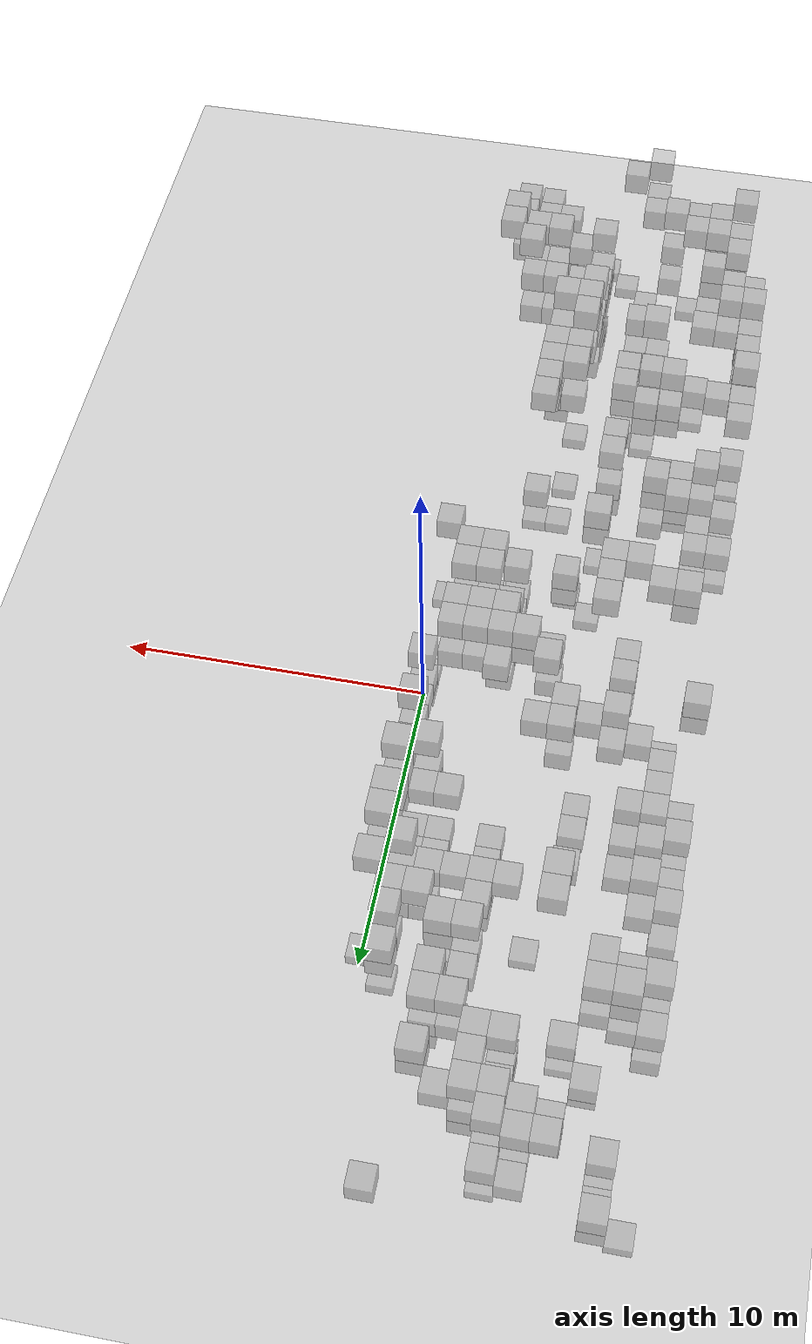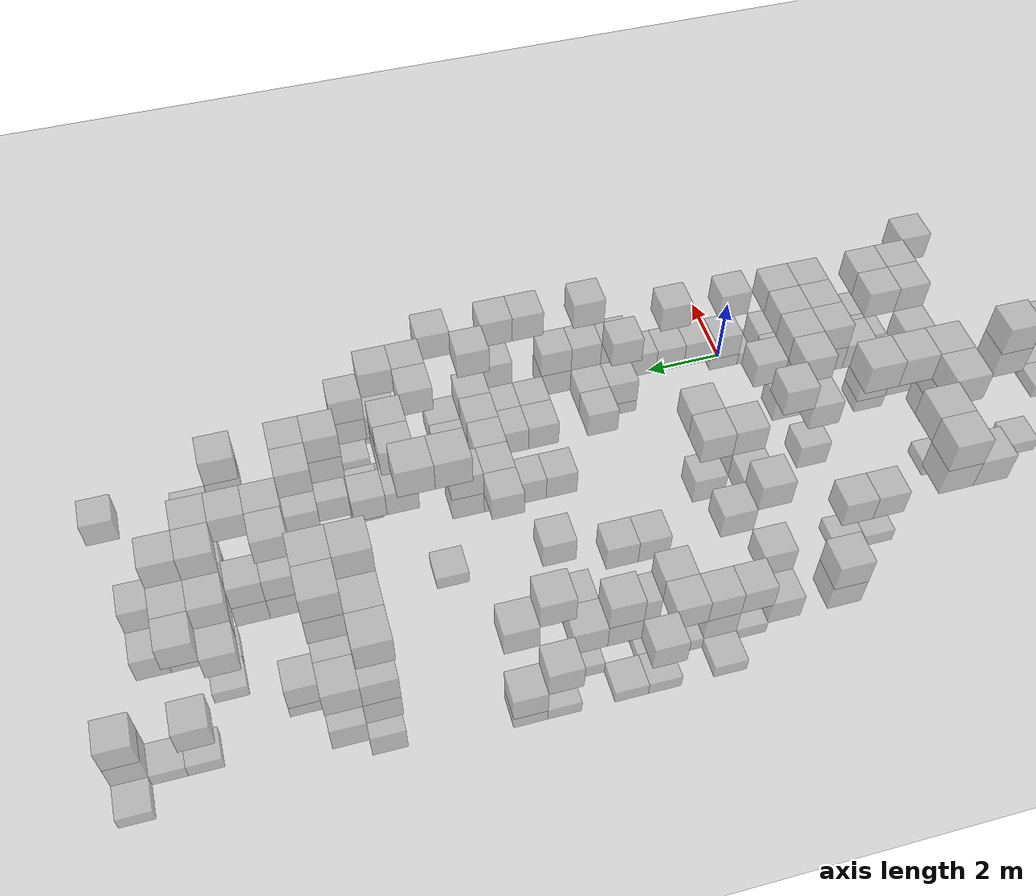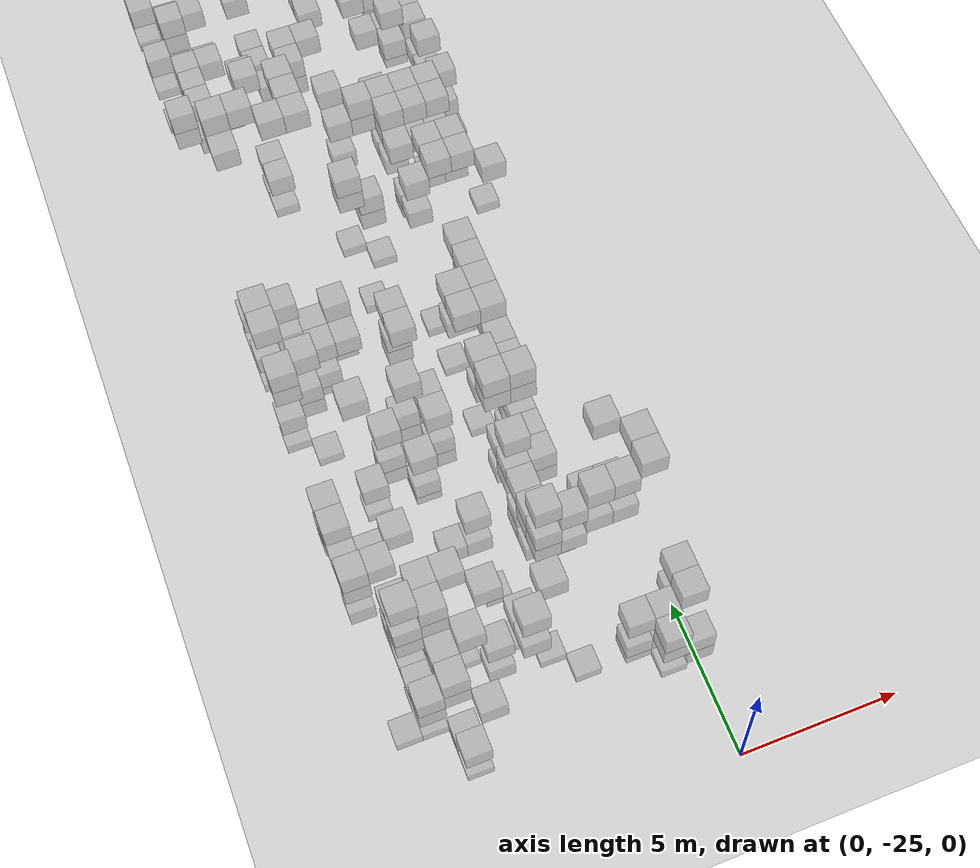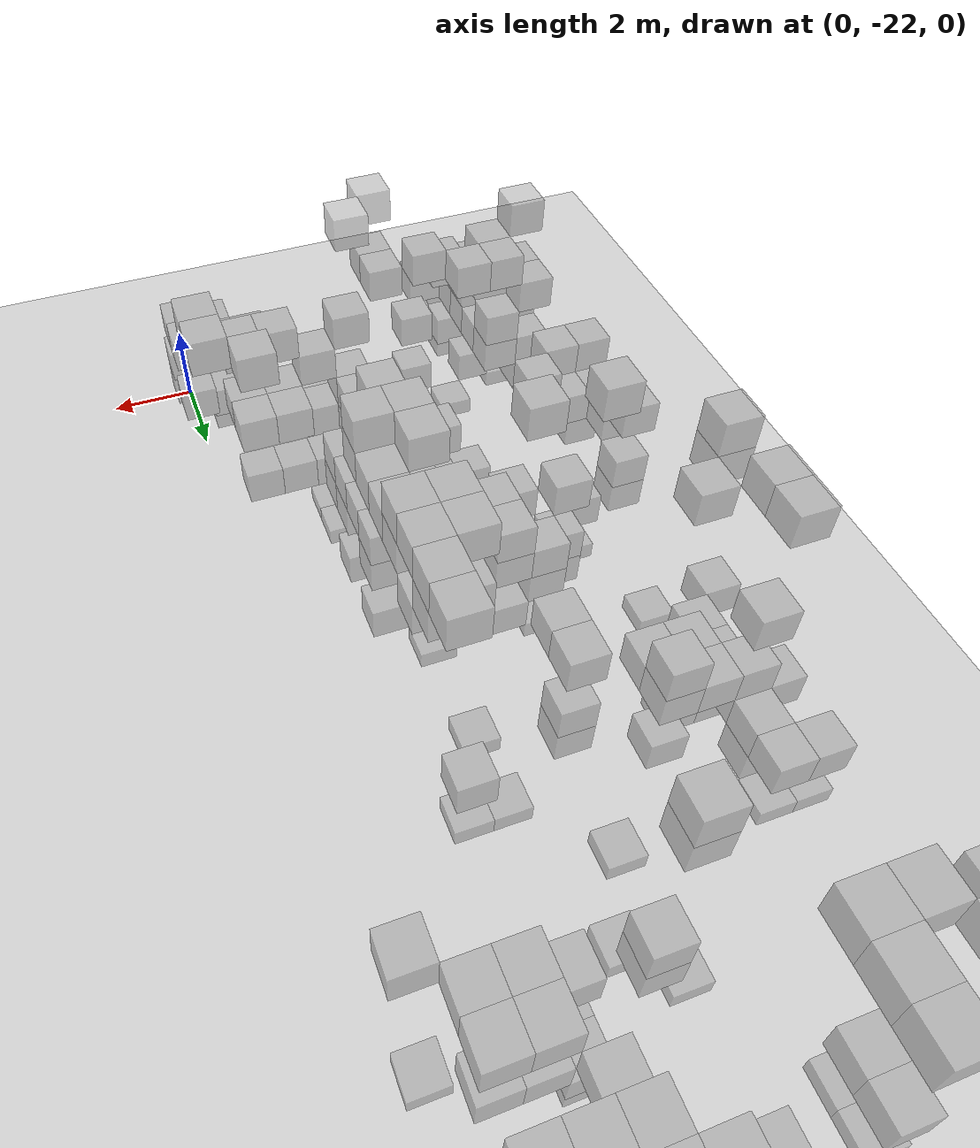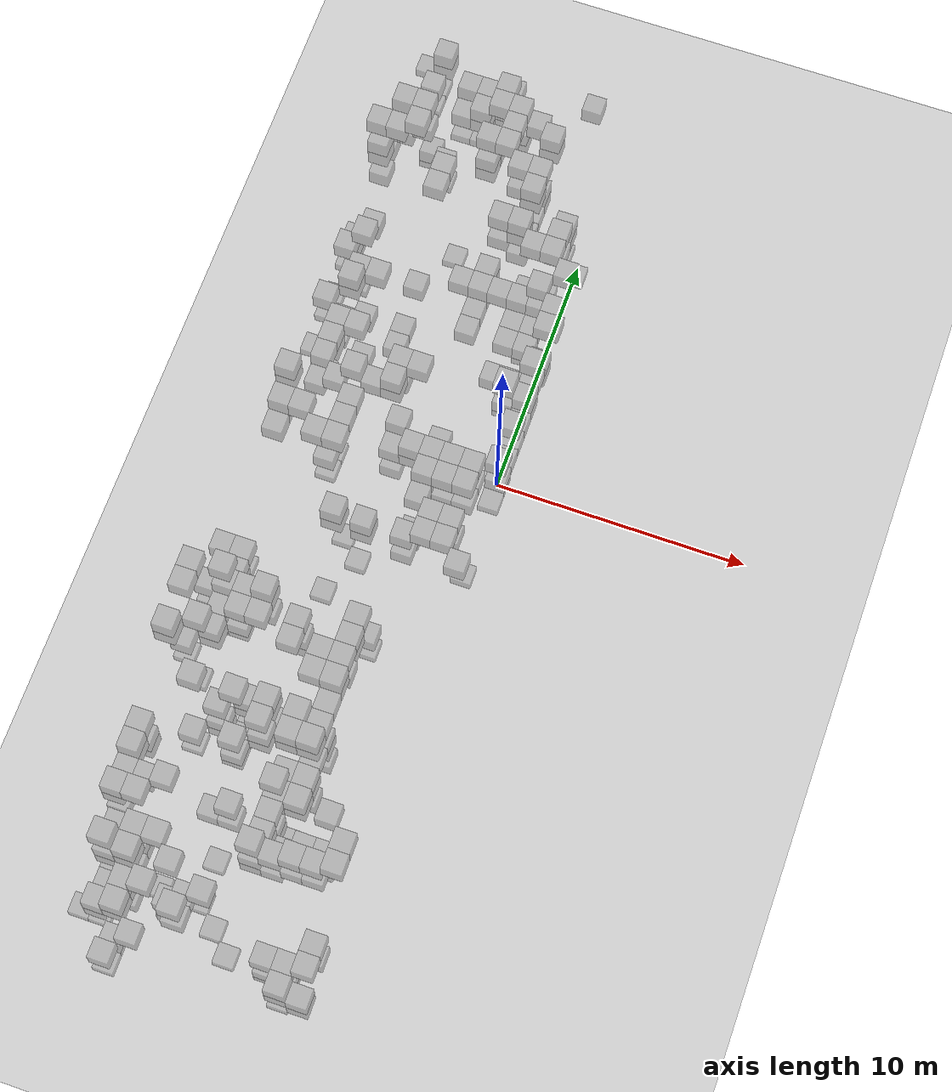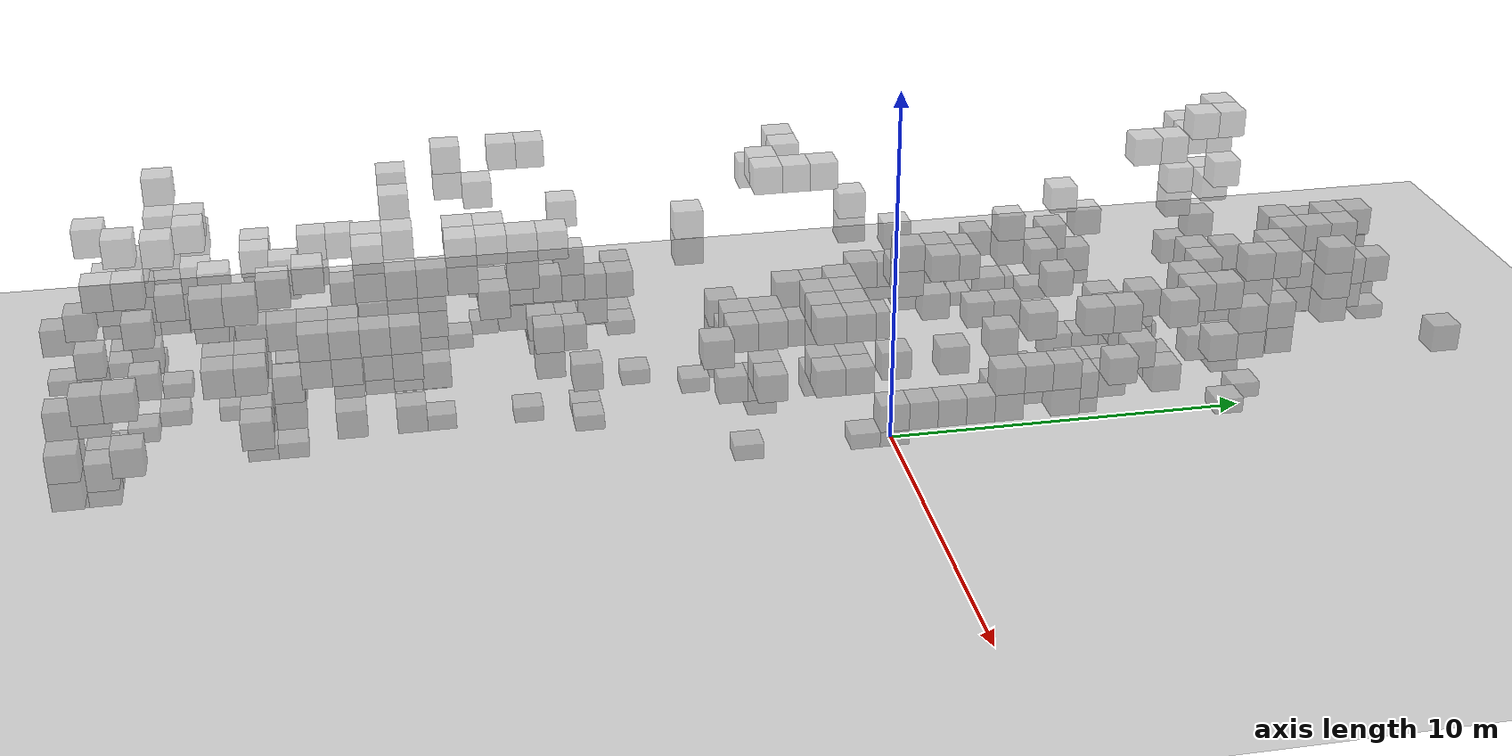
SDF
<?xml version="1.0" ?>
<sdf version="1.6">
  <world name="cramped_environment">
    <!-- ROS 2 State Plugin -->
    <plugin name="gazebo_ros_state" filename="libgazebo_ros_state.so">
      <ros>
        <namespace>/gazebo</namespace>
      </ros>
    </plugin>

    <!-- A global light source -->
    <include>
      <uri>model://sun</uri>
    </include>
    <!-- A ground plane -->
    <include>
      <uri>model://ground_plane</uri>
    </include>

    <!-- Obstacles representing the PCD Map -->
    <model name="obs_0">
      <static>true</static>
      <pose>-3.20 7.20 1.60 0 0 0</pose>
      <link name="link">
        <collision name="collision">
          <geometry>
            <box>
              <size>0.80 0.80 0.80</size>
            </box>
          </geometry>
        </collision>
        <visual name="visual">
          <transparency>0.5</transparency>
          <geometry>
            <box>
              <size>0.80 0.80 0.80</size>
            </box>
          </geometry>
          <material>
            <script>
              <name>Gazebo/Grey</name>
              <uri>file://media/materials/scripts/gazebo.material</uri>
            </script>
          </material>
        </visual>
      </link>
    </model>
    <model name="obs_1">
      <static>true</static>
      <pose>-8.00 -2.40 4.80 0 0 0</pose>
      <link name="link">
        <collision name="collision">
          <geometry>
            <box>
              <size>0.80 0.80 0.80</size>
            </box>
          </geometry>
        </collision>
        <visual name="visual">
          <transparency>0.5</transparency>
          <geometry>
            <box>
              <size>0.80 0.80 0.80</size>
            </box>
          </geometry>
          <material>
            <script>
              <name>Gazebo/Grey</name>
              <uri>file://media/materials/scripts/gazebo.material</uri>
            </script>
          </material>
        </visual>
      </link>
    </model>
    <model name="obs_2">
      <static>true</static>
      <pose>-8.80 -14.40 1.60 0 0 0</pose>
      <link name="link">
        <collision name="collision">
          <geometry>
            <box>
              <size>0.80 0.80 0.80</size>
            </box>
          </geometry>
        </collision>
        <visual name="visual">
          <transparency>0.5</transparency>
          <geometry>
            <box>
              <size>0.80 0.80 0.80</size>
            </box>
          </geometry>
          <material>
            <script>
              <name>Gazebo/Grey</name>
              <uri>file://media/materials/scripts/gazebo.material</uri>
            </script>
          </material>
        </visual>
      </link>
    </model>
    <model name="obs_3">
      <static>true</static>
      <pose>-2.40 -12.80 0.80 0 0 0</pose>
      <link name="link">
        <collision name="collision">
          <geometry>
            <box>
              <size>0.80 0.80 0.80</size>
            </box>
          </geometry>
        </collision>
        <visual name="visual">
          <transparency>0.5</transparency>
          <geometry>
            <box>
              <size>0.80 0.80 0.80</size>
            </box>
          </geometry>
          <material>
            <script>
              <name>Gazebo/Grey</name>
              <uri>file://media/materials/scripts/gazebo.material</uri>
            </script>
          </material>
        </visual>
      </link>
    </model>
    <model name="obs_4">
      <static>true</static>
      <pose>-4.00 14.40 1.60 0 0 0</pose>
      <link name="link">
        <collision name="collision">
          <geometry>
            <box>
              <size>0.80 0.80 0.80</size>
            </box>
          </geometry>
        </collision>
        <visual name="visual">
          <transparency>0.5</transparency>
          <geometry>
            <box>
              <size>0.80 0.80 0.80</size>
            </box>
          </geometry>
          <material>
            <script>
              <name>Gazebo/Grey</name>
              <uri>file://media/materials/scripts/gazebo.material</uri>
            </script>
          </material>
        </visual>
      </link>
    </model>
    <model name="obs_5">
      <static>true</static>
      <pose>-6.40 -1.60 0.00 0 0 0</pose>
      <link name="link">
        <collision name="collision">
          <geometry>
            <box>
              <size>0.80 0.80 0.80</size>
            </box>
          </geometry>
        </collision>
        <visual name="visual">
          <transparency>0.5</transparency>
          <geometry>
            <box>
              <size>0.80 0.80 0.80</size>
            </box>
          </geometry>
          <material>
            <script>
              <name>Gazebo/Grey</name>
              <uri>file://media/materials/scripts/gazebo.material</uri>
            </script>
          </material>
        </visual>
      </link>
    </model>
    <model name="obs_6">
      <static>true</static>
      <pose>-6.40 -0.80 0.00 0 0 0</pose>
      <link name="link">
        <collision name="collision">
          <geometry>
            <box>
              <size>0.80 0.80 0.80</size>
            </box>
          </geometry>
        </collision>
        <visual name="visual">
          <transparency>0.5</transparency>
          <geometry>
            <box>
              <size>0.80 0.80 0.80</size>
            </box>
          </geometry>
          <material>
            <script>
              <name>Gazebo/Grey</name>
              <uri>file://media/materials/scripts/gazebo.material</uri>
            </script>
          </material>
        </visual>
      </link>
    </model>
    <model name="obs_7">
      <static>true</static>
      <pose>-8.00 -1.60 5.60 0 0 0</pose>
      <link name="link">
        <collision name="collision">
          <geometry>
            <box>
              <size>0.80 0.80 0.80</size>
            </box>
          </geometry>
        </collision>
        <visual name="visual">
          <transparency>0.5</transparency>
          <geometry>
            <box>
              <size>0.80 0.80 0.80</size>
            </box>
          </geometry>
          <material>
            <script>
              <name>Gazebo/Grey</name>
              <uri>file://media/materials/scripts/gazebo.material</uri>
            </script>
          </material>
        </visual>
      </link>
    </model>
    <model name="obs_8">
      <static>true</static>
      <pose>-8.00 -8.00 2.40 0 0 0</pose>
      <link name="link">
        <collision name="collision">
          <geometry>
            <box>
              <size>0.80 0.80 0.80</size>
            </box>
          </geometry>
        </collision>
        <visual name="visual">
          <transparency>0.5</transparency>
          <geometry>
            <box>
              <size>0.80 0.80 0.80</size>
            </box>
          </geometry>
          <material>
            <script>
              <name>Gazebo/Grey</name>
              <uri>file://media/materials/scripts/gazebo.material</uri>
            </script>
          </material>
        </visual>
      </link>
    </model>
    <model name="obs_9">
      <static>true</static>
      <pose>-2.40 -9.60 5.60 0 0 0</pose>
      <link name="link">
        <collision name="collision">
          <geometry>
            <box>
              <size>0.80 0.80 0.80</size>
            </box>
          </geometry>
        </collision>
        <visual name="visual">
          <transparency>0.5</transparency>
          <geometry>
            <box>
              <size>0.80 0.80 0.80</size>
            </box>
          </geometry>
          <material>
            <script>
              <name>Gazebo/Grey</name>
              <uri>file://media/materials/scripts/gazebo.material</uri>
            </script>
          </material>
        </visual>
      </link>
    </model>
    <model name="obs_10">
      <static>true</static>
      <pose>-6.40 -8.00 0.80 0 0 0</pose>
      <link name="link">
        <collision name="collision">
          <geometry>
            <box>
              <size>0.80 0.80 0.80</size>
            </box>
          </geometry>
        </collision>
        <visual name="visual">
          <transparency>0.5</transparency>
          <geometry>
            <box>
              <size>0.80 0.80 0.80</size>
            </box>
          </geometry>
          <material>
            <script>
              <name>Gazebo/Grey</name>
              <uri>file://media/materials/scripts/gazebo.material</uri>
            </script>
          </material>
        </visual>
      </link>
    </model>
    <model name="obs_11">
      <static>true</static>
      <pose>-5.60 -2.40 5.60 0 0 0</pose>
      <link name="link">
        <collision name="collision">
          <geometry>
            <box>
              <size>0.80 0.80 0.80</size>
            </box>
          </geometry>
        </collision>
        <visual name="visual">
          <transparency>0.5</transparency>
          <geometry>
            <box>
              <size>0.80 0.80 0.80</size>
            </box>
          </geometry>
          <material>
            <script>
              <name>Gazebo/Grey</name>
              <uri>file://media/materials/scripts/gazebo.material</uri>
            </script>
          </material>
        </visual>
      </link>
    </model>
    <model name="obs_12">
      <static>true</static>
      <pose>-2.40 -15.20 3.20 0 0 0</pose>
      <link name="link">
        <collision name="collision">
          <geometry>
            <box>
              <size>0.80 0.80 0.80</size>
            </box>
          </geometry>
        </collision>
        <visual name="visual">
          <transparency>0.5</transparency>
          <geometry>
            <box>
              <size>0.80 0.80 0.80</size>
            </box>
          </geometry>
          <material>
            <script>
              <name>Gazebo/Grey</name>
              <uri>file://media/materials/scripts/gazebo.material</uri>
            </script>
          </material>
        </visual>
      </link>
    </model>
    <model name="obs_13">
      <static>true</static>
      <pose>-8.00 -20.80 0.00 0 0 0</pose>
      <link name="link">
        <collision name="collision">
          <geometry>
            <box>
              <size>0.80 0.80 0.80</size>
            </box>
          </geometry>
        </collision>
        <visual name="visual">
          <transparency>0.5</transparency>
          <geometry>
            <box>
              <size>0.80 0.80 0.80</size>
            </box>
          </geometry>
          <material>
            <script>
              <name>Gazebo/Grey</name>
              <uri>file://media/materials/scripts/gazebo.material</uri>
            </script>
          </material>
        </visual>
      </link>
    </model>
    <model name="obs_14">
      <static>true</static>
      <pose>-2.40 11.20 0.80 0 0 0</pose>
      <link name="link">
        <collision name="collision">
          <geometry>
            <box>
              <size>0.80 0.80 0.80</size>
            </box>
          </geometry>
        </collision>
        <visual name="visual">
          <transparency>0.5</transparency>
          <geometry>
            <box>
              <size>0.80 0.80 0.80</size>
            </box>
          </geometry>
          <material>
            <script>
              <name>Gazebo/Grey</name>
              <uri>file://media/materials/scripts/gazebo.material</uri>
            </script>
          </material>
        </visual>
      </link>
    </model>
    <model name="obs_15">
      <static>true</static>
      <pose>-4.80 -12.00 0.80 0 0 0</pose>
      <link name="link">
        <collision name="collision">
          <geometry>
            <box>
              <size>0.80 0.80 0.80</size>
            </box>
          </geometry>
        </collision>
        <visual name="visual">
          <transparency>0.5</transparency>
          <geometry>
            <box>
              <size>0.80 0.80 0.80</size>
            </box>
          </geometry>
          <material>
            <script>
              <name>Gazebo/Grey</name>
              <uri>file://media/materials/scripts/gazebo.material</uri>
            </script>
          </material>
        </visual>
      </link>
    </model>
    <model name="obs_16">
      <static>true</static>
      <pose>-4.00 -0.80 0.80 0 0 0</pose>
      <link name="link">
        <collision name="collision">
          <geometry>
            <box>
              <size>0.80 0.80 0.80</size>
            </box>
          </geometry>
        </collision>
        <visual name="visual">
          <transparency>0.5</transparency>
          <geometry>
            <box>
              <size>0.80 0.80 0.80</size>
            </box>
          </geometry>
          <material>
            <script>
              <name>Gazebo/Grey</name>
              <uri>file://media/materials/scripts/gazebo.material</uri>
            </script>
          </material>
        </visual>
      </link>
    </model>
    <model name="obs_17">
      <static>true</static>
      <pose>-4.80 -4.80 4.80 0 0 0</pose>
      <link name="link">
        <collision name="collision">
          <geometry>
            <box>
              <size>0.80 0.80 0.80</size>
            </box>
          </geometry>
        </collision>
        <visual name="visual">
          <transparency>0.5</transparency>
          <geometry>
            <box>
              <size>0.80 0.80 0.80</size>
            </box>
          </geometry>
          <material>
            <script>
              <name>Gazebo/Grey</name>
              <uri>file://media/materials/scripts/gazebo.material</uri>
            </script>
          </material>
        </visual>
      </link>
    </model>
    <model name="obs_18">
      <static>true</static>
      <pose>-2.40 12.00 1.60 0 0 0</pose>
      <link name="link">
        <collision name="collision">
          <geometry>
            <box>
              <size>0.80 0.80 0.80</size>
            </box>
          </geometry>
        </collision>
        <visual name="visual">
          <transparency>0.5</transparency>
          <geometry>
            <box>
              <size>0.80 0.80 0.80</size>
            </box>
          </geometry>
          <material>
            <script>
              <name>Gazebo/Grey</name>
              <uri>file://media/materials/scripts/gazebo.material</uri>
            </script>
          </material>
        </visual>
      </link>
    </model>
    <model name="obs_19">
      <static>true</static>
      <pose>-7.20 12.80 0.80 0 0 0</pose>
      <link name="link">
        <collision name="collision">
          <geometry>
            <box>
              <size>0.80 0.80 0.80</size>
            </box>
          </geometry>
        </collision>
        <visual name="visual">
          <transparency>0.5</transparency>
          <geometry>
            <box>
              <size>0.80 0.80 0.80</size>
            </box>
          </geometry>
          <material>
            <script>
              <name>Gazebo/Grey</name>
              <uri>file://media/materials/scripts/gazebo.material</uri>
            </script>
          </material>
        </visual>
      </link>
    </model>
    <model name="obs_20">
      <static>true</static>
      <pose>-7.20 -20.80 3.20 0 0 0</pose>
      <link name="link">
        <collision name="collision">
          <geometry>
            <box>
              <size>0.80 0.80 0.80</size>
            </box>
          </geometry>
        </collision>
        <visual name="visual">
          <transparency>0.5</transparency>
          <geometry>
            <box>
              <size>0.80 0.80 0.80</size>
            </box>
          </geometry>
          <material>
            <script>
              <name>Gazebo/Grey</name>
              <uri>file://media/materials/scripts/gazebo.material</uri>
            </script>
          </material>
        </visual>
      </link>
    </model>
    <model name="obs_21">
      <static>true</static>
      <pose>-7.20 12.00 4.00 0 0 0</pose>
      <link name="link">
        <collision name="collision">
          <geometry>
            <box>
              <size>0.80 0.80 0.80</size>
            </box>
          </geometry>
        </collision>
        <visual name="visual">
          <transparency>0.5</transparency>
          <geometry>
            <box>
              <size>0.80 0.80 0.80</size>
            </box>
          </geometry>
          <material>
            <script>
              <name>Gazebo/Grey</name>
              <uri>file://media/materials/scripts/gazebo.material</uri>
            </script>
          </material>
        </visual>
      </link>
    </model>
    <model name="obs_22">
      <static>true</static>
      <pose>-8.00 -20.00 0.00 0 0 0</pose>
      <link name="link">
        <collision name="collision">
          <geometry>
            <box>
              <size>0.80 0.80 0.80</size>
            </box>
          </geometry>
        </collision>
        <visual name="visual">
          <transparency>0.5</transparency>
          <geometry>
            <box>
              <size>0.80 0.80 0.80</size>
            </box>
          </geometry>
          <material>
            <script>
              <name>Gazebo/Grey</name>
              <uri>file://media/materials/scripts/gazebo.material</uri>
            </script>
          </material>
        </visual>
      </link>
    </model>
    <model name="obs_23">
      <static>true</static>
      <pose>-5.60 -13.60 0.80 0 0 0</pose>
      <link name="link">
        <collision name="collision">
          <geometry>
            <box>
              <size>0.80 0.80 0.80</size>
            </box>
          </geometry>
        </collision>
        <visual name="visual">
          <transparency>0.5</transparency>
          <geometry>
            <box>
              <size>0.80 0.80 0.80</size>
            </box>
          </geometry>
          <material>
            <script>
              <name>Gazebo/Grey</name>
              <uri>file://media/materials/scripts/gazebo.material</uri>
            </script>
          </material>
        </visual>
      </link>
    </model>
    <model name="obs_24">
      <static>true</static>
      <pose>-4.80 16.00 0.00 0 0 0</pose>
      <link name="link">
        <collision name="collision">
          <geometry>
            <box>
              <size>0.80 0.80 0.80</size>
            </box>
          </geometry>
        </collision>
        <visual name="visual">
          <transparency>0.5</transparency>
          <geometry>
            <box>
              <size>0.80 0.80 0.80</size>
            </box>
          </geometry>
          <material>
            <script>
              <name>Gazebo/Grey</name>
              <uri>file://media/materials/scripts/gazebo.material</uri>
            </script>
          </material>
        </visual>
      </link>
    </model>
    <model name="obs_25">
      <static>true</static>
      <pose>-7.20 6.40 1.60 0 0 0</pose>
      <link name="link">
        <collision name="collision">
          <geometry>
            <box>
              <size>0.80 0.80 0.80</size>
            </box>
          </geometry>
        </collision>
        <visual name="visual">
          <transparency>0.5</transparency>
          <geometry>
            <box>
              <size>0.80 0.80 0.80</size>
            </box>
          </geometry>
          <material>
            <script>
              <name>Gazebo/Grey</name>
              <uri>file://media/materials/scripts/gazebo.material</uri>
            </script>
          </material>
        </visual>
      </link>
    </model>
    <model name="obs_26">
      <static>true</static>
      <pose>0.00 -21.60 1.60 0 0 0</pose>
      <link name="link">
        <collision name="collision">
          <geometry>
            <box>
              <size>0.80 0.80 0.80</size>
            </box>
          </geometry>
        </collision>
        <visual name="visual">
          <transparency>0.5</transparency>
          <geometry>
            <box>
              <size>0.80 0.80 0.80</size>
            </box>
          </geometry>
          <material>
            <script>
              <name>Gazebo/Grey</name>
              <uri>file://media/materials/scripts/gazebo.material</uri>
            </script>
          </material>
        </visual>
      </link>
    </model>
    <model name="obs_27">
      <static>true</static>
      <pose>-1.60 -0.80 1.60 0 0 0</pose>
      <link name="link">
        <collision name="collision">
          <geometry>
            <box>
              <size>0.80 0.80 0.80</size>
            </box>
          </geometry>
        </collision>
        <visual name="visual">
          <transparency>0.5</transparency>
          <geometry>
            <box>
              <size>0.80 0.80 0.80</size>
            </box>
          </geometry>
          <material>
            <script>
              <name>Gazebo/Grey</name>
              <uri>file://media/materials/scripts/gazebo.material</uri>
            </script>
          </material>
        </visual>
      </link>
    </model>
    <model name="obs_28">
      <static>true</static>
      <pose>-0.80 -0.80 1.60 0 0 0</pose>
      <link name="link">
        <collision name="collision">
          <geometry>
            <box>
              <size>0.80 0.80 0.80</size>
            </box>
          </geometry>
        </collision>
        <visual name="visual">
          <transparency>0.5</transparency>
          <geometry>
            <box>
              <size>0.80 0.80 0.80</size>
            </box>
          </geometry>
          <material>
            <script>
              <name>Gazebo/Grey</name>
              <uri>file://media/materials/scripts/gazebo.material</uri>
            </script>
          </material>
        </visual>
      </link>
    </model>
    <model name="obs_29">
      <static>true</static>
      <pose>-1.60 -1.60 1.60 0 0 0</pose>
      <link name="link">
        <collision name="collision">
          <geometry>
            <box>
              <size>0.80 0.80 0.80</size>
            </box>
          </geometry>
        </collision>
        <visual name="visual">
          <transparency>0.5</transparency>
          <geometry>
            <box>
              <size>0.80 0.80 0.80</size>
            </box>
          </geometry>
          <material>
            <script>
              <name>Gazebo/Grey</name>
              <uri>file://media/materials/scripts/gazebo.material</uri>
            </script>
          </material>
        </visual>
      </link>
    </model>
    <model name="obs_30">
      <static>true</static>
      <pose>-0.80 -1.60 1.60 0 0 0</pose>
      <link name="link">
        <collision name="collision">
          <geometry>
            <box>
              <size>0.80 0.80 0.80</size>
            </box>
          </geometry>
        </collision>
        <visual name="visual">
          <transparency>0.5</transparency>
          <geometry>
            <box>
              <size>0.80 0.80 0.80</size>
            </box>
          </geometry>
          <material>
            <script>
              <name>Gazebo/Grey</name>
              <uri>file://media/materials/scripts/gazebo.material</uri>
            </script>
          </material>
        </visual>
      </link>
    </model>
    <model name="obs_31">
      <static>true</static>
      <pose>-4.80 12.80 1.60 0 0 0</pose>
      <link name="link">
        <collision name="collision">
          <geometry>
            <box>
              <size>0.80 0.80 0.80</size>
            </box>
          </geometry>
        </collision>
        <visual name="visual">
          <transparency>0.5</transparency>
          <geometry>
            <box>
              <size>0.80 0.80 0.80</size>
            </box>
          </geometry>
          <material>
            <script>
              <name>Gazebo/Grey</name>
              <uri>file://media/materials/scripts/gazebo.material</uri>
            </script>
          </material>
        </visual>
      </link>
    </model>
    <model name="obs_32">
      <static>true</static>
      <pose>-3.20 -14.40 1.60 0 0 0</pose>
      <link name="link">
        <collision name="collision">
          <geometry>
            <box>
              <size>0.80 0.80 0.80</size>
            </box>
          </geometry>
        </collision>
        <visual name="visual">
          <transparency>0.5</transparency>
          <geometry>
            <box>
              <size>0.80 0.80 0.80</size>
            </box>
          </geometry>
          <material>
            <script>
              <name>Gazebo/Grey</name>
              <uri>file://media/materials/scripts/gazebo.material</uri>
            </script>
          </material>
        </visual>
      </link>
    </model>
    <model name="obs_33">
      <static>true</static>
      <pose>-8.80 -6.40 0.00 0 0 0</pose>
      <link name="link">
        <collision name="collision">
          <geometry>
            <box>
              <size>0.80 0.80 0.80</size>
            </box>
          </geometry>
        </collision>
        <visual name="visual">
          <transparency>0.5</transparency>
          <geometry>
            <box>
              <size>0.80 0.80 0.80</size>
            </box>
          </geometry>
          <material>
            <script>
              <name>Gazebo/Grey</name>
              <uri>file://media/materials/scripts/gazebo.material</uri>
            </script>
          </material>
        </visual>
      </link>
    </model>
    <model name="obs_34">
      <static>true</static>
      <pose>-4.80 -20.80 4.00 0 0 0</pose>
      <link name="link">
        <collision name="collision">
          <geometry>
            <box>
              <size>0.80 0.80 0.80</size>
            </box>
          </geometry>
        </collision>
        <visual name="visual">
          <transparency>0.5</transparency>
          <geometry>
            <box>
              <size>0.80 0.80 0.80</size>
            </box>
          </geometry>
          <material>
            <script>
              <name>Gazebo/Grey</name>
              <uri>file://media/materials/scripts/gazebo.material</uri>
            </script>
          </material>
        </visual>
      </link>
    </model>
    <model name="obs_35">
      <static>true</static>
      <pose>-2.40 -4.00 0.80 0 0 0</pose>
      <link name="link">
        <collision name="collision">
          <geometry>
            <box>
              <size>0.80 0.80 0.80</size>
            </box>
          </geometry>
        </collision>
        <visual name="visual">
          <transparency>0.5</transparency>
          <geometry>
            <box>
              <size>0.80 0.80 0.80</size>
            </box>
          </geometry>
          <material>
            <script>
              <name>Gazebo/Grey</name>
              <uri>file://media/materials/scripts/gazebo.material</uri>
            </script>
          </material>
        </visual>
      </link>
    </model>
    <model name="obs_36">
      <static>true</static>
      <pose>0.00 1.60 0.80 0 0 0</pose>
      <link name="link">
        <collision name="collision">
          <geometry>
            <box>
              <size>0.80 0.80 0.80</size>
            </box>
          </geometry>
        </collision>
        <visual name="visual">
          <transparency>0.5</transparency>
          <geometry>
            <box>
              <size>0.80 0.80 0.80</size>
            </box>
          </geometry>
          <material>
            <script>
              <name>Gazebo/Grey</name>
              <uri>file://media/materials/scripts/gazebo.material</uri>
            </script>
          </material>
        </visual>
      </link>
    </model>
    <model name="obs_37">
      <static>true</static>
      <pose>-5.60 -20.00 0.80 0 0 0</pose>
      <link name="link">
        <collision name="collision">
          <geometry>
            <box>
              <size>0.80 0.80 0.80</size>
            </box>
          </geometry>
        </collision>
        <visual name="visual">
          <transparency>0.5</transparency>
          <geometry>
            <box>
              <size>0.80 0.80 0.80</size>
            </box>
          </geometry>
          <material>
            <script>
              <name>Gazebo/Grey</name>
              <uri>file://media/materials/scripts/gazebo.material</uri>
            </script>
          </material>
        </visual>
      </link>
    </model>
    <model name="obs_38">
      <static>true</static>
      <pose>-8.00 4.00 0.00 0 0 0</pose>
      <link name="link">
        <collision name="collision">
          <geometry>
            <box>
              <size>0.80 0.80 0.80</size>
            </box>
          </geometry>
        </collision>
        <visual name="visual">
          <transparency>0.5</transparency>
          <geometry>
            <box>
              <size>0.80 0.80 0.80</size>
            </box>
          </geometry>
          <material>
            <script>
              <name>Gazebo/Grey</name>
              <uri>file://media/materials/scripts/gazebo.material</uri>
            </script>
          </material>
        </visual>
      </link>
    </model>
    <model name="obs_39">
      <static>true</static>
      <pose>-3.20 -17.60 3.20 0 0 0</pose>
      <link name="link">
        <collision name="collision">
          <geometry>
            <box>
              <size>0.80 0.80 0.80</size>
            </box>
          </geometry>
        </collision>
        <visual name="visual">
          <transparency>0.5</transparency>
          <geometry>
            <box>
              <size>0.80 0.80 0.80</size>
            </box>
          </geometry>
          <material>
            <script>
              <name>Gazebo/Grey</name>
              <uri>file://media/materials/scripts/gazebo.material</uri>
            </script>
          </material>
        </visual>
      </link>
    </model>
    <model name="obs_40">
      <static>true</static>
      <pose>-2.40 -3.20 0.80 0 0 0</pose>
      <link name="link">
        <collision name="collision">
          <geometry>
            <box>
              <size>0.80 0.80 0.80</size>
            </box>
          </geometry>
        </collision>
        <visual name="visual">
          <transparency>0.5</transparency>
          <geometry>
            <box>
              <size>0.80 0.80 0.80</size>
            </box>
          </geometry>
          <material>
            <script>
              <name>Gazebo/Grey</name>
              <uri>file://media/materials/scripts/gazebo.material</uri>
            </script>
          </material>
        </visual>
      </link>
    </model>
    <model name="obs_41">
      <static>true</static>
      <pose>-4.00 12.80 3.20 0 0 0</pose>
      <link name="link">
        <collision name="collision">
          <geometry>
            <box>
              <size>0.80 0.80 0.80</size>
            </box>
          </geometry>
        </collision>
        <visual name="visual">
          <transparency>0.5</transparency>
          <geometry>
            <box>
              <size>0.80 0.80 0.80</size>
            </box>
          </geometry>
          <material>
            <script>
              <name>Gazebo/Grey</name>
              <uri>file://media/materials/scripts/gazebo.material</uri>
            </script>
          </material>
        </visual>
      </link>
    </model>
    <model name="obs_42">
      <static>true</static>
      <pose>-3.20 9.60 1.60 0 0 0</pose>
      <link name="link">
        <collision name="collision">
          <geometry>
            <box>
              <size>0.80 0.80 0.80</size>
            </box>
          </geometry>
        </collision>
        <visual name="visual">
          <transparency>0.5</transparency>
          <geometry>
            <box>
              <size>0.80 0.80 0.80</size>
            </box>
          </geometry>
          <material>
            <script>
              <name>Gazebo/Grey</name>
              <uri>file://media/materials/scripts/gazebo.material</uri>
            </script>
          </material>
        </visual>
      </link>
    </model>
    <model name="obs_43">
      <static>true</static>
      <pose>-8.80 -9.60 5.60 0 0 0</pose>
      <link name="link">
        <collision name="collision">
          <geometry>
            <box>
              <size>0.80 0.80 0.80</size>
            </box>
          </geometry>
        </collision>
        <visual name="visual">
          <transparency>0.5</transparency>
          <geometry>
            <box>
              <size>0.80 0.80 0.80</size>
            </box>
          </geometry>
          <material>
            <script>
              <name>Gazebo/Grey</name>
              <uri>file://media/materials/scripts/gazebo.material</uri>
            </script>
          </material>
        </visual>
      </link>
    </model>
    <model name="obs_44">
      <static>true</static>
      <pose>-8.80 -16.00 2.40 0 0 0</pose>
      <link name="link">
        <collision name="collision">
          <geometry>
            <box>
              <size>0.80 0.80 0.80</size>
            </box>
          </geometry>
        </collision>
        <visual name="visual">
          <transparency>0.5</transparency>
          <geometry>
            <box>
              <size>0.80 0.80 0.80</size>
            </box>
          </geometry>
          <material>
            <script>
              <name>Gazebo/Grey</name>
              <uri>file://media/materials/scripts/gazebo.material</uri>
            </script>
          </material>
        </visual>
      </link>
    </model>
    <model name="obs_45">
      <static>true</static>
      <pose>-5.60 4.00 0.80 0 0 0</pose>
      <link name="link">
        <collision name="collision">
          <geometry>
            <box>
              <size>0.80 0.80 0.80</size>
            </box>
          </geometry>
        </collision>
        <visual name="visual">
          <transparency>0.5</transparency>
          <geometry>
            <box>
              <size>0.80 0.80 0.80</size>
            </box>
          </geometry>
          <material>
            <script>
              <name>Gazebo/Grey</name>
              <uri>file://media/materials/scripts/gazebo.material</uri>
            </script>
          </material>
        </visual>
      </link>
    </model>
    <model name="obs_46">
      <static>true</static>
      <pose>-2.40 -13.60 3.20 0 0 0</pose>
      <link name="link">
        <collision name="collision">
          <geometry>
            <box>
              <size>0.80 0.80 0.80</size>
            </box>
          </geometry>
        </collision>
        <visual name="visual">
          <transparency>0.5</transparency>
          <geometry>
            <box>
              <size>0.80 0.80 0.80</size>
            </box>
          </geometry>
          <material>
            <script>
              <name>Gazebo/Grey</name>
              <uri>file://media/materials/scripts/gazebo.material</uri>
            </script>
          </material>
        </visual>
      </link>
    </model>
    <model name="obs_47">
      <static>true</static>
      <pose>-1.60 -16.80 1.60 0 0 0</pose>
      <link name="link">
        <collision name="collision">
          <geometry>
            <box>
              <size>0.80 0.80 0.80</size>
            </box>
          </geometry>
        </collision>
        <visual name="visual">
          <transparency>0.5</transparency>
          <geometry>
            <box>
              <size>0.80 0.80 0.80</size>
            </box>
          </geometry>
          <material>
            <script>
              <name>Gazebo/Grey</name>
              <uri>file://media/materials/scripts/gazebo.material</uri>
            </script>
          </material>
        </visual>
      </link>
    </model>
    <model name="obs_48">
      <static>true</static>
      <pose>-0.80 -16.80 1.60 0 0 0</pose>
      <link name="link">
        <collision name="collision">
          <geometry>
            <box>
              <size>0.80 0.80 0.80</size>
            </box>
          </geometry>
        </collision>
        <visual name="visual">
          <transparency>0.5</transparency>
          <geometry>
            <box>
              <size>0.80 0.80 0.80</size>
            </box>
          </geometry>
          <material>
            <script>
              <name>Gazebo/Grey</name>
              <uri>file://media/materials/scripts/gazebo.material</uri>
            </script>
          </material>
        </visual>
      </link>
    </model>
    <model name="obs_49">
      <static>true</static>
      <pose>-7.20 -8.80 0.80 0 0 0</pose>
      <link name="link">
        <collision name="collision">
          <geometry>
            <box>
              <size>0.80 0.80 0.80</size>
            </box>
          </geometry>
        </collision>
        <visual name="visual">
          <transparency>0.5</transparency>
          <geometry>
            <box>
              <size>0.80 0.80 0.80</size>
            </box>
          </geometry>
          <material>
            <script>
              <name>Gazebo/Grey</name>
              <uri>file://media/materials/scripts/gazebo.material</uri>
            </script>
          </material>
        </visual>
      </link>
    </model>
    <model name="obs_50">
      <static>true</static>
      <pose>-8.80 -15.20 3.20 0 0 0</pose>
      <link name="link">
        <collision name="collision">
          <geometry>
            <box>
              <size>0.80 0.80 0.80</size>
            </box>
          </geometry>
        </collision>
        <visual name="visual">
          <transparency>0.5</transparency>
          <geometry>
            <box>
              <size>0.80 0.80 0.80</size>
            </box>
          </geometry>
          <material>
            <script>
              <name>Gazebo/Grey</name>
              <uri>file://media/materials/scripts/gazebo.material</uri>
            </script>
          </material>
        </visual>
      </link>
    </model>
    <model name="obs_51">
      <static>true</static>
      <pose>-8.80 11.20 0.80 0 0 0</pose>
      <link name="link">
        <collision name="collision">
          <geometry>
            <box>
              <size>0.80 0.80 0.80</size>
            </box>
          </geometry>
        </collision>
        <visual name="visual">
          <transparency>0.5</transparency>
          <geometry>
            <box>
              <size>0.80 0.80 0.80</size>
            </box>
          </geometry>
          <material>
            <script>
              <name>Gazebo/Grey</name>
              <uri>file://media/materials/scripts/gazebo.material</uri>
            </script>
          </material>
        </visual>
      </link>
    </model>
    <model name="obs_52">
      <static>true</static>
      <pose>-0.80 10.40 0.00 0 0 0</pose>
      <link name="link">
        <collision name="collision">
          <geometry>
            <box>
              <size>0.80 0.80 0.80</size>
            </box>
          </geometry>
        </collision>
        <visual name="visual">
          <transparency>0.5</transparency>
          <geometry>
            <box>
              <size>0.80 0.80 0.80</size>
            </box>
          </geometry>
          <material>
            <script>
              <name>Gazebo/Grey</name>
              <uri>file://media/materials/scripts/gazebo.material</uri>
            </script>
          </material>
        </visual>
      </link>
    </model>
    <model name="obs_53">
      <static>true</static>
      <pose>-8.00 -11.20 0.00 0 0 0</pose>
      <link name="link">
        <collision name="collision">
          <geometry>
            <box>
              <size>0.80 0.80 0.80</size>
            </box>
          </geometry>
        </collision>
        <visual name="visual">
          <transparency>0.5</transparency>
          <geometry>
            <box>
              <size>0.80 0.80 0.80</size>
            </box>
          </geometry>
          <material>
            <script>
              <name>Gazebo/Grey</name>
              <uri>file://media/materials/scripts/gazebo.material</uri>
            </script>
          </material>
        </visual>
      </link>
    </model>
    <model name="obs_54">
      <static>true</static>
      <pose>-8.80 12.00 1.60 0 0 0</pose>
      <link name="link">
        <collision name="collision">
          <geometry>
            <box>
              <size>0.80 0.80 0.80</size>
            </box>
          </geometry>
        </collision>
        <visual name="visual">
          <transparency>0.5</transparency>
          <geometry>
            <box>
              <size>0.80 0.80 0.80</size>
            </box>
          </geometry>
          <material>
            <script>
              <name>Gazebo/Grey</name>
              <uri>file://media/materials/scripts/gazebo.material</uri>
            </script>
          </material>
        </visual>
      </link>
    </model>
    <model name="obs_55">
      <static>true</static>
      <pose>-2.40 -12.80 3.20 0 0 0</pose>
      <link name="link">
        <collision name="collision">
          <geometry>
            <box>
              <size>0.80 0.80 0.80</size>
            </box>
          </geometry>
        </collision>
        <visual name="visual">
          <transparency>0.5</transparency>
          <geometry>
            <box>
              <size>0.80 0.80 0.80</size>
            </box>
          </geometry>
          <material>
            <script>
              <name>Gazebo/Grey</name>
              <uri>file://media/materials/scripts/gazebo.material</uri>
            </script>
          </material>
        </visual>
      </link>
    </model>
    <model name="obs_56">
      <static>true</static>
      <pose>-7.20 -12.80 5.60 0 0 0</pose>
      <link name="link">
        <collision name="collision">
          <geometry>
            <box>
              <size>0.80 0.80 0.80</size>
            </box>
          </geometry>
        </collision>
        <visual name="visual">
          <transparency>0.5</transparency>
          <geometry>
            <box>
              <size>0.80 0.80 0.80</size>
            </box>
          </geometry>
          <material>
            <script>
              <name>Gazebo/Grey</name>
              <uri>file://media/materials/scripts/gazebo.material</uri>
            </script>
          </material>
        </visual>
      </link>
    </model>
    <model name="obs_57">
      <static>true</static>
      <pose>-7.20 -19.20 2.40 0 0 0</pose>
      <link name="link">
        <collision name="collision">
          <geometry>
            <box>
              <size>0.80 0.80 0.80</size>
            </box>
          </geometry>
        </collision>
        <visual name="visual">
          <transparency>0.5</transparency>
          <geometry>
            <box>
              <size>0.80 0.80 0.80</size>
            </box>
          </geometry>
          <material>
            <script>
              <name>Gazebo/Grey</name>
              <uri>file://media/materials/scripts/gazebo.material</uri>
            </script>
          </material>
        </visual>
      </link>
    </model>
    <model name="obs_58">
      <static>true</static>
      <pose>-0.80 7.20 1.60 0 0 0</pose>
      <link name="link">
        <collision name="collision">
          <geometry>
            <box>
              <size>0.80 0.80 0.80</size>
            </box>
          </geometry>
        </collision>
        <visual name="visual">
          <transparency>0.5</transparency>
          <geometry>
            <box>
              <size>0.80 0.80 0.80</size>
            </box>
          </geometry>
          <material>
            <script>
              <name>Gazebo/Grey</name>
              <uri>file://media/materials/scripts/gazebo.material</uri>
            </script>
          </material>
        </visual>
      </link>
    </model>
    <model name="obs_59">
      <static>true</static>
      <pose>-1.60 7.20 1.60 0 0 0</pose>
      <link name="link">
        <collision name="collision">
          <geometry>
            <box>
              <size>0.80 0.80 0.80</size>
            </box>
          </geometry>
        </collision>
        <visual name="visual">
          <transparency>0.5</transparency>
          <geometry>
            <box>
              <size>0.80 0.80 0.80</size>
            </box>
          </geometry>
          <material>
            <script>
              <name>Gazebo/Grey</name>
              <uri>file://media/materials/scripts/gazebo.material</uri>
            </script>
          </material>
        </visual>
      </link>
    </model>
    <model name="obs_60">
      <static>true</static>
      <pose>0.00 -20.00 1.60 0 0 0</pose>
      <link name="link">
        <collision name="collision">
          <geometry>
            <box>
              <size>0.80 0.80 0.80</size>
            </box>
          </geometry>
        </collision>
        <visual name="visual">
          <transparency>0.5</transparency>
          <geometry>
            <box>
              <size>0.80 0.80 0.80</size>
            </box>
          </geometry>
          <material>
            <script>
              <name>Gazebo/Grey</name>
              <uri>file://media/materials/scripts/gazebo.material</uri>
            </script>
          </material>
        </visual>
      </link>
    </model>
    <model name="obs_61">
      <static>true</static>
      <pose>-6.40 -2.40 5.60 0 0 0</pose>
      <link name="link">
        <collision name="collision">
          <geometry>
            <box>
              <size>0.80 0.80 0.80</size>
            </box>
          </geometry>
        </collision>
        <visual name="visual">
          <transparency>0.5</transparency>
          <geometry>
            <box>
              <size>0.80 0.80 0.80</size>
            </box>
          </geometry>
          <material>
            <script>
              <name>Gazebo/Grey</name>
              <uri>file://media/materials/scripts/gazebo.material</uri>
            </script>
          </material>
        </visual>
      </link>
    </model>
    <model name="obs_62">
      <static>true</static>
      <pose>-4.80 -8.80 1.60 0 0 0</pose>
      <link name="link">
        <collision name="collision">
          <geometry>
            <box>
              <size>0.80 0.80 0.80</size>
            </box>
          </geometry>
        </collision>
        <visual name="visual">
          <transparency>0.5</transparency>
          <geometry>
            <box>
              <size>0.80 0.80 0.80</size>
            </box>
          </geometry>
          <material>
            <script>
              <name>Gazebo/Grey</name>
              <uri>file://media/materials/scripts/gazebo.material</uri>
            </script>
          </material>
        </visual>
      </link>
    </model>
    <model name="obs_63">
      <static>true</static>
      <pose>-5.60 -12.00 0.00 0 0 0</pose>
      <link name="link">
        <collision name="collision">
          <geometry>
            <box>
              <size>0.80 0.80 0.80</size>
            </box>
          </geometry>
        </collision>
        <visual name="visual">
          <transparency>0.5</transparency>
          <geometry>
            <box>
              <size>0.80 0.80 0.80</size>
            </box>
          </geometry>
          <material>
            <script>
              <name>Gazebo/Grey</name>
              <uri>file://media/materials/scripts/gazebo.material</uri>
            </script>
          </material>
        </visual>
      </link>
    </model>
    <model name="obs_64">
      <static>true</static>
      <pose>-6.40 -8.80 2.40 0 0 0</pose>
      <link name="link">
        <collision name="collision">
          <geometry>
            <box>
              <size>0.80 0.80 0.80</size>
            </box>
          </geometry>
        </collision>
        <visual name="visual">
          <transparency>0.5</transparency>
          <geometry>
            <box>
              <size>0.80 0.80 0.80</size>
            </box>
          </geometry>
          <material>
            <script>
              <name>Gazebo/Grey</name>
              <uri>file://media/materials/scripts/gazebo.material</uri>
            </script>
          </material>
        </visual>
      </link>
    </model>
    <model name="obs_65">
      <static>true</static>
      <pose>0.00 -17.60 5.60 0 0 0</pose>
      <link name="link">
        <collision name="collision">
          <geometry>
            <box>
              <size>0.80 0.80 0.80</size>
            </box>
          </geometry>
        </collision>
        <visual name="visual">
          <transparency>0.5</transparency>
          <geometry>
            <box>
              <size>0.80 0.80 0.80</size>
            </box>
          </geometry>
          <material>
            <script>
              <name>Gazebo/Grey</name>
              <uri>file://media/materials/scripts/gazebo.material</uri>
            </script>
          </material>
        </visual>
      </link>
    </model>
    <model name="obs_66">
      <static>true</static>
      <pose>-7.20 -18.40 3.20 0 0 0</pose>
      <link name="link">
        <collision name="collision">
          <geometry>
            <box>
              <size>0.80 0.80 0.80</size>
            </box>
          </geometry>
        </collision>
        <visual name="visual">
          <transparency>0.5</transparency>
          <geometry>
            <box>
              <size>0.80 0.80 0.80</size>
            </box>
          </geometry>
          <material>
            <script>
              <name>Gazebo/Grey</name>
              <uri>file://media/materials/scripts/gazebo.material</uri>
            </script>
          </material>
        </visual>
      </link>
    </model>
    <model name="obs_67">
      <static>true</static>
      <pose>-6.40 -8.00 3.20 0 0 0</pose>
      <link name="link">
        <collision name="collision">
          <geometry>
            <box>
              <size>0.80 0.80 0.80</size>
            </box>
          </geometry>
        </collision>
        <visual name="visual">
          <transparency>0.5</transparency>
          <geometry>
            <box>
              <size>0.80 0.80 0.80</size>
            </box>
          </geometry>
          <material>
            <script>
              <name>Gazebo/Grey</name>
              <uri>file://media/materials/scripts/gazebo.material</uri>
            </script>
          </material>
        </visual>
      </link>
    </model>
    <model name="obs_68">
      <static>true</static>
      <pose>-8.00 -20.80 2.40 0 0 0</pose>
      <link name="link">
        <collision name="collision">
          <geometry>
            <box>
              <size>0.80 0.80 0.80</size>
            </box>
          </geometry>
        </collision>
        <visual name="visual">
          <transparency>0.5</transparency>
          <geometry>
            <box>
              <size>0.80 0.80 0.80</size>
            </box>
          </geometry>
          <material>
            <script>
              <name>Gazebo/Grey</name>
              <uri>file://media/materials/scripts/gazebo.material</uri>
            </script>
          </material>
        </visual>
      </link>
    </model>
    <model name="obs_69">
      <static>true</static>
      <pose>-2.40 11.20 3.20 0 0 0</pose>
      <link name="link">
        <collision name="collision">
          <geometry>
            <box>
              <size>0.80 0.80 0.80</size>
            </box>
          </geometry>
        </collision>
        <visual name="visual">
          <transparency>0.5</transparency>
          <geometry>
            <box>
              <size>0.80 0.80 0.80</size>
            </box>
          </geometry>
          <material>
            <script>
              <name>Gazebo/Grey</name>
              <uri>file://media/materials/scripts/gazebo.material</uri>
            </script>
          </material>
        </visual>
      </link>
    </model>
    <model name="obs_70">
      <static>true</static>
      <pose>-8.00 12.00 3.20 0 0 0</pose>
      <link name="link">
        <collision name="collision">
          <geometry>
            <box>
              <size>0.80 0.80 0.80</size>
            </box>
          </geometry>
        </collision>
        <visual name="visual">
          <transparency>0.5</transparency>
          <geometry>
            <box>
              <size>0.80 0.80 0.80</size>
            </box>
          </geometry>
          <material>
            <script>
              <name>Gazebo/Grey</name>
              <uri>file://media/materials/scripts/gazebo.material</uri>
            </script>
          </material>
        </visual>
      </link>
    </model>
    <model name="obs_71">
      <static>true</static>
      <pose>-4.80 -12.00 3.20 0 0 0</pose>
      <link name="link">
        <collision name="collision">
          <geometry>
            <box>
              <size>0.80 0.80 0.80</size>
            </box>
          </geometry>
        </collision>
        <visual name="visual">
          <transparency>0.5</transparency>
          <geometry>
            <box>
              <size>0.80 0.80 0.80</size>
            </box>
          </geometry>
          <material>
            <script>
              <name>Gazebo/Grey</name>
              <uri>file://media/materials/scripts/gazebo.material</uri>
            </script>
          </material>
        </visual>
      </link>
    </model>
    <model name="obs_72">
      <static>true</static>
      <pose>-7.20 11.20 5.60 0 0 0</pose>
      <link name="link">
        <collision name="collision">
          <geometry>
            <box>
              <size>0.80 0.80 0.80</size>
            </box>
          </geometry>
        </collision>
        <visual name="visual">
          <transparency>0.5</transparency>
          <geometry>
            <box>
              <size>0.80 0.80 0.80</size>
            </box>
          </geometry>
          <material>
            <script>
              <name>Gazebo/Grey</name>
              <uri>file://media/materials/scripts/gazebo.material</uri>
            </script>
          </material>
        </visual>
      </link>
    </model>
    <model name="obs_73">
      <static>true</static>
      <pose>0.00 4.00 1.60 0 0 0</pose>
      <link name="link">
        <collision name="collision">
          <geometry>
            <box>
              <size>0.80 0.80 0.80</size>
            </box>
          </geometry>
        </collision>
        <visual name="visual">
          <transparency>0.5</transparency>
          <geometry>
            <box>
              <size>0.80 0.80 0.80</size>
            </box>
          </geometry>
          <material>
            <script>
              <name>Gazebo/Grey</name>
              <uri>file://media/materials/scripts/gazebo.material</uri>
            </script>
          </material>
        </visual>
      </link>
    </model>
    <model name="obs_74">
      <static>true</static>
      <pose>-4.80 15.20 1.60 0 0 0</pose>
      <link name="link">
        <collision name="collision">
          <geometry>
            <box>
              <size>0.80 0.80 0.80</size>
            </box>
          </geometry>
        </collision>
        <visual name="visual">
          <transparency>0.5</transparency>
          <geometry>
            <box>
              <size>0.80 0.80 0.80</size>
            </box>
          </geometry>
          <material>
            <script>
              <name>Gazebo/Grey</name>
              <uri>file://media/materials/scripts/gazebo.material</uri>
            </script>
          </material>
        </visual>
      </link>
    </model>
    <model name="obs_75">
      <static>true</static>
      <pose>-6.40 15.20 2.40 0 0 0</pose>
      <link name="link">
        <collision name="collision">
          <geometry>
            <box>
              <size>0.80 0.80 0.80</size>
            </box>
          </geometry>
        </collision>
        <visual name="visual">
          <transparency>0.5</transparency>
          <geometry>
            <box>
              <size>0.80 0.80 0.80</size>
            </box>
          </geometry>
          <material>
            <script>
              <name>Gazebo/Grey</name>
              <uri>file://media/materials/scripts/gazebo.material</uri>
            </script>
          </material>
        </visual>
      </link>
    </model>
    <model name="obs_76">
      <static>true</static>
      <pose>-6.40 -18.40 4.80 0 0 0</pose>
      <link name="link">
        <collision name="collision">
          <geometry>
            <box>
              <size>0.80 0.80 0.80</size>
            </box>
          </geometry>
        </collision>
        <visual name="visual">
          <transparency>0.5</transparency>
          <geometry>
            <box>
              <size>0.80 0.80 0.80</size>
            </box>
          </geometry>
          <material>
            <script>
              <name>Gazebo/Grey</name>
              <uri>file://media/materials/scripts/gazebo.material</uri>
            </script>
          </material>
        </visual>
      </link>
    </model>
    <model name="obs_77">
      <static>true</static>
      <pose>-2.40 -0.80 0.80 0 0 0</pose>
      <link name="link">
        <collision name="collision">
          <geometry>
            <box>
              <size>0.80 0.80 0.80</size>
            </box>
          </geometry>
        </collision>
        <visual name="visual">
          <transparency>0.5</transparency>
          <geometry>
            <box>
              <size>0.80 0.80 0.80</size>
            </box>
          </geometry>
          <material>
            <script>
              <name>Gazebo/Grey</name>
              <uri>file://media/materials/scripts/gazebo.material</uri>
            </script>
          </material>
        </visual>
      </link>
    </model>
    <model name="obs_78">
      <static>true</static>
      <pose>-2.40 -1.60 0.80 0 0 0</pose>
      <link name="link">
        <collision name="collision">
          <geometry>
            <box>
              <size>0.80 0.80 0.80</size>
            </box>
          </geometry>
        </collision>
        <visual name="visual">
          <transparency>0.5</transparency>
          <geometry>
            <box>
              <size>0.80 0.80 0.80</size>
            </box>
          </geometry>
          <material>
            <script>
              <name>Gazebo/Grey</name>
              <uri>file://media/materials/scripts/gazebo.material</uri>
            </script>
          </material>
        </visual>
      </link>
    </model>
    <model name="obs_79">
      <static>true</static>
      <pose>-8.00 6.40 0.00 0 0 0</pose>
      <link name="link">
        <collision name="collision">
          <geometry>
            <box>
              <size>0.80 0.80 0.80</size>
            </box>
          </geometry>
        </collision>
        <visual name="visual">
          <transparency>0.5</transparency>
          <geometry>
            <box>
              <size>0.80 0.80 0.80</size>
            </box>
          </geometry>
          <material>
            <script>
              <name>Gazebo/Grey</name>
              <uri>file://media/materials/scripts/gazebo.material</uri>
            </script>
          </material>
        </visual>
      </link>
    </model>
    <model name="obs_80">
      <static>true</static>
      <pose>-3.20 -15.20 3.20 0 0 0</pose>
      <link name="link">
        <collision name="collision">
          <geometry>
            <box>
              <size>0.80 0.80 0.80</size>
            </box>
          </geometry>
        </collision>
        <visual name="visual">
          <transparency>0.5</transparency>
          <geometry>
            <box>
              <size>0.80 0.80 0.80</size>
            </box>
          </geometry>
          <material>
            <script>
              <name>Gazebo/Grey</name>
              <uri>file://media/materials/scripts/gazebo.material</uri>
            </script>
          </material>
        </visual>
      </link>
    </model>
    <model name="obs_81">
      <static>true</static>
      <pose>0.00 4.80 1.60 0 0 0</pose>
      <link name="link">
        <collision name="collision">
          <geometry>
            <box>
              <size>0.80 0.80 0.80</size>
            </box>
          </geometry>
        </collision>
        <visual name="visual">
          <transparency>0.5</transparency>
          <geometry>
            <box>
              <size>0.80 0.80 0.80</size>
            </box>
          </geometry>
          <material>
            <script>
              <name>Gazebo/Grey</name>
              <uri>file://media/materials/scripts/gazebo.material</uri>
            </script>
          </material>
        </visual>
      </link>
    </model>
    <model name="obs_82">
      <static>true</static>
      <pose>-8.00 3.20 1.60 0 0 0</pose>
      <link name="link">
        <collision name="collision">
          <geometry>
            <box>
              <size>0.80 0.80 0.80</size>
            </box>
          </geometry>
        </collision>
        <visual name="visual">
          <transparency>0.5</transparency>
          <geometry>
            <box>
              <size>0.80 0.80 0.80</size>
            </box>
          </geometry>
          <material>
            <script>
              <name>Gazebo/Grey</name>
              <uri>file://media/materials/scripts/gazebo.material</uri>
            </script>
          </material>
        </visual>
      </link>
    </model>
    <model name="obs_83">
      <static>true</static>
      <pose>-5.60 6.40 1.60 0 0 0</pose>
      <link name="link">
        <collision name="collision">
          <geometry>
            <box>
              <size>0.80 0.80 0.80</size>
            </box>
          </geometry>
        </collision>
        <visual name="visual">
          <transparency>0.5</transparency>
          <geometry>
            <box>
              <size>0.80 0.80 0.80</size>
            </box>
          </geometry>
          <material>
            <script>
              <name>Gazebo/Grey</name>
              <uri>file://media/materials/scripts/gazebo.material</uri>
            </script>
          </material>
        </visual>
      </link>
    </model>
    <model name="obs_84">
      <static>true</static>
      <pose>-3.20 12.00 1.60 0 0 0</pose>
      <link name="link">
        <collision name="collision">
          <geometry>
            <box>
              <size>0.80 0.80 0.80</size>
            </box>
          </geometry>
        </collision>
        <visual name="visual">
          <transparency>0.5</transparency>
          <geometry>
            <box>
              <size>0.80 0.80 0.80</size>
            </box>
          </geometry>
          <material>
            <script>
              <name>Gazebo/Grey</name>
              <uri>file://media/materials/scripts/gazebo.material</uri>
            </script>
          </material>
        </visual>
      </link>
    </model>
    <model name="obs_85">
      <static>true</static>
      <pose>-5.60 8.80 5.60 0 0 0</pose>
      <link name="link">
        <collision name="collision">
          <geometry>
            <box>
              <size>0.80 0.80 0.80</size>
            </box>
          </geometry>
        </collision>
        <visual name="visual">
          <transparency>0.5</transparency>
          <geometry>
            <box>
              <size>0.80 0.80 0.80</size>
            </box>
          </geometry>
          <material>
            <script>
              <name>Gazebo/Grey</name>
              <uri>file://media/materials/scripts/gazebo.material</uri>
            </script>
          </material>
        </visual>
      </link>
    </model>
    <model name="obs_86">
      <static>true</static>
      <pose>-2.40 -10.40 4.00 0 0 0</pose>
      <link name="link">
        <collision name="collision">
          <geometry>
            <box>
              <size>0.80 0.80 0.80</size>
            </box>
          </geometry>
        </collision>
        <visual name="visual">
          <transparency>0.5</transparency>
          <geometry>
            <box>
              <size>0.80 0.80 0.80</size>
            </box>
          </geometry>
          <material>
            <script>
              <name>Gazebo/Grey</name>
              <uri>file://media/materials/scripts/gazebo.material</uri>
            </script>
          </material>
        </visual>
      </link>
    </model>
    <model name="obs_87">
      <static>true</static>
      <pose>-8.00 -8.80 0.00 0 0 0</pose>
      <link name="link">
        <collision name="collision">
          <geometry>
            <box>
              <size>0.80 0.80 0.80</size>
            </box>
          </geometry>
        </collision>
        <visual name="visual">
          <transparency>0.5</transparency>
          <geometry>
            <box>
              <size>0.80 0.80 0.80</size>
            </box>
          </geometry>
          <material>
            <script>
              <name>Gazebo/Grey</name>
              <uri>file://media/materials/scripts/gazebo.material</uri>
            </script>
          </material>
        </visual>
      </link>
    </model>
    <model name="obs_88">
      <static>true</static>
      <pose>-0.80 -17.60 3.20 0 0 0</pose>
      <link name="link">
        <collision name="collision">
          <geometry>
            <box>
              <size>0.80 0.80 0.80</size>
            </box>
          </geometry>
        </collision>
        <visual name="visual">
          <transparency>0.5</transparency>
          <geometry>
            <box>
              <size>0.80 0.80 0.80</size>
            </box>
          </geometry>
          <material>
            <script>
              <name>Gazebo/Grey</name>
              <uri>file://media/materials/scripts/gazebo.material</uri>
            </script>
          </material>
        </visual>
      </link>
    </model>
    <model name="obs_89">
      <static>true</static>
      <pose>-1.60 -17.60 3.20 0 0 0</pose>
      <link name="link">
        <collision name="collision">
          <geometry>
            <box>
              <size>0.80 0.80 0.80</size>
            </box>
          </geometry>
        </collision>
        <visual name="visual">
          <transparency>0.5</transparency>
          <geometry>
            <box>
              <size>0.80 0.80 0.80</size>
            </box>
          </geometry>
          <material>
            <script>
              <name>Gazebo/Grey</name>
              <uri>file://media/materials/scripts/gazebo.material</uri>
            </script>
          </material>
        </visual>
      </link>
    </model>
    <model name="obs_90">
      <static>true</static>
      <pose>-2.40 -16.80 0.00 0 0 0</pose>
      <link name="link">
        <collision name="collision">
          <geometry>
            <box>
              <size>0.80 0.80 0.80</size>
            </box>
          </geometry>
        </collision>
        <visual name="visual">
          <transparency>0.5</transparency>
          <geometry>
            <box>
              <size>0.80 0.80 0.80</size>
            </box>
          </geometry>
          <material>
            <script>
              <name>Gazebo/Grey</name>
              <uri>file://media/materials/scripts/gazebo.material</uri>
            </script>
          </material>
        </visual>
      </link>
    </model>
    <model name="obs_91">
      <static>true</static>
      <pose>-2.40 -13.60 5.60 0 0 0</pose>
      <link name="link">
        <collision name="collision">
          <geometry>
            <box>
              <size>0.80 0.80 0.80</size>
            </box>
          </geometry>
        </collision>
        <visual name="visual">
          <transparency>0.5</transparency>
          <geometry>
            <box>
              <size>0.80 0.80 0.80</size>
            </box>
          </geometry>
          <material>
            <script>
              <name>Gazebo/Grey</name>
              <uri>file://media/materials/scripts/gazebo.material</uri>
            </script>
          </material>
        </visual>
      </link>
    </model>
    <model name="obs_92">
      <static>true</static>
      <pose>-0.80 9.60 1.60 0 0 0</pose>
      <link name="link">
        <collision name="collision">
          <geometry>
            <box>
              <size>0.80 0.80 0.80</size>
            </box>
          </geometry>
        </collision>
        <visual name="visual">
          <transparency>0.5</transparency>
          <geometry>
            <box>
              <size>0.80 0.80 0.80</size>
            </box>
          </geometry>
          <material>
            <script>
              <name>Gazebo/Grey</name>
              <uri>file://media/materials/scripts/gazebo.material</uri>
            </script>
          </material>
        </visual>
      </link>
    </model>
    <model name="obs_93">
      <static>true</static>
      <pose>-4.00 0.00 3.20 0 0 0</pose>
      <link name="link">
        <collision name="collision">
          <geometry>
            <box>
              <size>0.80 0.80 0.80</size>
            </box>
          </geometry>
        </collision>
        <visual name="visual">
          <transparency>0.5</transparency>
          <geometry>
            <box>
              <size>0.80 0.80 0.80</size>
            </box>
          </geometry>
          <material>
            <script>
              <name>Gazebo/Grey</name>
              <uri>file://media/materials/scripts/gazebo.material</uri>
            </script>
          </material>
        </visual>
      </link>
    </model>
    <model name="obs_94">
      <static>true</static>
      <pose>-8.80 11.20 3.20 0 0 0</pose>
      <link name="link">
        <collision name="collision">
          <geometry>
            <box>
              <size>0.80 0.80 0.80</size>
            </box>
          </geometry>
        </collision>
        <visual name="visual">
          <transparency>0.5</transparency>
          <geometry>
            <box>
              <size>0.80 0.80 0.80</size>
            </box>
          </geometry>
          <material>
            <script>
              <name>Gazebo/Grey</name>
              <uri>file://media/materials/scripts/gazebo.material</uri>
            </script>
          </material>
        </visual>
      </link>
    </model>
    <model name="obs_95">
      <static>true</static>
      <pose>-8.80 4.80 0.00 0 0 0</pose>
      <link name="link">
        <collision name="collision">
          <geometry>
            <box>
              <size>0.80 0.80 0.80</size>
            </box>
          </geometry>
        </collision>
        <visual name="visual">
          <transparency>0.5</transparency>
          <geometry>
            <box>
              <size>0.80 0.80 0.80</size>
            </box>
          </geometry>
          <material>
            <script>
              <name>Gazebo/Grey</name>
              <uri>file://media/materials/scripts/gazebo.material</uri>
            </script>
          </material>
        </visual>
      </link>
    </model>
    <model name="obs_96">
      <static>true</static>
      <pose>-7.20 -16.00 3.20 0 0 0</pose>
      <link name="link">
        <collision name="collision">
          <geometry>
            <box>
              <size>0.80 0.80 0.80</size>
            </box>
          </geometry>
        </collision>
        <visual name="visual">
          <transparency>0.5</transparency>
          <geometry>
            <box>
              <size>0.80 0.80 0.80</size>
            </box>
          </geometry>
          <material>
            <script>
              <name>Gazebo/Grey</name>
              <uri>file://media/materials/scripts/gazebo.material</uri>
            </script>
          </material>
        </visual>
      </link>
    </model>
    <model name="obs_97">
      <static>true</static>
      <pose>-8.00 -19.20 1.60 0 0 0</pose>
      <link name="link">
        <collision name="collision">
          <geometry>
            <box>
              <size>0.80 0.80 0.80</size>
            </box>
          </geometry>
        </collision>
        <visual name="visual">
          <transparency>0.5</transparency>
          <geometry>
            <box>
              <size>0.80 0.80 0.80</size>
            </box>
          </geometry>
          <material>
            <script>
              <name>Gazebo/Grey</name>
              <uri>file://media/materials/scripts/gazebo.material</uri>
            </script>
          </material>
        </visual>
      </link>
    </model>
    <model name="obs_98">
      <static>true</static>
      <pose>-7.20 -22.40 0.00 0 0 0</pose>
      <link name="link">
        <collision name="collision">
          <geometry>
            <box>
              <size>0.80 0.80 0.80</size>
            </box>
          </geometry>
        </collision>
        <visual name="visual">
          <transparency>0.5</transparency>
          <geometry>
            <box>
              <size>0.80 0.80 0.80</size>
            </box>
          </geometry>
          <material>
            <script>
              <name>Gazebo/Grey</name>
              <uri>file://media/materials/scripts/gazebo.material</uri>
            </script>
          </material>
        </visual>
      </link>
    </model>
    <model name="obs_99">
      <static>true</static>
      <pose>-0.80 10.40 2.40 0 0 0</pose>
      <link name="link">
        <collision name="collision">
          <geometry>
            <box>
              <size>0.80 0.80 0.80</size>
            </box>
          </geometry>
        </collision>
        <visual name="visual">
          <transparency>0.5</transparency>
          <geometry>
            <box>
              <size>0.80 0.80 0.80</size>
            </box>
          </geometry>
          <material>
            <script>
              <name>Gazebo/Grey</name>
              <uri>file://media/materials/scripts/gazebo.material</uri>
            </script>
          </material>
        </visual>
      </link>
    </model>
    <model name="obs_100">
      <static>true</static>
      <pose>-4.80 -16.00 0.80 0 0 0</pose>
      <link name="link">
        <collision name="collision">
          <geometry>
            <box>
              <size>0.80 0.80 0.80</size>
            </box>
          </geometry>
        </collision>
        <visual name="visual">
          <transparency>0.5</transparency>
          <geometry>
            <box>
              <size>0.80 0.80 0.80</size>
            </box>
          </geometry>
          <material>
            <script>
              <name>Gazebo/Grey</name>
              <uri>file://media/materials/scripts/gazebo.material</uri>
            </script>
          </material>
        </visual>
      </link>
    </model>
    <model name="obs_101">
      <static>true</static>
      <pose>-8.00 15.20 0.00 0 0 0</pose>
      <link name="link">
        <collision name="collision">
          <geometry>
            <box>
              <size>0.80 0.80 0.80</size>
            </box>
          </geometry>
        </collision>
        <visual name="visual">
          <transparency>0.5</transparency>
          <geometry>
            <box>
              <size>0.80 0.80 0.80</size>
            </box>
          </geometry>
          <material>
            <script>
              <name>Gazebo/Grey</name>
              <uri>file://media/materials/scripts/gazebo.material</uri>
            </script>
          </material>
        </visual>
      </link>
    </model>
    <model name="obs_102">
      <static>true</static>
      <pose>0.00 -20.80 3.20 0 0 0</pose>
      <link name="link">
        <collision name="collision">
          <geometry>
            <box>
              <size>0.80 0.80 0.80</size>
            </box>
          </geometry>
        </collision>
        <visual name="visual">
          <transparency>0.5</transparency>
          <geometry>
            <box>
              <size>0.80 0.80 0.80</size>
            </box>
          </geometry>
          <material>
            <script>
              <name>Gazebo/Grey</name>
              <uri>file://media/materials/scripts/gazebo.material</uri>
            </script>
          </material>
        </visual>
      </link>
    </model>
    <model name="obs_103">
      <static>true</static>
      <pose>-8.00 -18.40 2.40 0 0 0</pose>
      <link name="link">
        <collision name="collision">
          <geometry>
            <box>
              <size>0.80 0.80 0.80</size>
            </box>
          </geometry>
        </collision>
        <visual name="visual">
          <transparency>0.5</transparency>
          <geometry>
            <box>
              <size>0.80 0.80 0.80</size>
            </box>
          </geometry>
          <material>
            <script>
              <name>Gazebo/Grey</name>
              <uri>file://media/materials/scripts/gazebo.material</uri>
            </script>
          </material>
        </visual>
      </link>
    </model>
    <model name="obs_104">
      <static>true</static>
      <pose>-2.40 13.60 3.20 0 0 0</pose>
      <link name="link">
        <collision name="collision">
          <geometry>
            <box>
              <size>0.80 0.80 0.80</size>
            </box>
          </geometry>
        </collision>
        <visual name="visual">
          <transparency>0.5</transparency>
          <geometry>
            <box>
              <size>0.80 0.80 0.80</size>
            </box>
          </geometry>
          <material>
            <script>
              <name>Gazebo/Grey</name>
              <uri>file://media/materials/scripts/gazebo.material</uri>
            </script>
          </material>
        </visual>
      </link>
    </model>
    <model name="obs_105">
      <static>true</static>
      <pose>-7.20 -21.60 0.80 0 0 0</pose>
      <link name="link">
        <collision name="collision">
          <geometry>
            <box>
              <size>0.80 0.80 0.80</size>
            </box>
          </geometry>
        </collision>
        <visual name="visual">
          <transparency>0.5</transparency>
          <geometry>
            <box>
              <size>0.80 0.80 0.80</size>
            </box>
          </geometry>
          <material>
            <script>
              <name>Gazebo/Grey</name>
              <uri>file://media/materials/scripts/gazebo.material</uri>
            </script>
          </material>
        </visual>
      </link>
    </model>
    <model name="obs_106">
      <static>true</static>
      <pose>-7.20 -19.20 4.80 0 0 0</pose>
      <link name="link">
        <collision name="collision">
          <geometry>
            <box>
              <size>0.80 0.80 0.80</size>
            </box>
          </geometry>
        </collision>
        <visual name="visual">
          <transparency>0.5</transparency>
          <geometry>
            <box>
              <size>0.80 0.80 0.80</size>
            </box>
          </geometry>
          <material>
            <script>
              <name>Gazebo/Grey</name>
              <uri>file://media/materials/scripts/gazebo.material</uri>
            </script>
          </material>
        </visual>
      </link>
    </model>
    <model name="obs_107">
      <static>true</static>
      <pose>0.00 6.40 1.60 0 0 0</pose>
      <link name="link">
        <collision name="collision">
          <geometry>
            <box>
              <size>0.80 0.80 0.80</size>
            </box>
          </geometry>
        </collision>
        <visual name="visual">
          <transparency>0.5</transparency>
          <geometry>
            <box>
              <size>0.80 0.80 0.80</size>
            </box>
          </geometry>
          <material>
            <script>
              <name>Gazebo/Grey</name>
              <uri>file://media/materials/scripts/gazebo.material</uri>
            </script>
          </material>
        </visual>
      </link>
    </model>
    <model name="obs_108">
      <static>true</static>
      <pose>-5.60 -12.00 2.40 0 0 0</pose>
      <link name="link">
        <collision name="collision">
          <geometry>
            <box>
              <size>0.80 0.80 0.80</size>
            </box>
          </geometry>
        </collision>
        <visual name="visual">
          <transparency>0.5</transparency>
          <geometry>
            <box>
              <size>0.80 0.80 0.80</size>
            </box>
          </geometry>
          <material>
            <script>
              <name>Gazebo/Grey</name>
              <uri>file://media/materials/scripts/gazebo.material</uri>
            </script>
          </material>
        </visual>
      </link>
    </model>
    <model name="obs_109">
      <static>true</static>
      <pose>-5.60 14.40 0.00 0 0 0</pose>
      <link name="link">
        <collision name="collision">
          <geometry>
            <box>
              <size>0.80 0.80 0.80</size>
            </box>
          </geometry>
        </collision>
        <visual name="visual">
          <transparency>0.5</transparency>
          <geometry>
            <box>
              <size>0.80 0.80 0.80</size>
            </box>
          </geometry>
          <material>
            <script>
              <name>Gazebo/Grey</name>
              <uri>file://media/materials/scripts/gazebo.material</uri>
            </script>
          </material>
        </visual>
      </link>
    </model>
    <model name="obs_110">
      <static>true</static>
      <pose>-5.60 -12.80 5.60 0 0 0</pose>
      <link name="link">
        <collision name="collision">
          <geometry>
            <box>
              <size>0.80 0.80 0.80</size>
            </box>
          </geometry>
        </collision>
        <visual name="visual">
          <transparency>0.5</transparency>
          <geometry>
            <box>
              <size>0.80 0.80 0.80</size>
            </box>
          </geometry>
          <material>
            <script>
              <name>Gazebo/Grey</name>
              <uri>file://media/materials/scripts/gazebo.material</uri>
            </script>
          </material>
        </visual>
      </link>
    </model>
    <model name="obs_111">
      <static>true</static>
      <pose>-8.00 11.20 4.80 0 0 0</pose>
      <link name="link">
        <collision name="collision">
          <geometry>
            <box>
              <size>0.80 0.80 0.80</size>
            </box>
          </geometry>
        </collision>
        <visual name="visual">
          <transparency>0.5</transparency>
          <geometry>
            <box>
              <size>0.80 0.80 0.80</size>
            </box>
          </geometry>
          <material>
            <script>
              <name>Gazebo/Grey</name>
              <uri>file://media/materials/scripts/gazebo.material</uri>
            </script>
          </material>
        </visual>
      </link>
    </model>
    <model name="obs_112">
      <static>true</static>
      <pose>-3.20 -12.80 4.00 0 0 0</pose>
      <link name="link">
        <collision name="collision">
          <geometry>
            <box>
              <size>0.80 0.80 0.80</size>
            </box>
          </geometry>
        </collision>
        <visual name="visual">
          <transparency>0.5</transparency>
          <geometry>
            <box>
              <size>0.80 0.80 0.80</size>
            </box>
          </geometry>
          <material>
            <script>
              <name>Gazebo/Grey</name>
              <uri>file://media/materials/scripts/gazebo.material</uri>
            </script>
          </material>
        </visual>
      </link>
    </model>
    <model name="obs_113">
      <static>true</static>
      <pose>-5.60 15.20 0.80 0 0 0</pose>
      <link name="link">
        <collision name="collision">
          <geometry>
            <box>
              <size>0.80 0.80 0.80</size>
            </box>
          </geometry>
        </collision>
        <visual name="visual">
          <transparency>0.5</transparency>
          <geometry>
            <box>
              <size>0.80 0.80 0.80</size>
            </box>
          </geometry>
          <material>
            <script>
              <name>Gazebo/Grey</name>
              <uri>file://media/materials/scripts/gazebo.material</uri>
            </script>
          </material>
        </visual>
      </link>
    </model>
    <model name="obs_114">
      <static>true</static>
      <pose>-6.40 12.00 0.00 0 0 0</pose>
      <link name="link">
        <collision name="collision">
          <geometry>
            <box>
              <size>0.80 0.80 0.80</size>
            </box>
          </geometry>
        </collision>
        <visual name="visual">
          <transparency>0.5</transparency>
          <geometry>
            <box>
              <size>0.80 0.80 0.80</size>
            </box>
          </geometry>
          <material>
            <script>
              <name>Gazebo/Grey</name>
              <uri>file://media/materials/scripts/gazebo.material</uri>
            </script>
          </material>
        </visual>
      </link>
    </model>
    <model name="obs_115">
      <static>true</static>
      <pose>-8.00 12.00 5.60 0 0 0</pose>
      <link name="link">
        <collision name="collision">
          <geometry>
            <box>
              <size>0.80 0.80 0.80</size>
            </box>
          </geometry>
        </collision>
        <visual name="visual">
          <transparency>0.5</transparency>
          <geometry>
            <box>
              <size>0.80 0.80 0.80</size>
            </box>
          </geometry>
          <material>
            <script>
              <name>Gazebo/Grey</name>
              <uri>file://media/materials/scripts/gazebo.material</uri>
            </script>
          </material>
        </visual>
      </link>
    </model>
    <model name="obs_116">
      <static>true</static>
      <pose>-8.00 5.60 2.40 0 0 0</pose>
      <link name="link">
        <collision name="collision">
          <geometry>
            <box>
              <size>0.80 0.80 0.80</size>
            </box>
          </geometry>
        </collision>
        <visual name="visual">
          <transparency>0.5</transparency>
          <geometry>
            <box>
              <size>0.80 0.80 0.80</size>
            </box>
          </geometry>
          <material>
            <script>
              <name>Gazebo/Grey</name>
              <uri>file://media/materials/scripts/gazebo.material</uri>
            </script>
          </material>
        </visual>
      </link>
    </model>
    <model name="obs_117">
      <static>true</static>
      <pose>-6.40 -21.60 2.40 0 0 0</pose>
      <link name="link">
        <collision name="collision">
          <geometry>
            <box>
              <size>0.80 0.80 0.80</size>
            </box>
          </geometry>
        </collision>
        <visual name="visual">
          <transparency>0.5</transparency>
          <geometry>
            <box>
              <size>0.80 0.80 0.80</size>
            </box>
          </geometry>
          <material>
            <script>
              <name>Gazebo/Grey</name>
              <uri>file://media/materials/scripts/gazebo.material</uri>
            </script>
          </material>
        </visual>
      </link>
    </model>
    <model name="obs_118">
      <static>true</static>
      <pose>-3.20 14.40 2.40 0 0 0</pose>
      <link name="link">
        <collision name="collision">
          <geometry>
            <box>
              <size>0.80 0.80 0.80</size>
            </box>
          </geometry>
        </collision>
        <visual name="visual">
          <transparency>0.5</transparency>
          <geometry>
            <box>
              <size>0.80 0.80 0.80</size>
            </box>
          </geometry>
          <material>
            <script>
              <name>Gazebo/Grey</name>
              <uri>file://media/materials/scripts/gazebo.material</uri>
            </script>
          </material>
        </visual>
      </link>
    </model>
    <model name="obs_119">
      <static>true</static>
      <pose>-8.80 -10.40 0.00 0 0 0</pose>
      <link name="link">
        <collision name="collision">
          <geometry>
            <box>
              <size>0.80 0.80 0.80</size>
            </box>
          </geometry>
        </collision>
        <visual name="visual">
          <transparency>0.5</transparency>
          <geometry>
            <box>
              <size>0.80 0.80 0.80</size>
            </box>
          </geometry>
          <material>
            <script>
              <name>Gazebo/Grey</name>
              <uri>file://media/materials/scripts/gazebo.material</uri>
            </script>
          </material>
        </visual>
      </link>
    </model>
    <model name="obs_120">
      <static>true</static>
      <pose>-2.40 -2.40 2.40 0 0 0</pose>
      <link name="link">
        <collision name="collision">
          <geometry>
            <box>
              <size>0.80 0.80 0.80</size>
            </box>
          </geometry>
        </collision>
        <visual name="visual">
          <transparency>0.5</transparency>
          <geometry>
            <box>
              <size>0.80 0.80 0.80</size>
            </box>
          </geometry>
          <material>
            <script>
              <name>Gazebo/Grey</name>
              <uri>file://media/materials/scripts/gazebo.material</uri>
            </script>
          </material>
        </visual>
      </link>
    </model>
    <model name="obs_121">
      <static>true</static>
      <pose>-2.40 -0.80 3.20 0 0 0</pose>
      <link name="link">
        <collision name="collision">
          <geometry>
            <box>
              <size>0.80 0.80 0.80</size>
            </box>
          </geometry>
        </collision>
        <visual name="visual">
          <transparency>0.5</transparency>
          <geometry>
            <box>
              <size>0.80 0.80 0.80</size>
            </box>
          </geometry>
          <material>
            <script>
              <name>Gazebo/Grey</name>
              <uri>file://media/materials/scripts/gazebo.material</uri>
            </script>
          </material>
        </visual>
      </link>
    </model>
    <model name="obs_122">
      <static>true</static>
      <pose>-2.40 -1.60 3.20 0 0 0</pose>
      <link name="link">
        <collision name="collision">
          <geometry>
            <box>
              <size>0.80 0.80 0.80</size>
            </box>
          </geometry>
        </collision>
        <visual name="visual">
          <transparency>0.5</transparency>
          <geometry>
            <box>
              <size>0.80 0.80 0.80</size>
            </box>
          </geometry>
          <material>
            <script>
              <name>Gazebo/Grey</name>
              <uri>file://media/materials/scripts/gazebo.material</uri>
            </script>
          </material>
        </visual>
      </link>
    </model>
    <model name="obs_123">
      <static>true</static>
      <pose>-2.40 -8.00 0.00 0 0 0</pose>
      <link name="link">
        <collision name="collision">
          <geometry>
            <box>
              <size>0.80 0.80 0.80</size>
            </box>
          </geometry>
        </collision>
        <visual name="visual">
          <transparency>0.5</transparency>
          <geometry>
            <box>
              <size>0.80 0.80 0.80</size>
            </box>
          </geometry>
          <material>
            <script>
              <name>Gazebo/Grey</name>
              <uri>file://media/materials/scripts/gazebo.material</uri>
            </script>
          </material>
        </visual>
      </link>
    </model>
    <model name="obs_124">
      <static>true</static>
      <pose>-7.20 -1.60 5.60 0 0 0</pose>
      <link name="link">
        <collision name="collision">
          <geometry>
            <box>
              <size>0.80 0.80 0.80</size>
            </box>
          </geometry>
        </collision>
        <visual name="visual">
          <transparency>0.5</transparency>
          <geometry>
            <box>
              <size>0.80 0.80 0.80</size>
            </box>
          </geometry>
          <material>
            <script>
              <name>Gazebo/Grey</name>
              <uri>file://media/materials/scripts/gazebo.material</uri>
            </script>
          </material>
        </visual>
      </link>
    </model>
    <model name="obs_125">
      <static>true</static>
      <pose>-8.80 -16.80 0.80 0 0 0</pose>
      <link name="link">
        <collision name="collision">
          <geometry>
            <box>
              <size>0.80 0.80 0.80</size>
            </box>
          </geometry>
        </collision>
        <visual name="visual">
          <transparency>0.5</transparency>
          <geometry>
            <box>
              <size>0.80 0.80 0.80</size>
            </box>
          </geometry>
          <material>
            <script>
              <name>Gazebo/Grey</name>
              <uri>file://media/materials/scripts/gazebo.material</uri>
            </script>
          </material>
        </visual>
      </link>
    </model>
    <model name="obs_126">
      <static>true</static>
      <pose>-7.20 -8.00 2.40 0 0 0</pose>
      <link name="link">
        <collision name="collision">
          <geometry>
            <box>
              <size>0.80 0.80 0.80</size>
            </box>
          </geometry>
        </collision>
        <visual name="visual">
          <transparency>0.5</transparency>
          <geometry>
            <box>
              <size>0.80 0.80 0.80</size>
            </box>
          </geometry>
          <material>
            <script>
              <name>Gazebo/Grey</name>
              <uri>file://media/materials/scripts/gazebo.material</uri>
            </script>
          </material>
        </visual>
      </link>
    </model>
    <model name="obs_127">
      <static>true</static>
      <pose>-4.80 2.40 1.60 0 0 0</pose>
      <link name="link">
        <collision name="collision">
          <geometry>
            <box>
              <size>0.80 0.80 0.80</size>
            </box>
          </geometry>
        </collision>
        <visual name="visual">
          <transparency>0.5</transparency>
          <geometry>
            <box>
              <size>0.80 0.80 0.80</size>
            </box>
          </geometry>
          <material>
            <script>
              <name>Gazebo/Grey</name>
              <uri>file://media/materials/scripts/gazebo.material</uri>
            </script>
          </material>
        </visual>
      </link>
    </model>
    <model name="obs_128">
      <static>true</static>
      <pose>-6.40 2.40 2.40 0 0 0</pose>
      <link name="link">
        <collision name="collision">
          <geometry>
            <box>
              <size>0.80 0.80 0.80</size>
            </box>
          </geometry>
        </collision>
        <visual name="visual">
          <transparency>0.5</transparency>
          <geometry>
            <box>
              <size>0.80 0.80 0.80</size>
            </box>
          </geometry>
          <material>
            <script>
              <name>Gazebo/Grey</name>
              <uri>file://media/materials/scripts/gazebo.material</uri>
            </script>
          </material>
        </visual>
      </link>
    </model>
    <model name="obs_129">
      <static>true</static>
      <pose>-2.40 -14.40 0.80 0 0 0</pose>
      <link name="link">
        <collision name="collision">
          <geometry>
            <box>
              <size>0.80 0.80 0.80</size>
            </box>
          </geometry>
        </collision>
        <visual name="visual">
          <transparency>0.5</transparency>
          <geometry>
            <box>
              <size>0.80 0.80 0.80</size>
            </box>
          </geometry>
          <material>
            <script>
              <name>Gazebo/Grey</name>
              <uri>file://media/materials/scripts/gazebo.material</uri>
            </script>
          </material>
        </visual>
      </link>
    </model>
    <model name="obs_130">
      <static>true</static>
      <pose>-7.20 -13.60 0.00 0 0 0</pose>
      <link name="link">
        <collision name="collision">
          <geometry>
            <box>
              <size>0.80 0.80 0.80</size>
            </box>
          </geometry>
        </collision>
        <visual name="visual">
          <transparency>0.5</transparency>
          <geometry>
            <box>
              <size>0.80 0.80 0.80</size>
            </box>
          </geometry>
          <material>
            <script>
              <name>Gazebo/Grey</name>
              <uri>file://media/materials/scripts/gazebo.material</uri>
            </script>
          </material>
        </visual>
      </link>
    </model>
    <model name="obs_131">
      <static>true</static>
      <pose>-2.40 -12.00 4.80 0 0 0</pose>
      <link name="link">
        <collision name="collision">
          <geometry>
            <box>
              <size>0.80 0.80 0.80</size>
            </box>
          </geometry>
        </collision>
        <visual name="visual">
          <transparency>0.5</transparency>
          <geometry>
            <box>
              <size>0.80 0.80 0.80</size>
            </box>
          </geometry>
          <material>
            <script>
              <name>Gazebo/Grey</name>
              <uri>file://media/materials/scripts/gazebo.material</uri>
            </script>
          </material>
        </visual>
      </link>
    </model>
    <model name="obs_132">
      <static>true</static>
      <pose>-8.00 -6.40 0.00 0 0 0</pose>
      <link name="link">
        <collision name="collision">
          <geometry>
            <box>
              <size>0.80 0.80 0.80</size>
            </box>
          </geometry>
        </collision>
        <visual name="visual">
          <transparency>0.5</transparency>
          <geometry>
            <box>
              <size>0.80 0.80 0.80</size>
            </box>
          </geometry>
          <material>
            <script>
              <name>Gazebo/Grey</name>
              <uri>file://media/materials/scripts/gazebo.material</uri>
            </script>
          </material>
        </visual>
      </link>
    </model>
    <model name="obs_133">
      <static>true</static>
      <pose>-0.80 -21.60 0.00 0 0 0</pose>
      <link name="link">
        <collision name="collision">
          <geometry>
            <box>
              <size>0.80 0.80 0.80</size>
            </box>
          </geometry>
        </collision>
        <visual name="visual">
          <transparency>0.5</transparency>
          <geometry>
            <box>
              <size>0.80 0.80 0.80</size>
            </box>
          </geometry>
          <material>
            <script>
              <name>Gazebo/Grey</name>
              <uri>file://media/materials/scripts/gazebo.material</uri>
            </script>
          </material>
        </visual>
      </link>
    </model>
    <model name="obs_134">
      <static>true</static>
      <pose>-3.20 5.60 0.80 0 0 0</pose>
      <link name="link">
        <collision name="collision">
          <geometry>
            <box>
              <size>0.80 0.80 0.80</size>
            </box>
          </geometry>
        </collision>
        <visual name="visual">
          <transparency>0.5</transparency>
          <geometry>
            <box>
              <size>0.80 0.80 0.80</size>
            </box>
          </geometry>
          <material>
            <script>
              <name>Gazebo/Grey</name>
              <uri>file://media/materials/scripts/gazebo.material</uri>
            </script>
          </material>
        </visual>
      </link>
    </model>
    <model name="obs_135">
      <static>true</static>
      <pose>-2.40 -11.20 5.60 0 0 0</pose>
      <link name="link">
        <collision name="collision">
          <geometry>
            <box>
              <size>0.80 0.80 0.80</size>
            </box>
          </geometry>
        </collision>
        <visual name="visual">
          <transparency>0.5</transparency>
          <geometry>
            <box>
              <size>0.80 0.80 0.80</size>
            </box>
          </geometry>
          <material>
            <script>
              <name>Gazebo/Grey</name>
              <uri>file://media/materials/scripts/gazebo.material</uri>
            </script>
          </material>
        </visual>
      </link>
    </model>
    <model name="obs_136">
      <static>true</static>
      <pose>-2.40 -17.60 2.40 0 0 0</pose>
      <link name="link">
        <collision name="collision">
          <geometry>
            <box>
              <size>0.80 0.80 0.80</size>
            </box>
          </geometry>
        </collision>
        <visual name="visual">
          <transparency>0.5</transparency>
          <geometry>
            <box>
              <size>0.80 0.80 0.80</size>
            </box>
          </geometry>
          <material>
            <script>
              <name>Gazebo/Grey</name>
              <uri>file://media/materials/scripts/gazebo.material</uri>
            </script>
          </material>
        </visual>
      </link>
    </model>
    <model name="obs_137">
      <static>true</static>
      <pose>-7.20 -20.00 0.80 0 0 0</pose>
      <link name="link">
        <collision name="collision">
          <geometry>
            <box>
              <size>0.80 0.80 0.80</size>
            </box>
          </geometry>
        </collision>
        <visual name="visual">
          <transparency>0.5</transparency>
          <geometry>
            <box>
              <size>0.80 0.80 0.80</size>
            </box>
          </geometry>
          <material>
            <script>
              <name>Gazebo/Grey</name>
              <uri>file://media/materials/scripts/gazebo.material</uri>
            </script>
          </material>
        </visual>
      </link>
    </model>
    <model name="obs_138">
      <static>true</static>
      <pose>-0.80 -20.80 0.80 0 0 0</pose>
      <link name="link">
        <collision name="collision">
          <geometry>
            <box>
              <size>0.80 0.80 0.80</size>
            </box>
          </geometry>
        </collision>
        <visual name="visual">
          <transparency>0.5</transparency>
          <geometry>
            <box>
              <size>0.80 0.80 0.80</size>
            </box>
          </geometry>
          <material>
            <script>
              <name>Gazebo/Grey</name>
              <uri>file://media/materials/scripts/gazebo.material</uri>
            </script>
          </material>
        </visual>
      </link>
    </model>
    <model name="obs_139">
      <static>true</static>
      <pose>-1.60 -20.80 0.80 0 0 0</pose>
      <link name="link">
        <collision name="collision">
          <geometry>
            <box>
              <size>0.80 0.80 0.80</size>
            </box>
          </geometry>
        </collision>
        <visual name="visual">
          <transparency>0.5</transparency>
          <geometry>
            <box>
              <size>0.80 0.80 0.80</size>
            </box>
          </geometry>
          <material>
            <script>
              <name>Gazebo/Grey</name>
              <uri>file://media/materials/scripts/gazebo.material</uri>
            </script>
          </material>
        </visual>
      </link>
    </model>
    <model name="obs_140">
      <static>true</static>
      <pose>-8.00 -9.60 1.60 0 0 0</pose>
      <link name="link">
        <collision name="collision">
          <geometry>
            <box>
              <size>0.80 0.80 0.80</size>
            </box>
          </geometry>
        </collision>
        <visual name="visual">
          <transparency>0.5</transparency>
          <geometry>
            <box>
              <size>0.80 0.80 0.80</size>
            </box>
          </geometry>
          <material>
            <script>
              <name>Gazebo/Grey</name>
              <uri>file://media/materials/scripts/gazebo.material</uri>
            </script>
          </material>
        </visual>
      </link>
    </model>
    <model name="obs_141">
      <static>true</static>
      <pose>-4.00 2.40 3.20 0 0 0</pose>
      <link name="link">
        <collision name="collision">
          <geometry>
            <box>
              <size>0.80 0.80 0.80</size>
            </box>
          </geometry>
        </collision>
        <visual name="visual">
          <transparency>0.5</transparency>
          <geometry>
            <box>
              <size>0.80 0.80 0.80</size>
            </box>
          </geometry>
          <material>
            <script>
              <name>Gazebo/Grey</name>
              <uri>file://media/materials/scripts/gazebo.material</uri>
            </script>
          </material>
        </visual>
      </link>
    </model>
    <model name="obs_142">
      <static>true</static>
      <pose>-8.00 -10.40 4.80 0 0 0</pose>
      <link name="link">
        <collision name="collision">
          <geometry>
            <box>
              <size>0.80 0.80 0.80</size>
            </box>
          </geometry>
        </collision>
        <visual name="visual">
          <transparency>0.5</transparency>
          <geometry>
            <box>
              <size>0.80 0.80 0.80</size>
            </box>
          </geometry>
          <material>
            <script>
              <name>Gazebo/Grey</name>
              <uri>file://media/materials/scripts/gazebo.material</uri>
            </script>
          </material>
        </visual>
      </link>
    </model>
    <model name="obs_143">
      <static>true</static>
      <pose>-8.80 7.20 0.00 0 0 0</pose>
      <link name="link">
        <collision name="collision">
          <geometry>
            <box>
              <size>0.80 0.80 0.80</size>
            </box>
          </geometry>
        </collision>
        <visual name="visual">
          <transparency>0.5</transparency>
          <geometry>
            <box>
              <size>0.80 0.80 0.80</size>
            </box>
          </geometry>
          <material>
            <script>
              <name>Gazebo/Grey</name>
              <uri>file://media/materials/scripts/gazebo.material</uri>
            </script>
          </material>
        </visual>
      </link>
    </model>
    <model name="obs_144">
      <static>true</static>
      <pose>-2.40 9.60 0.80 0 0 0</pose>
      <link name="link">
        <collision name="collision">
          <geometry>
            <box>
              <size>0.80 0.80 0.80</size>
            </box>
          </geometry>
        </collision>
        <visual name="visual">
          <transparency>0.5</transparency>
          <geometry>
            <box>
              <size>0.80 0.80 0.80</size>
            </box>
          </geometry>
          <material>
            <script>
              <name>Gazebo/Grey</name>
              <uri>file://media/materials/scripts/gazebo.material</uri>
            </script>
          </material>
        </visual>
      </link>
    </model>
    <model name="obs_145">
      <static>true</static>
      <pose>-0.80 8.80 3.20 0 0 0</pose>
      <link name="link">
        <collision name="collision">
          <geometry>
            <box>
              <size>0.80 0.80 0.80</size>
            </box>
          </geometry>
        </collision>
        <visual name="visual">
          <transparency>0.5</transparency>
          <geometry>
            <box>
              <size>0.80 0.80 0.80</size>
            </box>
          </geometry>
          <material>
            <script>
              <name>Gazebo/Grey</name>
              <uri>file://media/materials/scripts/gazebo.material</uri>
            </script>
          </material>
        </visual>
      </link>
    </model>
    <model name="obs_146">
      <static>true</static>
      <pose>-1.60 8.80 3.20 0 0 0</pose>
      <link name="link">
        <collision name="collision">
          <geometry>
            <box>
              <size>0.80 0.80 0.80</size>
            </box>
          </geometry>
        </collision>
        <visual name="visual">
          <transparency>0.5</transparency>
          <geometry>
            <box>
              <size>0.80 0.80 0.80</size>
            </box>
          </geometry>
          <material>
            <script>
              <name>Gazebo/Grey</name>
              <uri>file://media/materials/scripts/gazebo.material</uri>
            </script>
          </material>
        </visual>
      </link>
    </model>
    <model name="obs_147">
      <static>true</static>
      <pose>-8.80 8.00 0.80 0 0 0</pose>
      <link name="link">
        <collision name="collision">
          <geometry>
            <box>
              <size>0.80 0.80 0.80</size>
            </box>
          </geometry>
        </collision>
        <visual name="visual">
          <transparency>0.5</transparency>
          <geometry>
            <box>
              <size>0.80 0.80 0.80</size>
            </box>
          </geometry>
          <material>
            <script>
              <name>Gazebo/Grey</name>
              <uri>file://media/materials/scripts/gazebo.material</uri>
            </script>
          </material>
        </visual>
      </link>
    </model>
    <model name="obs_148">
      <static>true</static>
      <pose>-8.00 -16.00 2.40 0 0 0</pose>
      <link name="link">
        <collision name="collision">
          <geometry>
            <box>
              <size>0.80 0.80 0.80</size>
            </box>
          </geometry>
        </collision>
        <visual name="visual">
          <transparency>0.5</transparency>
          <geometry>
            <box>
              <size>0.80 0.80 0.80</size>
            </box>
          </geometry>
          <material>
            <script>
              <name>Gazebo/Grey</name>
              <uri>file://media/materials/scripts/gazebo.material</uri>
            </script>
          </material>
        </visual>
      </link>
    </model>
    <model name="obs_149">
      <static>true</static>
      <pose>-4.80 -12.80 1.60 0 0 0</pose>
      <link name="link">
        <collision name="collision">
          <geometry>
            <box>
              <size>0.80 0.80 0.80</size>
            </box>
          </geometry>
        </collision>
        <visual name="visual">
          <transparency>0.5</transparency>
          <geometry>
            <box>
              <size>0.80 0.80 0.80</size>
            </box>
          </geometry>
          <material>
            <script>
              <name>Gazebo/Grey</name>
              <uri>file://media/materials/scripts/gazebo.material</uri>
            </script>
          </material>
        </visual>
      </link>
    </model>
    <model name="obs_150">
      <static>true</static>
      <pose>-0.80 3.20 0.80 0 0 0</pose>
      <link name="link">
        <collision name="collision">
          <geometry>
            <box>
              <size>0.80 0.80 0.80</size>
            </box>
          </geometry>
        </collision>
        <visual name="visual">
          <transparency>0.5</transparency>
          <geometry>
            <box>
              <size>0.80 0.80 0.80</size>
            </box>
          </geometry>
          <material>
            <script>
              <name>Gazebo/Grey</name>
              <uri>file://media/materials/scripts/gazebo.material</uri>
            </script>
          </material>
        </visual>
      </link>
    </model>
    <model name="obs_151">
      <static>true</static>
      <pose>-2.40 10.40 0.80 0 0 0</pose>
      <link name="link">
        <collision name="collision">
          <geometry>
            <box>
              <size>0.80 0.80 0.80</size>
            </box>
          </geometry>
        </collision>
        <visual name="visual">
          <transparency>0.5</transparency>
          <geometry>
            <box>
              <size>0.80 0.80 0.80</size>
            </box>
          </geometry>
          <material>
            <script>
              <name>Gazebo/Grey</name>
              <uri>file://media/materials/scripts/gazebo.material</uri>
            </script>
          </material>
        </visual>
      </link>
    </model>
    <model name="obs_152">
      <static>true</static>
      <pose>-6.40 -12.80 1.60 0 0 0</pose>
      <link name="link">
        <collision name="collision">
          <geometry>
            <box>
              <size>0.80 0.80 0.80</size>
            </box>
          </geometry>
        </collision>
        <visual name="visual">
          <transparency>0.5</transparency>
          <geometry>
            <box>
              <size>0.80 0.80 0.80</size>
            </box>
          </geometry>
          <material>
            <script>
              <name>Gazebo/Grey</name>
              <uri>file://media/materials/scripts/gazebo.material</uri>
            </script>
          </material>
        </visual>
      </link>
    </model>
    <model name="obs_153">
      <static>true</static>
      <pose>-8.00 -19.20 4.00 0 0 0</pose>
      <link name="link">
        <collision name="collision">
          <geometry>
            <box>
              <size>0.80 0.80 0.80</size>
            </box>
          </geometry>
        </collision>
        <visual name="visual">
          <transparency>0.5</transparency>
          <geometry>
            <box>
              <size>0.80 0.80 0.80</size>
            </box>
          </geometry>
          <material>
            <script>
              <name>Gazebo/Grey</name>
              <uri>file://media/materials/scripts/gazebo.material</uri>
            </script>
          </material>
        </visual>
      </link>
    </model>
    <model name="obs_154">
      <static>true</static>
      <pose>-3.20 -10.40 4.00 0 0 0</pose>
      <link name="link">
        <collision name="collision">
          <geometry>
            <box>
              <size>0.80 0.80 0.80</size>
            </box>
          </geometry>
        </collision>
        <visual name="visual">
          <transparency>0.5</transparency>
          <geometry>
            <box>
              <size>0.80 0.80 0.80</size>
            </box>
          </geometry>
          <material>
            <script>
              <name>Gazebo/Grey</name>
              <uri>file://media/materials/scripts/gazebo.material</uri>
            </script>
          </material>
        </visual>
      </link>
    </model>
    <model name="obs_155">
      <static>true</static>
      <pose>-3.20 -16.80 0.80 0 0 0</pose>
      <link name="link">
        <collision name="collision">
          <geometry>
            <box>
              <size>0.80 0.80 0.80</size>
            </box>
          </geometry>
        </collision>
        <visual name="visual">
          <transparency>0.5</transparency>
          <geometry>
            <box>
              <size>0.80 0.80 0.80</size>
            </box>
          </geometry>
          <material>
            <script>
              <name>Gazebo/Grey</name>
              <uri>file://media/materials/scripts/gazebo.material</uri>
            </script>
          </material>
        </visual>
      </link>
    </model>
    <model name="obs_156">
      <static>true</static>
      <pose>-1.60 -3.20 1.60 0 0 0</pose>
      <link name="link">
        <collision name="collision">
          <geometry>
            <box>
              <size>0.80 0.80 0.80</size>
            </box>
          </geometry>
        </collision>
        <visual name="visual">
          <transparency>0.5</transparency>
          <geometry>
            <box>
              <size>0.80 0.80 0.80</size>
            </box>
          </geometry>
          <material>
            <script>
              <name>Gazebo/Grey</name>
              <uri>file://media/materials/scripts/gazebo.material</uri>
            </script>
          </material>
        </visual>
      </link>
    </model>
    <model name="obs_157">
      <static>true</static>
      <pose>-6.40 14.40 0.00 0 0 0</pose>
      <link name="link">
        <collision name="collision">
          <geometry>
            <box>
              <size>0.80 0.80 0.80</size>
            </box>
          </geometry>
        </collision>
        <visual name="visual">
          <transparency>0.5</transparency>
          <geometry>
            <box>
              <size>0.80 0.80 0.80</size>
            </box>
          </geometry>
          <material>
            <script>
              <name>Gazebo/Grey</name>
              <uri>file://media/materials/scripts/gazebo.material</uri>
            </script>
          </material>
        </visual>
      </link>
    </model>
    <model name="obs_158">
      <static>true</static>
      <pose>-0.80 -3.20 1.60 0 0 0</pose>
      <link name="link">
        <collision name="collision">
          <geometry>
            <box>
              <size>0.80 0.80 0.80</size>
            </box>
          </geometry>
        </collision>
        <visual name="visual">
          <transparency>0.5</transparency>
          <geometry>
            <box>
              <size>0.80 0.80 0.80</size>
            </box>
          </geometry>
          <material>
            <script>
              <name>Gazebo/Grey</name>
              <uri>file://media/materials/scripts/gazebo.material</uri>
            </script>
          </material>
        </visual>
      </link>
    </model>
    <model name="obs_159">
      <static>true</static>
      <pose>0.00 5.60 3.20 0 0 0</pose>
      <link name="link">
        <collision name="collision">
          <geometry>
            <box>
              <size>0.80 0.80 0.80</size>
            </box>
          </geometry>
        </collision>
        <visual name="visual">
          <transparency>0.5</transparency>
          <geometry>
            <box>
              <size>0.80 0.80 0.80</size>
            </box>
          </geometry>
          <material>
            <script>
              <name>Gazebo/Grey</name>
              <uri>file://media/materials/scripts/gazebo.material</uri>
            </script>
          </material>
        </visual>
      </link>
    </model>
    <model name="obs_160">
      <static>true</static>
      <pose>-8.00 8.00 2.40 0 0 0</pose>
      <link name="link">
        <collision name="collision">
          <geometry>
            <box>
              <size>0.80 0.80 0.80</size>
            </box>
          </geometry>
        </collision>
        <visual name="visual">
          <transparency>0.5</transparency>
          <geometry>
            <box>
              <size>0.80 0.80 0.80</size>
            </box>
          </geometry>
          <material>
            <script>
              <name>Gazebo/Grey</name>
              <uri>file://media/materials/scripts/gazebo.material</uri>
            </script>
          </material>
        </visual>
      </link>
    </model>
    <model name="obs_161">
      <static>true</static>
      <pose>-7.20 4.80 0.80 0 0 0</pose>
      <link name="link">
        <collision name="collision">
          <geometry>
            <box>
              <size>0.80 0.80 0.80</size>
            </box>
          </geometry>
        </collision>
        <visual name="visual">
          <transparency>0.5</transparency>
          <geometry>
            <box>
              <size>0.80 0.80 0.80</size>
            </box>
          </geometry>
          <material>
            <script>
              <name>Gazebo/Grey</name>
              <uri>file://media/materials/scripts/gazebo.material</uri>
            </script>
          </material>
        </visual>
      </link>
    </model>
    <model name="obs_162">
      <static>true</static>
      <pose>-3.20 -16.00 1.60 0 0 0</pose>
      <link name="link">
        <collision name="collision">
          <geometry>
            <box>
              <size>0.80 0.80 0.80</size>
            </box>
          </geometry>
        </collision>
        <visual name="visual">
          <transparency>0.5</transparency>
          <geometry>
            <box>
              <size>0.80 0.80 0.80</size>
            </box>
          </geometry>
          <material>
            <script>
              <name>Gazebo/Grey</name>
              <uri>file://media/materials/scripts/gazebo.material</uri>
            </script>
          </material>
        </visual>
      </link>
    </model>
    <model name="obs_163">
      <static>true</static>
      <pose>-8.80 -8.00 0.00 0 0 0</pose>
      <link name="link">
        <collision name="collision">
          <geometry>
            <box>
              <size>0.80 0.80 0.80</size>
            </box>
          </geometry>
        </collision>
        <visual name="visual">
          <transparency>0.5</transparency>
          <geometry>
            <box>
              <size>0.80 0.80 0.80</size>
            </box>
          </geometry>
          <material>
            <script>
              <name>Gazebo/Grey</name>
              <uri>file://media/materials/scripts/gazebo.material</uri>
            </script>
          </material>
        </visual>
      </link>
    </model>
    <model name="obs_164">
      <static>true</static>
      <pose>-2.40 0.00 2.40 0 0 0</pose>
      <link name="link">
        <collision name="collision">
          <geometry>
            <box>
              <size>0.80 0.80 0.80</size>
            </box>
          </geometry>
        </collision>
        <visual name="visual">
          <transparency>0.5</transparency>
          <geometry>
            <box>
              <size>0.80 0.80 0.80</size>
            </box>
          </geometry>
          <material>
            <script>
              <name>Gazebo/Grey</name>
              <uri>file://media/materials/scripts/gazebo.material</uri>
            </script>
          </material>
        </visual>
      </link>
    </model>
    <model name="obs_165">
      <static>true</static>
      <pose>-3.20 -13.60 5.60 0 0 0</pose>
      <link name="link">
        <collision name="collision">
          <geometry>
            <box>
              <size>0.80 0.80 0.80</size>
            </box>
          </geometry>
        </collision>
        <visual name="visual">
          <transparency>0.5</transparency>
          <geometry>
            <box>
              <size>0.80 0.80 0.80</size>
            </box>
          </geometry>
          <material>
            <script>
              <name>Gazebo/Grey</name>
              <uri>file://media/materials/scripts/gazebo.material</uri>
            </script>
          </material>
        </visual>
      </link>
    </model>
    <model name="obs_166">
      <static>true</static>
      <pose>0.00 0.00 0.80 0 0 0</pose>
      <link name="link">
        <collision name="collision">
          <geometry>
            <box>
              <size>0.80 0.80 0.80</size>
            </box>
          </geometry>
        </collision>
        <visual name="visual">
          <transparency>0.5</transparency>
          <geometry>
            <box>
              <size>0.80 0.80 0.80</size>
            </box>
          </geometry>
          <material>
            <script>
              <name>Gazebo/Grey</name>
              <uri>file://media/materials/scripts/gazebo.material</uri>
            </script>
          </material>
        </visual>
      </link>
    </model>
    <model name="obs_167">
      <static>true</static>
      <pose>-5.60 14.40 2.40 0 0 0</pose>
      <link name="link">
        <collision name="collision">
          <geometry>
            <box>
              <size>0.80 0.80 0.80</size>
            </box>
          </geometry>
        </collision>
        <visual name="visual">
          <transparency>0.5</transparency>
          <geometry>
            <box>
              <size>0.80 0.80 0.80</size>
            </box>
          </geometry>
          <material>
            <script>
              <name>Gazebo/Grey</name>
              <uri>file://media/materials/scripts/gazebo.material</uri>
            </script>
          </material>
        </visual>
      </link>
    </model>
    <model name="obs_168">
      <static>true</static>
      <pose>-8.00 2.40 0.00 0 0 0</pose>
      <link name="link">
        <collision name="collision">
          <geometry>
            <box>
              <size>0.80 0.80 0.80</size>
            </box>
          </geometry>
        </collision>
        <visual name="visual">
          <transparency>0.5</transparency>
          <geometry>
            <box>
              <size>0.80 0.80 0.80</size>
            </box>
          </geometry>
          <material>
            <script>
              <name>Gazebo/Grey</name>
              <uri>file://media/materials/scripts/gazebo.material</uri>
            </script>
          </material>
        </visual>
      </link>
    </model>
    <model name="obs_169">
      <static>true</static>
      <pose>-5.60 -19.20 4.80 0 0 0</pose>
      <link name="link">
        <collision name="collision">
          <geometry>
            <box>
              <size>0.80 0.80 0.80</size>
            </box>
          </geometry>
        </collision>
        <visual name="visual">
          <transparency>0.5</transparency>
          <geometry>
            <box>
              <size>0.80 0.80 0.80</size>
            </box>
          </geometry>
          <material>
            <script>
              <name>Gazebo/Grey</name>
              <uri>file://media/materials/scripts/gazebo.material</uri>
            </script>
          </material>
        </visual>
      </link>
    </model>
    <model name="obs_170">
      <static>true</static>
      <pose>-3.20 7.20 0.80 0 0 0</pose>
      <link name="link">
        <collision name="collision">
          <geometry>
            <box>
              <size>0.80 0.80 0.80</size>
            </box>
          </geometry>
        </collision>
        <visual name="visual">
          <transparency>0.5</transparency>
          <geometry>
            <box>
              <size>0.80 0.80 0.80</size>
            </box>
          </geometry>
          <material>
            <script>
              <name>Gazebo/Grey</name>
              <uri>file://media/materials/scripts/gazebo.material</uri>
            </script>
          </material>
        </visual>
      </link>
    </model>
    <model name="obs_171">
      <static>true</static>
      <pose>-8.80 -14.40 0.80 0 0 0</pose>
      <link name="link">
        <collision name="collision">
          <geometry>
            <box>
              <size>0.80 0.80 0.80</size>
            </box>
          </geometry>
        </collision>
        <visual name="visual">
          <transparency>0.5</transparency>
          <geometry>
            <box>
              <size>0.80 0.80 0.80</size>
            </box>
          </geometry>
          <material>
            <script>
              <name>Gazebo/Grey</name>
              <uri>file://media/materials/scripts/gazebo.material</uri>
            </script>
          </material>
        </visual>
      </link>
    </model>
    <model name="obs_172">
      <static>true</static>
      <pose>-4.00 14.40 0.80 0 0 0</pose>
      <link name="link">
        <collision name="collision">
          <geometry>
            <box>
              <size>0.80 0.80 0.80</size>
            </box>
          </geometry>
        </collision>
        <visual name="visual">
          <transparency>0.5</transparency>
          <geometry>
            <box>
              <size>0.80 0.80 0.80</size>
            </box>
          </geometry>
          <material>
            <script>
              <name>Gazebo/Grey</name>
              <uri>file://media/materials/scripts/gazebo.material</uri>
            </script>
          </material>
        </visual>
      </link>
    </model>
    <model name="obs_173">
      <static>true</static>
      <pose>-3.20 8.00 1.60 0 0 0</pose>
      <link name="link">
        <collision name="collision">
          <geometry>
            <box>
              <size>0.80 0.80 0.80</size>
            </box>
          </geometry>
        </collision>
        <visual name="visual">
          <transparency>0.5</transparency>
          <geometry>
            <box>
              <size>0.80 0.80 0.80</size>
            </box>
          </geometry>
          <material>
            <script>
              <name>Gazebo/Grey</name>
              <uri>file://media/materials/scripts/gazebo.material</uri>
            </script>
          </material>
        </visual>
      </link>
    </model>
    <model name="obs_174">
      <static>true</static>
      <pose>-8.00 -1.60 4.80 0 0 0</pose>
      <link name="link">
        <collision name="collision">
          <geometry>
            <box>
              <size>0.80 0.80 0.80</size>
            </box>
          </geometry>
        </collision>
        <visual name="visual">
          <transparency>0.5</transparency>
          <geometry>
            <box>
              <size>0.80 0.80 0.80</size>
            </box>
          </geometry>
          <material>
            <script>
              <name>Gazebo/Grey</name>
              <uri>file://media/materials/scripts/gazebo.material</uri>
            </script>
          </material>
        </visual>
      </link>
    </model>
    <model name="obs_175">
      <static>true</static>
      <pose>-8.00 -8.00 1.60 0 0 0</pose>
      <link name="link">
        <collision name="collision">
          <geometry>
            <box>
              <size>0.80 0.80 0.80</size>
            </box>
          </geometry>
        </collision>
        <visual name="visual">
          <transparency>0.5</transparency>
          <geometry>
            <box>
              <size>0.80 0.80 0.80</size>
            </box>
          </geometry>
          <material>
            <script>
              <name>Gazebo/Grey</name>
              <uri>file://media/materials/scripts/gazebo.material</uri>
            </script>
          </material>
        </visual>
      </link>
    </model>
    <model name="obs_176">
      <static>true</static>
      <pose>-8.80 -11.20 5.60 0 0 0</pose>
      <link name="link">
        <collision name="collision">
          <geometry>
            <box>
              <size>0.80 0.80 0.80</size>
            </box>
          </geometry>
        </collision>
        <visual name="visual">
          <transparency>0.5</transparency>
          <geometry>
            <box>
              <size>0.80 0.80 0.80</size>
            </box>
          </geometry>
          <material>
            <script>
              <name>Gazebo/Grey</name>
              <uri>file://media/materials/scripts/gazebo.material</uri>
            </script>
          </material>
        </visual>
      </link>
    </model>
    <model name="obs_177">
      <static>true</static>
      <pose>-2.40 -9.60 4.80 0 0 0</pose>
      <link name="link">
        <collision name="collision">
          <geometry>
            <box>
              <size>0.80 0.80 0.80</size>
            </box>
          </geometry>
        </collision>
        <visual name="visual">
          <transparency>0.5</transparency>
          <geometry>
            <box>
              <size>0.80 0.80 0.80</size>
            </box>
          </geometry>
          <material>
            <script>
              <name>Gazebo/Grey</name>
              <uri>file://media/materials/scripts/gazebo.material</uri>
            </script>
          </material>
        </visual>
      </link>
    </model>
    <model name="obs_178">
      <static>true</static>
      <pose>-4.80 1.60 3.20 0 0 0</pose>
      <link name="link">
        <collision name="collision">
          <geometry>
            <box>
              <size>0.80 0.80 0.80</size>
            </box>
          </geometry>
        </collision>
        <visual name="visual">
          <transparency>0.5</transparency>
          <geometry>
            <box>
              <size>0.80 0.80 0.80</size>
            </box>
          </geometry>
          <material>
            <script>
              <name>Gazebo/Grey</name>
              <uri>file://media/materials/scripts/gazebo.material</uri>
            </script>
          </material>
        </visual>
      </link>
    </model>
    <model name="obs_179">
      <static>true</static>
      <pose>-0.80 -16.00 5.60 0 0 0</pose>
      <link name="link">
        <collision name="collision">
          <geometry>
            <box>
              <size>0.80 0.80 0.80</size>
            </box>
          </geometry>
        </collision>
        <visual name="visual">
          <transparency>0.5</transparency>
          <geometry>
            <box>
              <size>0.80 0.80 0.80</size>
            </box>
          </geometry>
          <material>
            <script>
              <name>Gazebo/Grey</name>
              <uri>file://media/materials/scripts/gazebo.material</uri>
            </script>
          </material>
        </visual>
      </link>
    </model>
    <model name="obs_180">
      <static>true</static>
      <pose>-8.80 -16.80 3.20 0 0 0</pose>
      <link name="link">
        <collision name="collision">
          <geometry>
            <box>
              <size>0.80 0.80 0.80</size>
            </box>
          </geometry>
        </collision>
        <visual name="visual">
          <transparency>0.5</transparency>
          <geometry>
            <box>
              <size>0.80 0.80 0.80</size>
            </box>
          </geometry>
          <material>
            <script>
              <name>Gazebo/Grey</name>
              <uri>file://media/materials/scripts/gazebo.material</uri>
            </script>
          </material>
        </visual>
      </link>
    </model>
    <model name="obs_181">
      <static>true</static>
      <pose>-2.40 -8.80 5.60 0 0 0</pose>
      <link name="link">
        <collision name="collision">
          <geometry>
            <box>
              <size>0.80 0.80 0.80</size>
            </box>
          </geometry>
        </collision>
        <visual name="visual">
          <transparency>0.5</transparency>
          <geometry>
            <box>
              <size>0.80 0.80 0.80</size>
            </box>
          </geometry>
          <material>
            <script>
              <name>Gazebo/Grey</name>
              <uri>file://media/materials/scripts/gazebo.material</uri>
            </script>
          </material>
        </visual>
      </link>
    </model>
    <model name="obs_182">
      <static>true</static>
      <pose>-2.40 -15.20 2.40 0 0 0</pose>
      <link name="link">
        <collision name="collision">
          <geometry>
            <box>
              <size>0.80 0.80 0.80</size>
            </box>
          </geometry>
        </collision>
        <visual name="visual">
          <transparency>0.5</transparency>
          <geometry>
            <box>
              <size>0.80 0.80 0.80</size>
            </box>
          </geometry>
          <material>
            <script>
              <name>Gazebo/Grey</name>
              <uri>file://media/materials/scripts/gazebo.material</uri>
            </script>
          </material>
        </visual>
      </link>
    </model>
    <model name="obs_183">
      <static>true</static>
      <pose>-8.00 -7.20 1.60 0 0 0</pose>
      <link name="link">
        <collision name="collision">
          <geometry>
            <box>
              <size>0.80 0.80 0.80</size>
            </box>
          </geometry>
        </collision>
        <visual name="visual">
          <transparency>0.5</transparency>
          <geometry>
            <box>
              <size>0.80 0.80 0.80</size>
            </box>
          </geometry>
          <material>
            <script>
              <name>Gazebo/Grey</name>
              <uri>file://media/materials/scripts/gazebo.material</uri>
            </script>
          </material>
        </visual>
      </link>
    </model>
    <model name="obs_184">
      <static>true</static>
      <pose>-5.60 -1.60 5.60 0 0 0</pose>
      <link name="link">
        <collision name="collision">
          <geometry>
            <box>
              <size>0.80 0.80 0.80</size>
            </box>
          </geometry>
        </collision>
        <visual name="visual">
          <transparency>0.5</transparency>
          <geometry>
            <box>
              <size>0.80 0.80 0.80</size>
            </box>
          </geometry>
          <material>
            <script>
              <name>Gazebo/Grey</name>
              <uri>file://media/materials/scripts/gazebo.material</uri>
            </script>
          </material>
        </visual>
      </link>
    </model>
    <model name="obs_185">
      <static>true</static>
      <pose>-5.60 -0.80 5.60 0 0 0</pose>
      <link name="link">
        <collision name="collision">
          <geometry>
            <box>
              <size>0.80 0.80 0.80</size>
            </box>
          </geometry>
        </collision>
        <visual name="visual">
          <transparency>0.5</transparency>
          <geometry>
            <box>
              <size>0.80 0.80 0.80</size>
            </box>
          </geometry>
          <material>
            <script>
              <name>Gazebo/Grey</name>
              <uri>file://media/materials/scripts/gazebo.material</uri>
            </script>
          </material>
        </visual>
      </link>
    </model>
    <model name="obs_186">
      <static>true</static>
      <pose>-2.40 -14.40 3.20 0 0 0</pose>
      <link name="link">
        <collision name="collision">
          <geometry>
            <box>
              <size>0.80 0.80 0.80</size>
            </box>
          </geometry>
        </collision>
        <visual name="visual">
          <transparency>0.5</transparency>
          <geometry>
            <box>
              <size>0.80 0.80 0.80</size>
            </box>
          </geometry>
          <material>
            <script>
              <name>Gazebo/Grey</name>
              <uri>file://media/materials/scripts/gazebo.material</uri>
            </script>
          </material>
        </visual>
      </link>
    </model>
    <model name="obs_187">
      <static>true</static>
      <pose>-4.80 -4.80 4.00 0 0 0</pose>
      <link name="link">
        <collision name="collision">
          <geometry>
            <box>
              <size>0.80 0.80 0.80</size>
            </box>
          </geometry>
        </collision>
        <visual name="visual">
          <transparency>0.5</transparency>
          <geometry>
            <box>
              <size>0.80 0.80 0.80</size>
            </box>
          </geometry>
          <material>
            <script>
              <name>Gazebo/Grey</name>
              <uri>file://media/materials/scripts/gazebo.material</uri>
            </script>
          </material>
        </visual>
      </link>
    </model>
    <model name="obs_188">
      <static>true</static>
      <pose>-2.40 12.00 0.80 0 0 0</pose>
      <link name="link">
        <collision name="collision">
          <geometry>
            <box>
              <size>0.80 0.80 0.80</size>
            </box>
          </geometry>
        </collision>
        <visual name="visual">
          <transparency>0.5</transparency>
          <geometry>
            <box>
              <size>0.80 0.80 0.80</size>
            </box>
          </geometry>
          <material>
            <script>
              <name>Gazebo/Grey</name>
              <uri>file://media/materials/scripts/gazebo.material</uri>
            </script>
          </material>
        </visual>
      </link>
    </model>
    <model name="obs_189">
      <static>true</static>
      <pose>-7.20 12.80 0.00 0 0 0</pose>
      <link name="link">
        <collision name="collision">
          <geometry>
            <box>
              <size>0.80 0.80 0.80</size>
            </box>
          </geometry>
        </collision>
        <visual name="visual">
          <transparency>0.5</transparency>
          <geometry>
            <box>
              <size>0.80 0.80 0.80</size>
            </box>
          </geometry>
          <material>
            <script>
              <name>Gazebo/Grey</name>
              <uri>file://media/materials/scripts/gazebo.material</uri>
            </script>
          </material>
        </visual>
      </link>
    </model>
    <model name="obs_190">
      <static>true</static>
      <pose>-7.20 -20.80 2.40 0 0 0</pose>
      <link name="link">
        <collision name="collision">
          <geometry>
            <box>
              <size>0.80 0.80 0.80</size>
            </box>
          </geometry>
        </collision>
        <visual name="visual">
          <transparency>0.5</transparency>
          <geometry>
            <box>
              <size>0.80 0.80 0.80</size>
            </box>
          </geometry>
          <material>
            <script>
              <name>Gazebo/Grey</name>
              <uri>file://media/materials/scripts/gazebo.material</uri>
            </script>
          </material>
        </visual>
      </link>
    </model>
    <model name="obs_191">
      <static>true</static>
      <pose>-0.80 -21.60 2.40 0 0 0</pose>
      <link name="link">
        <collision name="collision">
          <geometry>
            <box>
              <size>0.80 0.80 0.80</size>
            </box>
          </geometry>
        </collision>
        <visual name="visual">
          <transparency>0.5</transparency>
          <geometry>
            <box>
              <size>0.80 0.80 0.80</size>
            </box>
          </geometry>
          <material>
            <script>
              <name>Gazebo/Grey</name>
              <uri>file://media/materials/scripts/gazebo.material</uri>
            </script>
          </material>
        </visual>
      </link>
    </model>
    <model name="obs_192">
      <static>true</static>
      <pose>-5.60 -13.60 0.00 0 0 0</pose>
      <link name="link">
        <collision name="collision">
          <geometry>
            <box>
              <size>0.80 0.80 0.80</size>
            </box>
          </geometry>
        </collision>
        <visual name="visual">
          <transparency>0.5</transparency>
          <geometry>
            <box>
              <size>0.80 0.80 0.80</size>
            </box>
          </geometry>
          <material>
            <script>
              <name>Gazebo/Grey</name>
              <uri>file://media/materials/scripts/gazebo.material</uri>
            </script>
          </material>
        </visual>
      </link>
    </model>
    <model name="obs_193">
      <static>true</static>
      <pose>-3.20 -0.80 3.20 0 0 0</pose>
      <link name="link">
        <collision name="collision">
          <geometry>
            <box>
              <size>0.80 0.80 0.80</size>
            </box>
          </geometry>
        </collision>
        <visual name="visual">
          <transparency>0.5</transparency>
          <geometry>
            <box>
              <size>0.80 0.80 0.80</size>
            </box>
          </geometry>
          <material>
            <script>
              <name>Gazebo/Grey</name>
              <uri>file://media/materials/scripts/gazebo.material</uri>
            </script>
          </material>
        </visual>
      </link>
    </model>
    <model name="obs_194">
      <static>true</static>
      <pose>-3.20 -8.00 0.00 0 0 0</pose>
      <link name="link">
        <collision name="collision">
          <geometry>
            <box>
              <size>0.80 0.80 0.80</size>
            </box>
          </geometry>
        </collision>
        <visual name="visual">
          <transparency>0.5</transparency>
          <geometry>
            <box>
              <size>0.80 0.80 0.80</size>
            </box>
          </geometry>
          <material>
            <script>
              <name>Gazebo/Grey</name>
              <uri>file://media/materials/scripts/gazebo.material</uri>
            </script>
          </material>
        </visual>
      </link>
    </model>
    <model name="obs_195">
      <static>true</static>
      <pose>-7.20 -20.00 3.20 0 0 0</pose>
      <link name="link">
        <collision name="collision">
          <geometry>
            <box>
              <size>0.80 0.80 0.80</size>
            </box>
          </geometry>
        </collision>
        <visual name="visual">
          <transparency>0.5</transparency>
          <geometry>
            <box>
              <size>0.80 0.80 0.80</size>
            </box>
          </geometry>
          <material>
            <script>
              <name>Gazebo/Grey</name>
              <uri>file://media/materials/scripts/gazebo.material</uri>
            </script>
          </material>
        </visual>
      </link>
    </model>
    <model name="obs_196">
      <static>true</static>
      <pose>-0.80 5.60 0.80 0 0 0</pose>
      <link name="link">
        <collision name="collision">
          <geometry>
            <box>
              <size>0.80 0.80 0.80</size>
            </box>
          </geometry>
        </collision>
        <visual name="visual">
          <transparency>0.5</transparency>
          <geometry>
            <box>
              <size>0.80 0.80 0.80</size>
            </box>
          </geometry>
          <material>
            <script>
              <name>Gazebo/Grey</name>
              <uri>file://media/materials/scripts/gazebo.material</uri>
            </script>
          </material>
        </visual>
      </link>
    </model>
    <model name="obs_197">
      <static>true</static>
      <pose>-1.60 5.60 0.80 0 0 0</pose>
      <link name="link">
        <collision name="collision">
          <geometry>
            <box>
              <size>0.80 0.80 0.80</size>
            </box>
          </geometry>
        </collision>
        <visual name="visual">
          <transparency>0.5</transparency>
          <geometry>
            <box>
              <size>0.80 0.80 0.80</size>
            </box>
          </geometry>
          <material>
            <script>
              <name>Gazebo/Grey</name>
              <uri>file://media/materials/scripts/gazebo.material</uri>
            </script>
          </material>
        </visual>
      </link>
    </model>
    <model name="obs_198">
      <static>true</static>
      <pose>0.00 -21.60 0.80 0 0 0</pose>
      <link name="link">
        <collision name="collision">
          <geometry>
            <box>
              <size>0.80 0.80 0.80</size>
            </box>
          </geometry>
        </collision>
        <visual name="visual">
          <transparency>0.5</transparency>
          <geometry>
            <box>
              <size>0.80 0.80 0.80</size>
            </box>
          </geometry>
          <material>
            <script>
              <name>Gazebo/Grey</name>
              <uri>file://media/materials/scripts/gazebo.material</uri>
            </script>
          </material>
        </visual>
      </link>
    </model>
    <model name="obs_199">
      <static>true</static>
      <pose>-8.00 16.80 1.60 0 0 0</pose>
      <link name="link">
        <collision name="collision">
          <geometry>
            <box>
              <size>0.80 0.80 0.80</size>
            </box>
          </geometry>
        </collision>
        <visual name="visual">
          <transparency>0.5</transparency>
          <geometry>
            <box>
              <size>0.80 0.80 0.80</size>
            </box>
          </geometry>
          <material>
            <script>
              <name>Gazebo/Grey</name>
              <uri>file://media/materials/scripts/gazebo.material</uri>
            </script>
          </material>
        </visual>
      </link>
    </model>
    <model name="obs_200">
      <static>true</static>
      <pose>-4.00 -4.00 2.40 0 0 0</pose>
      <link name="link">
        <collision name="collision">
          <geometry>
            <box>
              <size>0.80 0.80 0.80</size>
            </box>
          </geometry>
        </collision>
        <visual name="visual">
          <transparency>0.5</transparency>
          <geometry>
            <box>
              <size>0.80 0.80 0.80</size>
            </box>
          </geometry>
          <material>
            <script>
              <name>Gazebo/Grey</name>
              <uri>file://media/materials/scripts/gazebo.material</uri>
            </script>
          </material>
        </visual>
      </link>
    </model>
    <model name="obs_201">
      <static>true</static>
      <pose>-2.40 9.60 3.20 0 0 0</pose>
      <link name="link">
        <collision name="collision">
          <geometry>
            <box>
              <size>0.80 0.80 0.80</size>
            </box>
          </geometry>
        </collision>
        <visual name="visual">
          <transparency>0.5</transparency>
          <geometry>
            <box>
              <size>0.80 0.80 0.80</size>
            </box>
          </geometry>
          <material>
            <script>
              <name>Gazebo/Grey</name>
              <uri>file://media/materials/scripts/gazebo.material</uri>
            </script>
          </material>
        </visual>
      </link>
    </model>
    <model name="obs_202">
      <static>true</static>
      <pose>-4.80 12.80 0.80 0 0 0</pose>
      <link name="link">
        <collision name="collision">
          <geometry>
            <box>
              <size>0.80 0.80 0.80</size>
            </box>
          </geometry>
        </collision>
        <visual name="visual">
          <transparency>0.5</transparency>
          <geometry>
            <box>
              <size>0.80 0.80 0.80</size>
            </box>
          </geometry>
          <material>
            <script>
              <name>Gazebo/Grey</name>
              <uri>file://media/materials/scripts/gazebo.material</uri>
            </script>
          </material>
        </visual>
      </link>
    </model>
    <model name="obs_203">
      <static>true</static>
      <pose>-5.60 -12.80 0.00 0 0 0</pose>
      <link name="link">
        <collision name="collision">
          <geometry>
            <box>
              <size>0.80 0.80 0.80</size>
            </box>
          </geometry>
        </collision>
        <visual name="visual">
          <transparency>0.5</transparency>
          <geometry>
            <box>
              <size>0.80 0.80 0.80</size>
            </box>
          </geometry>
          <material>
            <script>
              <name>Gazebo/Grey</name>
              <uri>file://media/materials/scripts/gazebo.material</uri>
            </script>
          </material>
        </visual>
      </link>
    </model>
    <model name="obs_204">
      <static>true</static>
      <pose>0.00 8.00 3.20 0 0 0</pose>
      <link name="link">
        <collision name="collision">
          <geometry>
            <box>
              <size>0.80 0.80 0.80</size>
            </box>
          </geometry>
        </collision>
        <visual name="visual">
          <transparency>0.5</transparency>
          <geometry>
            <box>
              <size>0.80 0.80 0.80</size>
            </box>
          </geometry>
          <material>
            <script>
              <name>Gazebo/Grey</name>
              <uri>file://media/materials/scripts/gazebo.material</uri>
            </script>
          </material>
        </visual>
      </link>
    </model>
    <model name="obs_205">
      <static>true</static>
      <pose>-4.80 13.60 1.60 0 0 0</pose>
      <link name="link">
        <collision name="collision">
          <geometry>
            <box>
              <size>0.80 0.80 0.80</size>
            </box>
          </geometry>
        </collision>
        <visual name="visual">
          <transparency>0.5</transparency>
          <geometry>
            <box>
              <size>0.80 0.80 0.80</size>
            </box>
          </geometry>
          <material>
            <script>
              <name>Gazebo/Grey</name>
              <uri>file://media/materials/scripts/gazebo.material</uri>
            </script>
          </material>
        </visual>
      </link>
    </model>
    <model name="obs_206">
      <static>true</static>
      <pose>-8.80 0.80 3.20 0 0 0</pose>
      <link name="link">
        <collision name="collision">
          <geometry>
            <box>
              <size>0.80 0.80 0.80</size>
            </box>
          </geometry>
        </collision>
        <visual name="visual">
          <transparency>0.5</transparency>
          <geometry>
            <box>
              <size>0.80 0.80 0.80</size>
            </box>
          </geometry>
          <material>
            <script>
              <name>Gazebo/Grey</name>
              <uri>file://media/materials/scripts/gazebo.material</uri>
            </script>
          </material>
        </visual>
      </link>
    </model>
    <model name="obs_207">
      <static>true</static>
      <pose>-4.80 -20.00 4.00 0 0 0</pose>
      <link name="link">
        <collision name="collision">
          <geometry>
            <box>
              <size>0.80 0.80 0.80</size>
            </box>
          </geometry>
        </collision>
        <visual name="visual">
          <transparency>0.5</transparency>
          <geometry>
            <box>
              <size>0.80 0.80 0.80</size>
            </box>
          </geometry>
          <material>
            <script>
              <name>Gazebo/Grey</name>
              <uri>file://media/materials/scripts/gazebo.material</uri>
            </script>
          </material>
        </visual>
      </link>
    </model>
    <model name="obs_208">
      <static>true</static>
      <pose>-3.20 -11.20 5.60 0 0 0</pose>
      <link name="link">
        <collision name="collision">
          <geometry>
            <box>
              <size>0.80 0.80 0.80</size>
            </box>
          </geometry>
        </collision>
        <visual name="visual">
          <transparency>0.5</transparency>
          <geometry>
            <box>
              <size>0.80 0.80 0.80</size>
            </box>
          </geometry>
          <material>
            <script>
              <name>Gazebo/Grey</name>
              <uri>file://media/materials/scripts/gazebo.material</uri>
            </script>
          </material>
        </visual>
      </link>
    </model>
    <model name="obs_209">
      <static>true</static>
      <pose>-3.20 -17.60 2.40 0 0 0</pose>
      <link name="link">
        <collision name="collision">
          <geometry>
            <box>
              <size>0.80 0.80 0.80</size>
            </box>
          </geometry>
        </collision>
        <visual name="visual">
          <transparency>0.5</transparency>
          <geometry>
            <box>
              <size>0.80 0.80 0.80</size>
            </box>
          </geometry>
          <material>
            <script>
              <name>Gazebo/Grey</name>
              <uri>file://media/materials/scripts/gazebo.material</uri>
            </script>
          </material>
        </visual>
      </link>
    </model>
    <model name="obs_210">
      <static>true</static>
      <pose>0.00 2.40 0.80 0 0 0</pose>
      <link name="link">
        <collision name="collision">
          <geometry>
            <box>
              <size>0.80 0.80 0.80</size>
            </box>
          </geometry>
        </collision>
        <visual name="visual">
          <transparency>0.5</transparency>
          <geometry>
            <box>
              <size>0.80 0.80 0.80</size>
            </box>
          </geometry>
          <material>
            <script>
              <name>Gazebo/Grey</name>
              <uri>file://media/materials/scripts/gazebo.material</uri>
            </script>
          </material>
        </visual>
      </link>
    </model>
    <model name="obs_211">
      <static>true</static>
      <pose>-8.00 4.80 0.00 0 0 0</pose>
      <link name="link">
        <collision name="collision">
          <geometry>
            <box>
              <size>0.80 0.80 0.80</size>
            </box>
          </geometry>
        </collision>
        <visual name="visual">
          <transparency>0.5</transparency>
          <geometry>
            <box>
              <size>0.80 0.80 0.80</size>
            </box>
          </geometry>
          <material>
            <script>
              <name>Gazebo/Grey</name>
              <uri>file://media/materials/scripts/gazebo.material</uri>
            </script>
          </material>
        </visual>
      </link>
    </model>
    <model name="obs_212">
      <static>true</static>
      <pose>-1.60 -4.00 3.20 0 0 0</pose>
      <link name="link">
        <collision name="collision">
          <geometry>
            <box>
              <size>0.80 0.80 0.80</size>
            </box>
          </geometry>
        </collision>
        <visual name="visual">
          <transparency>0.5</transparency>
          <geometry>
            <box>
              <size>0.80 0.80 0.80</size>
            </box>
          </geometry>
          <material>
            <script>
              <name>Gazebo/Grey</name>
              <uri>file://media/materials/scripts/gazebo.material</uri>
            </script>
          </material>
        </visual>
      </link>
    </model>
    <model name="obs_213">
      <static>true</static>
      <pose>-0.80 -4.00 3.20 0 0 0</pose>
      <link name="link">
        <collision name="collision">
          <geometry>
            <box>
              <size>0.80 0.80 0.80</size>
            </box>
          </geometry>
        </collision>
        <visual name="visual">
          <transparency>0.5</transparency>
          <geometry>
            <box>
              <size>0.80 0.80 0.80</size>
            </box>
          </geometry>
          <material>
            <script>
              <name>Gazebo/Grey</name>
              <uri>file://media/materials/scripts/gazebo.material</uri>
            </script>
          </material>
        </visual>
      </link>
    </model>
    <model name="obs_214">
      <static>true</static>
      <pose>-6.40 -20.00 4.00 0 0 0</pose>
      <link name="link">
        <collision name="collision">
          <geometry>
            <box>
              <size>0.80 0.80 0.80</size>
            </box>
          </geometry>
        </collision>
        <visual name="visual">
          <transparency>0.5</transparency>
          <geometry>
            <box>
              <size>0.80 0.80 0.80</size>
            </box>
          </geometry>
          <material>
            <script>
              <name>Gazebo/Grey</name>
              <uri>file://media/materials/scripts/gazebo.material</uri>
            </script>
          </material>
        </visual>
      </link>
    </model>
    <model name="obs_215">
      <static>true</static>
      <pose>-2.40 -3.20 0.00 0 0 0</pose>
      <link name="link">
        <collision name="collision">
          <geometry>
            <box>
              <size>0.80 0.80 0.80</size>
            </box>
          </geometry>
        </collision>
        <visual name="visual">
          <transparency>0.5</transparency>
          <geometry>
            <box>
              <size>0.80 0.80 0.80</size>
            </box>
          </geometry>
          <material>
            <script>
              <name>Gazebo/Grey</name>
              <uri>file://media/materials/scripts/gazebo.material</uri>
            </script>
          </material>
        </visual>
      </link>
    </model>
    <model name="obs_216">
      <static>true</static>
      <pose>-3.20 -16.80 3.20 0 0 0</pose>
      <link name="link">
        <collision name="collision">
          <geometry>
            <box>
              <size>0.80 0.80 0.80</size>
            </box>
          </geometry>
        </collision>
        <visual name="visual">
          <transparency>0.5</transparency>
          <geometry>
            <box>
              <size>0.80 0.80 0.80</size>
            </box>
          </geometry>
          <material>
            <script>
              <name>Gazebo/Grey</name>
              <uri>file://media/materials/scripts/gazebo.material</uri>
            </script>
          </material>
        </visual>
      </link>
    </model>
    <model name="obs_217">
      <static>true</static>
      <pose>0.00 3.20 1.60 0 0 0</pose>
      <link name="link">
        <collision name="collision">
          <geometry>
            <box>
              <size>0.80 0.80 0.80</size>
            </box>
          </geometry>
        </collision>
        <visual name="visual">
          <transparency>0.5</transparency>
          <geometry>
            <box>
              <size>0.80 0.80 0.80</size>
            </box>
          </geometry>
          <material>
            <script>
              <name>Gazebo/Grey</name>
              <uri>file://media/materials/scripts/gazebo.material</uri>
            </script>
          </material>
        </visual>
      </link>
    </model>
    <model name="obs_218">
      <static>true</static>
      <pose>-4.00 13.60 3.20 0 0 0</pose>
      <link name="link">
        <collision name="collision">
          <geometry>
            <box>
              <size>0.80 0.80 0.80</size>
            </box>
          </geometry>
        </collision>
        <visual name="visual">
          <transparency>0.5</transparency>
          <geometry>
            <box>
              <size>0.80 0.80 0.80</size>
            </box>
          </geometry>
          <material>
            <script>
              <name>Gazebo/Grey</name>
              <uri>file://media/materials/scripts/gazebo.material</uri>
            </script>
          </material>
        </visual>
      </link>
    </model>
    <model name="obs_219">
      <static>true</static>
      <pose>-3.20 10.40 1.60 0 0 0</pose>
      <link name="link">
        <collision name="collision">
          <geometry>
            <box>
              <size>0.80 0.80 0.80</size>
            </box>
          </geometry>
        </collision>
        <visual name="visual">
          <transparency>0.5</transparency>
          <geometry>
            <box>
              <size>0.80 0.80 0.80</size>
            </box>
          </geometry>
          <material>
            <script>
              <name>Gazebo/Grey</name>
              <uri>file://media/materials/scripts/gazebo.material</uri>
            </script>
          </material>
        </visual>
      </link>
    </model>
    <model name="obs_220">
      <static>true</static>
      <pose>-4.00 -20.00 5.60 0 0 0</pose>
      <link name="link">
        <collision name="collision">
          <geometry>
            <box>
              <size>0.80 0.80 0.80</size>
            </box>
          </geometry>
        </collision>
        <visual name="visual">
          <transparency>0.5</transparency>
          <geometry>
            <box>
              <size>0.80 0.80 0.80</size>
            </box>
          </geometry>
          <material>
            <script>
              <name>Gazebo/Grey</name>
              <uri>file://media/materials/scripts/gazebo.material</uri>
            </script>
          </material>
        </visual>
      </link>
    </model>
    <model name="obs_221">
      <static>true</static>
      <pose>-7.20 -8.80 0.00 0 0 0</pose>
      <link name="link">
        <collision name="collision">
          <geometry>
            <box>
              <size>0.80 0.80 0.80</size>
            </box>
          </geometry>
        </collision>
        <visual name="visual">
          <transparency>0.5</transparency>
          <geometry>
            <box>
              <size>0.80 0.80 0.80</size>
            </box>
          </geometry>
          <material>
            <script>
              <name>Gazebo/Grey</name>
              <uri>file://media/materials/scripts/gazebo.material</uri>
            </script>
          </material>
        </visual>
      </link>
    </model>
    <model name="obs_222">
      <static>true</static>
      <pose>-8.80 -8.80 5.60 0 0 0</pose>
      <link name="link">
        <collision name="collision">
          <geometry>
            <box>
              <size>0.80 0.80 0.80</size>
            </box>
          </geometry>
        </collision>
        <visual name="visual">
          <transparency>0.5</transparency>
          <geometry>
            <box>
              <size>0.80 0.80 0.80</size>
            </box>
          </geometry>
          <material>
            <script>
              <name>Gazebo/Grey</name>
              <uri>file://media/materials/scripts/gazebo.material</uri>
            </script>
          </material>
        </visual>
      </link>
    </model>
    <model name="obs_223">
      <static>true</static>
      <pose>-8.80 -15.20 2.40 0 0 0</pose>
      <link name="link">
        <collision name="collision">
          <geometry>
            <box>
              <size>0.80 0.80 0.80</size>
            </box>
          </geometry>
        </collision>
        <visual name="visual">
          <transparency>0.5</transparency>
          <geometry>
            <box>
              <size>0.80 0.80 0.80</size>
            </box>
          </geometry>
          <material>
            <script>
              <name>Gazebo/Grey</name>
              <uri>file://media/materials/scripts/gazebo.material</uri>
            </script>
          </material>
        </visual>
      </link>
    </model>
    <model name="obs_224">
      <static>true</static>
      <pose>-5.60 4.80 0.80 0 0 0</pose>
      <link name="link">
        <collision name="collision">
          <geometry>
            <box>
              <size>0.80 0.80 0.80</size>
            </box>
          </geometry>
        </collision>
        <visual name="visual">
          <transparency>0.5</transparency>
          <geometry>
            <box>
              <size>0.80 0.80 0.80</size>
            </box>
          </geometry>
          <material>
            <script>
              <name>Gazebo/Grey</name>
              <uri>file://media/materials/scripts/gazebo.material</uri>
            </script>
          </material>
        </visual>
      </link>
    </model>
    <model name="obs_225">
      <static>true</static>
      <pose>-8.80 -14.40 3.20 0 0 0</pose>
      <link name="link">
        <collision name="collision">
          <geometry>
            <box>
              <size>0.80 0.80 0.80</size>
            </box>
          </geometry>
        </collision>
        <visual name="visual">
          <transparency>0.5</transparency>
          <geometry>
            <box>
              <size>0.80 0.80 0.80</size>
            </box>
          </geometry>
          <material>
            <script>
              <name>Gazebo/Grey</name>
              <uri>file://media/materials/scripts/gazebo.material</uri>
            </script>
          </material>
        </visual>
      </link>
    </model>
    <model name="obs_226">
      <static>true</static>
      <pose>-8.80 -20.80 0.00 0 0 0</pose>
      <link name="link">
        <collision name="collision">
          <geometry>
            <box>
              <size>0.80 0.80 0.80</size>
            </box>
          </geometry>
        </collision>
        <visual name="visual">
          <transparency>0.5</transparency>
          <geometry>
            <box>
              <size>0.80 0.80 0.80</size>
            </box>
          </geometry>
          <material>
            <script>
              <name>Gazebo/Grey</name>
              <uri>file://media/materials/scripts/gazebo.material</uri>
            </script>
          </material>
        </visual>
      </link>
    </model>
    <model name="obs_227">
      <static>true</static>
      <pose>-2.40 -12.80 2.40 0 0 0</pose>
      <link name="link">
        <collision name="collision">
          <geometry>
            <box>
              <size>0.80 0.80 0.80</size>
            </box>
          </geometry>
        </collision>
        <visual name="visual">
          <transparency>0.5</transparency>
          <geometry>
            <box>
              <size>0.80 0.80 0.80</size>
            </box>
          </geometry>
          <material>
            <script>
              <name>Gazebo/Grey</name>
              <uri>file://media/materials/scripts/gazebo.material</uri>
            </script>
          </material>
        </visual>
      </link>
    </model>
    <model name="obs_228">
      <static>true</static>
      <pose>-4.00 14.40 3.20 0 0 0</pose>
      <link name="link">
        <collision name="collision">
          <geometry>
            <box>
              <size>0.80 0.80 0.80</size>
            </box>
          </geometry>
        </collision>
        <visual name="visual">
          <transparency>0.5</transparency>
          <geometry>
            <box>
              <size>0.80 0.80 0.80</size>
            </box>
          </geometry>
          <material>
            <script>
              <name>Gazebo/Grey</name>
              <uri>file://media/materials/scripts/gazebo.material</uri>
            </script>
          </material>
        </visual>
      </link>
    </model>
    <model name="obs_229">
      <static>true</static>
      <pose>-5.60 1.60 2.40 0 0 0</pose>
      <link name="link">
        <collision name="collision">
          <geometry>
            <box>
              <size>0.80 0.80 0.80</size>
            </box>
          </geometry>
        </collision>
        <visual name="visual">
          <transparency>0.5</transparency>
          <geometry>
            <box>
              <size>0.80 0.80 0.80</size>
            </box>
          </geometry>
          <material>
            <script>
              <name>Gazebo/Grey</name>
              <uri>file://media/materials/scripts/gazebo.material</uri>
            </script>
          </material>
        </visual>
      </link>
    </model>
    <model name="obs_230">
      <static>true</static>
      <pose>-6.40 -0.80 1.60 0 0 0</pose>
      <link name="link">
        <collision name="collision">
          <geometry>
            <box>
              <size>0.80 0.80 0.80</size>
            </box>
          </geometry>
        </collision>
        <visual name="visual">
          <transparency>0.5</transparency>
          <geometry>
            <box>
              <size>0.80 0.80 0.80</size>
            </box>
          </geometry>
          <material>
            <script>
              <name>Gazebo/Grey</name>
              <uri>file://media/materials/scripts/gazebo.material</uri>
            </script>
          </material>
        </visual>
      </link>
    </model>
    <model name="obs_231">
      <static>true</static>
      <pose>-6.40 -1.60 1.60 0 0 0</pose>
      <link name="link">
        <collision name="collision">
          <geometry>
            <box>
              <size>0.80 0.80 0.80</size>
            </box>
          </geometry>
        </collision>
        <visual name="visual">
          <transparency>0.5</transparency>
          <geometry>
            <box>
              <size>0.80 0.80 0.80</size>
            </box>
          </geometry>
          <material>
            <script>
              <name>Gazebo/Grey</name>
              <uri>file://media/materials/scripts/gazebo.material</uri>
            </script>
          </material>
        </visual>
      </link>
    </model>
    <model name="obs_232">
      <static>true</static>
      <pose>-8.00 -8.00 4.00 0 0 0</pose>
      <link name="link">
        <collision name="collision">
          <geometry>
            <box>
              <size>0.80 0.80 0.80</size>
            </box>
          </geometry>
        </collision>
        <visual name="visual">
          <transparency>0.5</transparency>
          <geometry>
            <box>
              <size>0.80 0.80 0.80</size>
            </box>
          </geometry>
          <material>
            <script>
              <name>Gazebo/Grey</name>
              <uri>file://media/materials/scripts/gazebo.material</uri>
            </script>
          </material>
        </visual>
      </link>
    </model>
    <model name="obs_233">
      <static>true</static>
      <pose>-4.80 -8.80 0.80 0 0 0</pose>
      <link name="link">
        <collision name="collision">
          <geometry>
            <box>
              <size>0.80 0.80 0.80</size>
            </box>
          </geometry>
        </collision>
        <visual name="visual">
          <transparency>0.5</transparency>
          <geometry>
            <box>
              <size>0.80 0.80 0.80</size>
            </box>
          </geometry>
          <material>
            <script>
              <name>Gazebo/Grey</name>
              <uri>file://media/materials/scripts/gazebo.material</uri>
            </script>
          </material>
        </visual>
      </link>
    </model>
    <model name="obs_234">
      <static>true</static>
      <pose>-7.20 -18.40 2.40 0 0 0</pose>
      <link name="link">
        <collision name="collision">
          <geometry>
            <box>
              <size>0.80 0.80 0.80</size>
            </box>
          </geometry>
        </collision>
        <visual name="visual">
          <transparency>0.5</transparency>
          <geometry>
            <box>
              <size>0.80 0.80 0.80</size>
            </box>
          </geometry>
          <material>
            <script>
              <name>Gazebo/Grey</name>
              <uri>file://media/materials/scripts/gazebo.material</uri>
            </script>
          </material>
        </visual>
      </link>
    </model>
    <model name="obs_235">
      <static>true</static>
      <pose>-6.40 -8.00 2.40 0 0 0</pose>
      <link name="link">
        <collision name="collision">
          <geometry>
            <box>
              <size>0.80 0.80 0.80</size>
            </box>
          </geometry>
        </collision>
        <visual name="visual">
          <transparency>0.5</transparency>
          <geometry>
            <box>
              <size>0.80 0.80 0.80</size>
            </box>
          </geometry>
          <material>
            <script>
              <name>Gazebo/Grey</name>
              <uri>file://media/materials/scripts/gazebo.material</uri>
            </script>
          </material>
        </visual>
      </link>
    </model>
    <model name="obs_236">
      <static>true</static>
      <pose>0.00 -16.80 5.60 0 0 0</pose>
      <link name="link">
        <collision name="collision">
          <geometry>
            <box>
              <size>0.80 0.80 0.80</size>
            </box>
          </geometry>
        </collision>
        <visual name="visual">
          <transparency>0.5</transparency>
          <geometry>
            <box>
              <size>0.80 0.80 0.80</size>
            </box>
          </geometry>
          <material>
            <script>
              <name>Gazebo/Grey</name>
              <uri>file://media/materials/scripts/gazebo.material</uri>
            </script>
          </material>
        </visual>
      </link>
    </model>
    <model name="obs_237">
      <static>true</static>
      <pose>-8.80 3.20 0.00 0 0 0</pose>
      <link name="link">
        <collision name="collision">
          <geometry>
            <box>
              <size>0.80 0.80 0.80</size>
            </box>
          </geometry>
        </collision>
        <visual name="visual">
          <transparency>0.5</transparency>
          <geometry>
            <box>
              <size>0.80 0.80 0.80</size>
            </box>
          </geometry>
          <material>
            <script>
              <name>Gazebo/Grey</name>
              <uri>file://media/materials/scripts/gazebo.material</uri>
            </script>
          </material>
        </visual>
      </link>
    </model>
    <model name="obs_238">
      <static>true</static>
      <pose>-2.40 11.20 2.40 0 0 0</pose>
      <link name="link">
        <collision name="collision">
          <geometry>
            <box>
              <size>0.80 0.80 0.80</size>
            </box>
          </geometry>
        </collision>
        <visual name="visual">
          <transparency>0.5</transparency>
          <geometry>
            <box>
              <size>0.80 0.80 0.80</size>
            </box>
          </geometry>
          <material>
            <script>
              <name>Gazebo/Grey</name>
              <uri>file://media/materials/scripts/gazebo.material</uri>
            </script>
          </material>
        </visual>
      </link>
    </model>
    <model name="obs_239">
      <static>true</static>
      <pose>-8.00 -20.80 1.60 0 0 0</pose>
      <link name="link">
        <collision name="collision">
          <geometry>
            <box>
              <size>0.80 0.80 0.80</size>
            </box>
          </geometry>
        </collision>
        <visual name="visual">
          <transparency>0.5</transparency>
          <geometry>
            <box>
              <size>0.80 0.80 0.80</size>
            </box>
          </geometry>
          <material>
            <script>
              <name>Gazebo/Grey</name>
              <uri>file://media/materials/scripts/gazebo.material</uri>
            </script>
          </material>
        </visual>
      </link>
    </model>
    <model name="obs_240">
      <static>true</static>
      <pose>-4.80 -12.00 2.40 0 0 0</pose>
      <link name="link">
        <collision name="collision">
          <geometry>
            <box>
              <size>0.80 0.80 0.80</size>
            </box>
          </geometry>
        </collision>
        <visual name="visual">
          <transparency>0.5</transparency>
          <geometry>
            <box>
              <size>0.80 0.80 0.80</size>
            </box>
          </geometry>
          <material>
            <script>
              <name>Gazebo/Grey</name>
              <uri>file://media/materials/scripts/gazebo.material</uri>
            </script>
          </material>
        </visual>
      </link>
    </model>
    <model name="obs_241">
      <static>true</static>
      <pose>-0.80 8.00 0.80 0 0 0</pose>
      <link name="link">
        <collision name="collision">
          <geometry>
            <box>
              <size>0.80 0.80 0.80</size>
            </box>
          </geometry>
        </collision>
        <visual name="visual">
          <transparency>0.5</transparency>
          <geometry>
            <box>
              <size>0.80 0.80 0.80</size>
            </box>
          </geometry>
          <material>
            <script>
              <name>Gazebo/Grey</name>
              <uri>file://media/materials/scripts/gazebo.material</uri>
            </script>
          </material>
        </visual>
      </link>
    </model>
    <model name="obs_242">
      <static>true</static>
      <pose>-1.60 8.00 0.80 0 0 0</pose>
      <link name="link">
        <collision name="collision">
          <geometry>
            <box>
              <size>0.80 0.80 0.80</size>
            </box>
          </geometry>
        </collision>
        <visual name="visual">
          <transparency>0.5</transparency>
          <geometry>
            <box>
              <size>0.80 0.80 0.80</size>
            </box>
          </geometry>
          <material>
            <script>
              <name>Gazebo/Grey</name>
              <uri>file://media/materials/scripts/gazebo.material</uri>
            </script>
          </material>
        </visual>
      </link>
    </model>
    <model name="obs_243">
      <static>true</static>
      <pose>-4.00 -0.80 2.40 0 0 0</pose>
      <link name="link">
        <collision name="collision">
          <geometry>
            <box>
              <size>0.80 0.80 0.80</size>
            </box>
          </geometry>
        </collision>
        <visual name="visual">
          <transparency>0.5</transparency>
          <geometry>
            <box>
              <size>0.80 0.80 0.80</size>
            </box>
          </geometry>
          <material>
            <script>
              <name>Gazebo/Grey</name>
              <uri>file://media/materials/scripts/gazebo.material</uri>
            </script>
          </material>
        </visual>
      </link>
    </model>
    <model name="obs_244">
      <static>true</static>
      <pose>-2.40 12.00 3.20 0 0 0</pose>
      <link name="link">
        <collision name="collision">
          <geometry>
            <box>
              <size>0.80 0.80 0.80</size>
            </box>
          </geometry>
        </collision>
        <visual name="visual">
          <transparency>0.5</transparency>
          <geometry>
            <box>
              <size>0.80 0.80 0.80</size>
            </box>
          </geometry>
          <material>
            <script>
              <name>Gazebo/Grey</name>
              <uri>file://media/materials/scripts/gazebo.material</uri>
            </script>
          </material>
        </visual>
      </link>
    </model>
    <model name="obs_245">
      <static>true</static>
      <pose>-4.80 -17.60 0.00 0 0 0</pose>
      <link name="link">
        <collision name="collision">
          <geometry>
            <box>
              <size>0.80 0.80 0.80</size>
            </box>
          </geometry>
        </collision>
        <visual name="visual">
          <transparency>0.5</transparency>
          <geometry>
            <box>
              <size>0.80 0.80 0.80</size>
            </box>
          </geometry>
          <material>
            <script>
              <name>Gazebo/Grey</name>
              <uri>file://media/materials/scripts/gazebo.material</uri>
            </script>
          </material>
        </visual>
      </link>
    </model>
    <model name="obs_246">
      <static>true</static>
      <pose>-4.80 15.20 0.80 0 0 0</pose>
      <link name="link">
        <collision name="collision">
          <geometry>
            <box>
              <size>0.80 0.80 0.80</size>
            </box>
          </geometry>
        </collision>
        <visual name="visual">
          <transparency>0.5</transparency>
          <geometry>
            <box>
              <size>0.80 0.80 0.80</size>
            </box>
          </geometry>
          <material>
            <script>
              <name>Gazebo/Grey</name>
              <uri>file://media/materials/scripts/gazebo.material</uri>
            </script>
          </material>
        </visual>
      </link>
    </model>
    <model name="obs_247">
      <static>true</static>
      <pose>-7.20 12.00 5.60 0 0 0</pose>
      <link name="link">
        <collision name="collision">
          <geometry>
            <box>
              <size>0.80 0.80 0.80</size>
            </box>
          </geometry>
        </collision>
        <visual name="visual">
          <transparency>0.5</transparency>
          <geometry>
            <box>
              <size>0.80 0.80 0.80</size>
            </box>
          </geometry>
          <material>
            <script>
              <name>Gazebo/Grey</name>
              <uri>file://media/materials/scripts/gazebo.material</uri>
            </script>
          </material>
        </visual>
      </link>
    </model>
    <model name="obs_248">
      <static>true</static>
      <pose>-8.00 -20.00 1.60 0 0 0</pose>
      <link name="link">
        <collision name="collision">
          <geometry>
            <box>
              <size>0.80 0.80 0.80</size>
            </box>
          </geometry>
        </collision>
        <visual name="visual">
          <transparency>0.5</transparency>
          <geometry>
            <box>
              <size>0.80 0.80 0.80</size>
            </box>
          </geometry>
          <material>
            <script>
              <name>Gazebo/Grey</name>
              <uri>file://media/materials/scripts/gazebo.material</uri>
            </script>
          </material>
        </visual>
      </link>
    </model>
    <model name="obs_249">
      <static>true</static>
      <pose>-5.60 -13.60 2.40 0 0 0</pose>
      <link name="link">
        <collision name="collision">
          <geometry>
            <box>
              <size>0.80 0.80 0.80</size>
            </box>
          </geometry>
        </collision>
        <visual name="visual">
          <transparency>0.5</transparency>
          <geometry>
            <box>
              <size>0.80 0.80 0.80</size>
            </box>
          </geometry>
          <material>
            <script>
              <name>Gazebo/Grey</name>
              <uri>file://media/materials/scripts/gazebo.material</uri>
            </script>
          </material>
        </visual>
      </link>
    </model>
    <model name="obs_250">
      <static>true</static>
      <pose>-4.80 16.00 1.60 0 0 0</pose>
      <link name="link">
        <collision name="collision">
          <geometry>
            <box>
              <size>0.80 0.80 0.80</size>
            </box>
          </geometry>
        </collision>
        <visual name="visual">
          <transparency>0.5</transparency>
          <geometry>
            <box>
              <size>0.80 0.80 0.80</size>
            </box>
          </geometry>
          <material>
            <script>
              <name>Gazebo/Grey</name>
              <uri>file://media/materials/scripts/gazebo.material</uri>
            </script>
          </material>
        </visual>
      </link>
    </model>
    <model name="obs_251">
      <static>true</static>
      <pose>-3.20 -15.20 2.40 0 0 0</pose>
      <link name="link">
        <collision name="collision">
          <geometry>
            <box>
              <size>0.80 0.80 0.80</size>
            </box>
          </geometry>
        </collision>
        <visual name="visual">
          <transparency>0.5</transparency>
          <geometry>
            <box>
              <size>0.80 0.80 0.80</size>
            </box>
          </geometry>
          <material>
            <script>
              <name>Gazebo/Grey</name>
              <uri>file://media/materials/scripts/gazebo.material</uri>
            </script>
          </material>
        </visual>
      </link>
    </model>
    <model name="obs_252">
      <static>true</static>
      <pose>0.00 4.80 0.80 0 0 0</pose>
      <link name="link">
        <collision name="collision">
          <geometry>
            <box>
              <size>0.80 0.80 0.80</size>
            </box>
          </geometry>
        </collision>
        <visual name="visual">
          <transparency>0.5</transparency>
          <geometry>
            <box>
              <size>0.80 0.80 0.80</size>
            </box>
          </geometry>
          <material>
            <script>
              <name>Gazebo/Grey</name>
              <uri>file://media/materials/scripts/gazebo.material</uri>
            </script>
          </material>
        </visual>
      </link>
    </model>
    <model name="obs_253">
      <static>true</static>
      <pose>-1.60 -0.80 3.20 0 0 0</pose>
      <link name="link">
        <collision name="collision">
          <geometry>
            <box>
              <size>0.80 0.80 0.80</size>
            </box>
          </geometry>
        </collision>
        <visual name="visual">
          <transparency>0.5</transparency>
          <geometry>
            <box>
              <size>0.80 0.80 0.80</size>
            </box>
          </geometry>
          <material>
            <script>
              <name>Gazebo/Grey</name>
              <uri>file://media/materials/scripts/gazebo.material</uri>
            </script>
          </material>
        </visual>
      </link>
    </model>
    <model name="obs_254">
      <static>true</static>
      <pose>-0.80 -0.80 3.20 0 0 0</pose>
      <link name="link">
        <collision name="collision">
          <geometry>
            <box>
              <size>0.80 0.80 0.80</size>
            </box>
          </geometry>
        </collision>
        <visual name="visual">
          <transparency>0.5</transparency>
          <geometry>
            <box>
              <size>0.80 0.80 0.80</size>
            </box>
          </geometry>
          <material>
            <script>
              <name>Gazebo/Grey</name>
              <uri>file://media/materials/scripts/gazebo.material</uri>
            </script>
          </material>
        </visual>
      </link>
    </model>
    <model name="obs_255">
      <static>true</static>
      <pose>-1.60 -1.60 3.20 0 0 0</pose>
      <link name="link">
        <collision name="collision">
          <geometry>
            <box>
              <size>0.80 0.80 0.80</size>
            </box>
          </geometry>
        </collision>
        <visual name="visual">
          <transparency>0.5</transparency>
          <geometry>
            <box>
              <size>0.80 0.80 0.80</size>
            </box>
          </geometry>
          <material>
            <script>
              <name>Gazebo/Grey</name>
              <uri>file://media/materials/scripts/gazebo.material</uri>
            </script>
          </material>
        </visual>
      </link>
    </model>
    <model name="obs_256">
      <static>true</static>
      <pose>-0.80 -1.60 3.20 0 0 0</pose>
      <link name="link">
        <collision name="collision">
          <geometry>
            <box>
              <size>0.80 0.80 0.80</size>
            </box>
          </geometry>
        </collision>
        <visual name="visual">
          <transparency>0.5</transparency>
          <geometry>
            <box>
              <size>0.80 0.80 0.80</size>
            </box>
          </geometry>
          <material>
            <script>
              <name>Gazebo/Grey</name>
              <uri>file://media/materials/scripts/gazebo.material</uri>
            </script>
          </material>
        </visual>
      </link>
    </model>
    <model name="obs_257">
      <static>true</static>
      <pose>-8.00 3.20 0.80 0 0 0</pose>
      <link name="link">
        <collision name="collision">
          <geometry>
            <box>
              <size>0.80 0.80 0.80</size>
            </box>
          </geometry>
        </collision>
        <visual name="visual">
          <transparency>0.5</transparency>
          <geometry>
            <box>
              <size>0.80 0.80 0.80</size>
            </box>
          </geometry>
          <material>
            <script>
              <name>Gazebo/Grey</name>
              <uri>file://media/materials/scripts/gazebo.material</uri>
            </script>
          </material>
        </visual>
      </link>
    </model>
    <model name="obs_258">
      <static>true</static>
      <pose>-4.80 12.80 3.20 0 0 0</pose>
      <link name="link">
        <collision name="collision">
          <geometry>
            <box>
              <size>0.80 0.80 0.80</size>
            </box>
          </geometry>
        </collision>
        <visual name="visual">
          <transparency>0.5</transparency>
          <geometry>
            <box>
              <size>0.80 0.80 0.80</size>
            </box>
          </geometry>
          <material>
            <script>
              <name>Gazebo/Grey</name>
              <uri>file://media/materials/scripts/gazebo.material</uri>
            </script>
          </material>
        </visual>
      </link>
    </model>
    <model name="obs_259">
      <static>true</static>
      <pose>-3.20 -14.40 3.20 0 0 0</pose>
      <link name="link">
        <collision name="collision">
          <geometry>
            <box>
              <size>0.80 0.80 0.80</size>
            </box>
          </geometry>
        </collision>
        <visual name="visual">
          <transparency>0.5</transparency>
          <geometry>
            <box>
              <size>0.80 0.80 0.80</size>
            </box>
          </geometry>
          <material>
            <script>
              <name>Gazebo/Grey</name>
              <uri>file://media/materials/scripts/gazebo.material</uri>
            </script>
          </material>
        </visual>
      </link>
    </model>
    <model name="obs_260">
      <static>true</static>
      <pose>-3.20 -20.80 0.00 0 0 0</pose>
      <link name="link">
        <collision name="collision">
          <geometry>
            <box>
              <size>0.80 0.80 0.80</size>
            </box>
          </geometry>
        </collision>
        <visual name="visual">
          <transparency>0.5</transparency>
          <geometry>
            <box>
              <size>0.80 0.80 0.80</size>
            </box>
          </geometry>
          <material>
            <script>
              <name>Gazebo/Grey</name>
              <uri>file://media/materials/scripts/gazebo.material</uri>
            </script>
          </material>
        </visual>
      </link>
    </model>
    <model name="obs_261">
      <static>true</static>
      <pose>-8.80 -6.40 1.60 0 0 0</pose>
      <link name="link">
        <collision name="collision">
          <geometry>
            <box>
              <size>0.80 0.80 0.80</size>
            </box>
          </geometry>
        </collision>
        <visual name="visual">
          <transparency>0.5</transparency>
          <geometry>
            <box>
              <size>0.80 0.80 0.80</size>
            </box>
          </geometry>
          <material>
            <script>
              <name>Gazebo/Grey</name>
              <uri>file://media/materials/scripts/gazebo.material</uri>
            </script>
          </material>
        </visual>
      </link>
    </model>
    <model name="obs_262">
      <static>true</static>
      <pose>-4.80 -20.80 5.60 0 0 0</pose>
      <link name="link">
        <collision name="collision">
          <geometry>
            <box>
              <size>0.80 0.80 0.80</size>
            </box>
          </geometry>
        </collision>
        <visual name="visual">
          <transparency>0.5</transparency>
          <geometry>
            <box>
              <size>0.80 0.80 0.80</size>
            </box>
          </geometry>
          <material>
            <script>
              <name>Gazebo/Grey</name>
              <uri>file://media/materials/scripts/gazebo.material</uri>
            </script>
          </material>
        </visual>
      </link>
    </model>
    <model name="obs_263">
      <static>true</static>
      <pose>-2.40 -4.00 2.40 0 0 0</pose>
      <link name="link">
        <collision name="collision">
          <geometry>
            <box>
              <size>0.80 0.80 0.80</size>
            </box>
          </geometry>
        </collision>
        <visual name="visual">
          <transparency>0.5</transparency>
          <geometry>
            <box>
              <size>0.80 0.80 0.80</size>
            </box>
          </geometry>
          <material>
            <script>
              <name>Gazebo/Grey</name>
              <uri>file://media/materials/scripts/gazebo.material</uri>
            </script>
          </material>
        </visual>
      </link>
    </model>
    <model name="obs_264">
      <static>true</static>
      <pose>0.00 1.60 2.40 0 0 0</pose>
      <link name="link">
        <collision name="collision">
          <geometry>
            <box>
              <size>0.80 0.80 0.80</size>
            </box>
          </geometry>
        </collision>
        <visual name="visual">
          <transparency>0.5</transparency>
          <geometry>
            <box>
              <size>0.80 0.80 0.80</size>
            </box>
          </geometry>
          <material>
            <script>
              <name>Gazebo/Grey</name>
              <uri>file://media/materials/scripts/gazebo.material</uri>
            </script>
          </material>
        </visual>
      </link>
    </model>
    <model name="obs_265">
      <static>true</static>
      <pose>-5.60 -20.00 2.40 0 0 0</pose>
      <link name="link">
        <collision name="collision">
          <geometry>
            <box>
              <size>0.80 0.80 0.80</size>
            </box>
          </geometry>
        </collision>
        <visual name="visual">
          <transparency>0.5</transparency>
          <geometry>
            <box>
              <size>0.80 0.80 0.80</size>
            </box>
          </geometry>
          <material>
            <script>
              <name>Gazebo/Grey</name>
              <uri>file://media/materials/scripts/gazebo.material</uri>
            </script>
          </material>
        </visual>
      </link>
    </model>
    <model name="obs_266">
      <static>true</static>
      <pose>-8.00 4.00 1.60 0 0 0</pose>
      <link name="link">
        <collision name="collision">
          <geometry>
            <box>
              <size>0.80 0.80 0.80</size>
            </box>
          </geometry>
        </collision>
        <visual name="visual">
          <transparency>0.5</transparency>
          <geometry>
            <box>
              <size>0.80 0.80 0.80</size>
            </box>
          </geometry>
          <material>
            <script>
              <name>Gazebo/Grey</name>
              <uri>file://media/materials/scripts/gazebo.material</uri>
            </script>
          </material>
        </visual>
      </link>
    </model>
    <model name="obs_267">
      <static>true</static>
      <pose>-5.60 9.60 5.60 0 0 0</pose>
      <link name="link">
        <collision name="collision">
          <geometry>
            <box>
              <size>0.80 0.80 0.80</size>
            </box>
          </geometry>
        </collision>
        <visual name="visual">
          <transparency>0.5</transparency>
          <geometry>
            <box>
              <size>0.80 0.80 0.80</size>
            </box>
          </geometry>
          <material>
            <script>
              <name>Gazebo/Grey</name>
              <uri>file://media/materials/scripts/gazebo.material</uri>
            </script>
          </material>
        </visual>
      </link>
    </model>
    <model name="obs_268">
      <static>true</static>
      <pose>-3.20 -17.60 4.80 0 0 0</pose>
      <link name="link">
        <collision name="collision">
          <geometry>
            <box>
              <size>0.80 0.80 0.80</size>
            </box>
          </geometry>
        </collision>
        <visual name="visual">
          <transparency>0.5</transparency>
          <geometry>
            <box>
              <size>0.80 0.80 0.80</size>
            </box>
          </geometry>
          <material>
            <script>
              <name>Gazebo/Grey</name>
              <uri>file://media/materials/scripts/gazebo.material</uri>
            </script>
          </material>
        </visual>
      </link>
    </model>
    <model name="obs_269">
      <static>true</static>
      <pose>0.00 -4.00 0.00 0 0 0</pose>
      <link name="link">
        <collision name="collision">
          <geometry>
            <box>
              <size>0.80 0.80 0.80</size>
            </box>
          </geometry>
        </collision>
        <visual name="visual">
          <transparency>0.5</transparency>
          <geometry>
            <box>
              <size>0.80 0.80 0.80</size>
            </box>
          </geometry>
          <material>
            <script>
              <name>Gazebo/Grey</name>
              <uri>file://media/materials/scripts/gazebo.material</uri>
            </script>
          </material>
        </visual>
      </link>
    </model>
    <model name="obs_270">
      <static>true</static>
      <pose>0.00 -4.80 3.20 0 0 0</pose>
      <link name="link">
        <collision name="collision">
          <geometry>
            <box>
              <size>0.80 0.80 0.80</size>
            </box>
          </geometry>
        </collision>
        <visual name="visual">
          <transparency>0.5</transparency>
          <geometry>
            <box>
              <size>0.80 0.80 0.80</size>
            </box>
          </geometry>
          <material>
            <script>
              <name>Gazebo/Grey</name>
              <uri>file://media/materials/scripts/gazebo.material</uri>
            </script>
          </material>
        </visual>
      </link>
    </model>
    <model name="obs_271">
      <static>true</static>
      <pose>-3.20 9.60 3.20 0 0 0</pose>
      <link name="link">
        <collision name="collision">
          <geometry>
            <box>
              <size>0.80 0.80 0.80</size>
            </box>
          </geometry>
        </collision>
        <visual name="visual">
          <transparency>0.5</transparency>
          <geometry>
            <box>
              <size>0.80 0.80 0.80</size>
            </box>
          </geometry>
          <material>
            <script>
              <name>Gazebo/Grey</name>
              <uri>file://media/materials/scripts/gazebo.material</uri>
            </script>
          </material>
        </visual>
      </link>
    </model>
    <model name="obs_272">
      <static>true</static>
      <pose>-1.60 16.80 0.80 0 0 0</pose>
      <link name="link">
        <collision name="collision">
          <geometry>
            <box>
              <size>0.80 0.80 0.80</size>
            </box>
          </geometry>
        </collision>
        <visual name="visual">
          <transparency>0.5</transparency>
          <geometry>
            <box>
              <size>0.80 0.80 0.80</size>
            </box>
          </geometry>
          <material>
            <script>
              <name>Gazebo/Grey</name>
              <uri>file://media/materials/scripts/gazebo.material</uri>
            </script>
          </material>
        </visual>
      </link>
    </model>
    <model name="obs_273">
      <static>true</static>
      <pose>-2.40 -13.60 4.80 0 0 0</pose>
      <link name="link">
        <collision name="collision">
          <geometry>
            <box>
              <size>0.80 0.80 0.80</size>
            </box>
          </geometry>
        </collision>
        <visual name="visual">
          <transparency>0.5</transparency>
          <geometry>
            <box>
              <size>0.80 0.80 0.80</size>
            </box>
          </geometry>
          <material>
            <script>
              <name>Gazebo/Grey</name>
              <uri>file://media/materials/scripts/gazebo.material</uri>
            </script>
          </material>
        </visual>
      </link>
    </model>
    <model name="obs_274">
      <static>true</static>
      <pose>-0.80 -16.80 3.20 0 0 0</pose>
      <link name="link">
        <collision name="collision">
          <geometry>
            <box>
              <size>0.80 0.80 0.80</size>
            </box>
          </geometry>
        </collision>
        <visual name="visual">
          <transparency>0.5</transparency>
          <geometry>
            <box>
              <size>0.80 0.80 0.80</size>
            </box>
          </geometry>
          <material>
            <script>
              <name>Gazebo/Grey</name>
              <uri>file://media/materials/scripts/gazebo.material</uri>
            </script>
          </material>
        </visual>
      </link>
    </model>
    <model name="obs_275">
      <static>true</static>
      <pose>-1.60 -16.80 3.20 0 0 0</pose>
      <link name="link">
        <collision name="collision">
          <geometry>
            <box>
              <size>0.80 0.80 0.80</size>
            </box>
          </geometry>
        </collision>
        <visual name="visual">
          <transparency>0.5</transparency>
          <geometry>
            <box>
              <size>0.80 0.80 0.80</size>
            </box>
          </geometry>
          <material>
            <script>
              <name>Gazebo/Grey</name>
              <uri>file://media/materials/scripts/gazebo.material</uri>
            </script>
          </material>
        </visual>
      </link>
    </model>
    <model name="obs_276">
      <static>true</static>
      <pose>-7.20 -8.80 2.40 0 0 0</pose>
      <link name="link">
        <collision name="collision">
          <geometry>
            <box>
              <size>0.80 0.80 0.80</size>
            </box>
          </geometry>
        </collision>
        <visual name="visual">
          <transparency>0.5</transparency>
          <geometry>
            <box>
              <size>0.80 0.80 0.80</size>
            </box>
          </geometry>
          <material>
            <script>
              <name>Gazebo/Grey</name>
              <uri>file://media/materials/scripts/gazebo.material</uri>
            </script>
          </material>
        </visual>
      </link>
    </model>
    <model name="obs_277">
      <static>true</static>
      <pose>-2.40 -16.00 0.00 0 0 0</pose>
      <link name="link">
        <collision name="collision">
          <geometry>
            <box>
              <size>0.80 0.80 0.80</size>
            </box>
          </geometry>
        </collision>
        <visual name="visual">
          <transparency>0.5</transparency>
          <geometry>
            <box>
              <size>0.80 0.80 0.80</size>
            </box>
          </geometry>
          <material>
            <script>
              <name>Gazebo/Grey</name>
              <uri>file://media/materials/scripts/gazebo.material</uri>
            </script>
          </material>
        </visual>
      </link>
    </model>
    <model name="obs_278">
      <static>true</static>
      <pose>-8.80 11.20 2.40 0 0 0</pose>
      <link name="link">
        <collision name="collision">
          <geometry>
            <box>
              <size>0.80 0.80 0.80</size>
            </box>
          </geometry>
        </collision>
        <visual name="visual">
          <transparency>0.5</transparency>
          <geometry>
            <box>
              <size>0.80 0.80 0.80</size>
            </box>
          </geometry>
          <material>
            <script>
              <name>Gazebo/Grey</name>
              <uri>file://media/materials/scripts/gazebo.material</uri>
            </script>
          </material>
        </visual>
      </link>
    </model>
    <model name="obs_279">
      <static>true</static>
      <pose>-4.80 -9.60 3.20 0 0 0</pose>
      <link name="link">
        <collision name="collision">
          <geometry>
            <box>
              <size>0.80 0.80 0.80</size>
            </box>
          </geometry>
        </collision>
        <visual name="visual">
          <transparency>0.5</transparency>
          <geometry>
            <box>
              <size>0.80 0.80 0.80</size>
            </box>
          </geometry>
          <material>
            <script>
              <name>Gazebo/Grey</name>
              <uri>file://media/materials/scripts/gazebo.material</uri>
            </script>
          </material>
        </visual>
      </link>
    </model>
    <model name="obs_280">
      <static>true</static>
      <pose>-4.00 7.20 1.60 0 0 0</pose>
      <link name="link">
        <collision name="collision">
          <geometry>
            <box>
              <size>0.80 0.80 0.80</size>
            </box>
          </geometry>
        </collision>
        <visual name="visual">
          <transparency>0.5</transparency>
          <geometry>
            <box>
              <size>0.80 0.80 0.80</size>
            </box>
          </geometry>
          <material>
            <script>
              <name>Gazebo/Grey</name>
              <uri>file://media/materials/scripts/gazebo.material</uri>
            </script>
          </material>
        </visual>
      </link>
    </model>
    <model name="obs_281">
      <static>true</static>
      <pose>-0.80 10.40 1.60 0 0 0</pose>
      <link name="link">
        <collision name="collision">
          <geometry>
            <box>
              <size>0.80 0.80 0.80</size>
            </box>
          </geometry>
        </collision>
        <visual name="visual">
          <transparency>0.5</transparency>
          <geometry>
            <box>
              <size>0.80 0.80 0.80</size>
            </box>
          </geometry>
          <material>
            <script>
              <name>Gazebo/Grey</name>
              <uri>file://media/materials/scripts/gazebo.material</uri>
            </script>
          </material>
        </visual>
      </link>
    </model>
    <model name="obs_282">
      <static>true</static>
      <pose>-8.80 12.00 3.20 0 0 0</pose>
      <link name="link">
        <collision name="collision">
          <geometry>
            <box>
              <size>0.80 0.80 0.80</size>
            </box>
          </geometry>
        </collision>
        <visual name="visual">
          <transparency>0.5</transparency>
          <geometry>
            <box>
              <size>0.80 0.80 0.80</size>
            </box>
          </geometry>
          <material>
            <script>
              <name>Gazebo/Grey</name>
              <uri>file://media/materials/scripts/gazebo.material</uri>
            </script>
          </material>
        </visual>
      </link>
    </model>
    <model name="obs_283">
      <static>true</static>
      <pose>-2.40 -12.80 4.80 0 0 0</pose>
      <link name="link">
        <collision name="collision">
          <geometry>
            <box>
              <size>0.80 0.80 0.80</size>
            </box>
          </geometry>
        </collision>
        <visual name="visual">
          <transparency>0.5</transparency>
          <geometry>
            <box>
              <size>0.80 0.80 0.80</size>
            </box>
          </geometry>
          <material>
            <script>
              <name>Gazebo/Grey</name>
              <uri>file://media/materials/scripts/gazebo.material</uri>
            </script>
          </material>
        </visual>
      </link>
    </model>
    <model name="obs_284">
      <static>true</static>
      <pose>-8.80 5.60 0.00 0 0 0</pose>
      <link name="link">
        <collision name="collision">
          <geometry>
            <box>
              <size>0.80 0.80 0.80</size>
            </box>
          </geometry>
        </collision>
        <visual name="visual">
          <transparency>0.5</transparency>
          <geometry>
            <box>
              <size>0.80 0.80 0.80</size>
            </box>
          </geometry>
          <material>
            <script>
              <name>Gazebo/Grey</name>
              <uri>file://media/materials/scripts/gazebo.material</uri>
            </script>
          </material>
        </visual>
      </link>
    </model>
    <model name="obs_285">
      <static>true</static>
      <pose>-2.40 13.60 2.40 0 0 0</pose>
      <link name="link">
        <collision name="collision">
          <geometry>
            <box>
              <size>0.80 0.80 0.80</size>
            </box>
          </geometry>
        </collision>
        <visual name="visual">
          <transparency>0.5</transparency>
          <geometry>
            <box>
              <size>0.80 0.80 0.80</size>
            </box>
          </geometry>
          <material>
            <script>
              <name>Gazebo/Grey</name>
              <uri>file://media/materials/scripts/gazebo.material</uri>
            </script>
          </material>
        </visual>
      </link>
    </model>
    <model name="obs_286">
      <static>true</static>
      <pose>-8.00 -18.40 1.60 0 0 0</pose>
      <link name="link">
        <collision name="collision">
          <geometry>
            <box>
              <size>0.80 0.80 0.80</size>
            </box>
          </geometry>
        </collision>
        <visual name="visual">
          <transparency>0.5</transparency>
          <geometry>
            <box>
              <size>0.80 0.80 0.80</size>
            </box>
          </geometry>
          <material>
            <script>
              <name>Gazebo/Grey</name>
              <uri>file://media/materials/scripts/gazebo.material</uri>
            </script>
          </material>
        </visual>
      </link>
    </model>
    <model name="obs_287">
      <static>true</static>
      <pose>-7.20 -21.60 0.00 0 0 0</pose>
      <link name="link">
        <collision name="collision">
          <geometry>
            <box>
              <size>0.80 0.80 0.80</size>
            </box>
          </geometry>
        </collision>
        <visual name="visual">
          <transparency>0.5</transparency>
          <geometry>
            <box>
              <size>0.80 0.80 0.80</size>
            </box>
          </geometry>
          <material>
            <script>
              <name>Gazebo/Grey</name>
              <uri>file://media/materials/scripts/gazebo.material</uri>
            </script>
          </material>
        </visual>
      </link>
    </model>
    <model name="obs_288">
      <static>true</static>
      <pose>-7.20 -19.20 4.00 0 0 0</pose>
      <link name="link">
        <collision name="collision">
          <geometry>
            <box>
              <size>0.80 0.80 0.80</size>
            </box>
          </geometry>
        </collision>
        <visual name="visual">
          <transparency>0.5</transparency>
          <geometry>
            <box>
              <size>0.80 0.80 0.80</size>
            </box>
          </geometry>
          <material>
            <script>
              <name>Gazebo/Grey</name>
              <uri>file://media/materials/scripts/gazebo.material</uri>
            </script>
          </material>
        </visual>
      </link>
    </model>
    <model name="obs_289">
      <static>true</static>
      <pose>-8.00 16.00 0.00 0 0 0</pose>
      <link name="link">
        <collision name="collision">
          <geometry>
            <box>
              <size>0.80 0.80 0.80</size>
            </box>
          </geometry>
        </collision>
        <visual name="visual">
          <transparency>0.5</transparency>
          <geometry>
            <box>
              <size>0.80 0.80 0.80</size>
            </box>
          </geometry>
          <material>
            <script>
              <name>Gazebo/Grey</name>
              <uri>file://media/materials/scripts/gazebo.material</uri>
            </script>
          </material>
        </visual>
      </link>
    </model>
    <model name="obs_290">
      <static>true</static>
      <pose>-0.80 7.20 3.20 0 0 0</pose>
      <link name="link">
        <collision name="collision">
          <geometry>
            <box>
              <size>0.80 0.80 0.80</size>
            </box>
          </geometry>
        </collision>
        <visual name="visual">
          <transparency>0.5</transparency>
          <geometry>
            <box>
              <size>0.80 0.80 0.80</size>
            </box>
          </geometry>
          <material>
            <script>
              <name>Gazebo/Grey</name>
              <uri>file://media/materials/scripts/gazebo.material</uri>
            </script>
          </material>
        </visual>
      </link>
    </model>
    <model name="obs_291">
      <static>true</static>
      <pose>0.00 -20.00 3.20 0 0 0</pose>
      <link name="link">
        <collision name="collision">
          <geometry>
            <box>
              <size>0.80 0.80 0.80</size>
            </box>
          </geometry>
        </collision>
        <visual name="visual">
          <transparency>0.5</transparency>
          <geometry>
            <box>
              <size>0.80 0.80 0.80</size>
            </box>
          </geometry>
          <material>
            <script>
              <name>Gazebo/Grey</name>
              <uri>file://media/materials/scripts/gazebo.material</uri>
            </script>
          </material>
        </visual>
      </link>
    </model>
    <model name="obs_292">
      <static>true</static>
      <pose>-4.80 -8.80 3.20 0 0 0</pose>
      <link name="link">
        <collision name="collision">
          <geometry>
            <box>
              <size>0.80 0.80 0.80</size>
            </box>
          </geometry>
        </collision>
        <visual name="visual">
          <transparency>0.5</transparency>
          <geometry>
            <box>
              <size>0.80 0.80 0.80</size>
            </box>
          </geometry>
          <material>
            <script>
              <name>Gazebo/Grey</name>
              <uri>file://media/materials/scripts/gazebo.material</uri>
            </script>
          </material>
        </visual>
      </link>
    </model>
    <model name="obs_293">
      <static>true</static>
      <pose>-5.60 -12.00 1.60 0 0 0</pose>
      <link name="link">
        <collision name="collision">
          <geometry>
            <box>
              <size>0.80 0.80 0.80</size>
            </box>
          </geometry>
        </collision>
        <visual name="visual">
          <transparency>0.5</transparency>
          <geometry>
            <box>
              <size>0.80 0.80 0.80</size>
            </box>
          </geometry>
          <material>
            <script>
              <name>Gazebo/Grey</name>
              <uri>file://media/materials/scripts/gazebo.material</uri>
            </script>
          </material>
        </visual>
      </link>
    </model>
    <model name="obs_294">
      <static>true</static>
      <pose>-3.20 -12.00 0.00 0 0 0</pose>
      <link name="link">
        <collision name="collision">
          <geometry>
            <box>
              <size>0.80 0.80 0.80</size>
            </box>
          </geometry>
        </collision>
        <visual name="visual">
          <transparency>0.5</transparency>
          <geometry>
            <box>
              <size>0.80 0.80 0.80</size>
            </box>
          </geometry>
          <material>
            <script>
              <name>Gazebo/Grey</name>
              <uri>file://media/materials/scripts/gazebo.material</uri>
            </script>
          </material>
        </visual>
      </link>
    </model>
    <model name="obs_295">
      <static>true</static>
      <pose>-7.20 -18.40 4.80 0 0 0</pose>
      <link name="link">
        <collision name="collision">
          <geometry>
            <box>
              <size>0.80 0.80 0.80</size>
            </box>
          </geometry>
        </collision>
        <visual name="visual">
          <transparency>0.5</transparency>
          <geometry>
            <box>
              <size>0.80 0.80 0.80</size>
            </box>
          </geometry>
          <material>
            <script>
              <name>Gazebo/Grey</name>
              <uri>file://media/materials/scripts/gazebo.material</uri>
            </script>
          </material>
        </visual>
      </link>
    </model>
    <model name="obs_296">
      <static>true</static>
      <pose>-4.80 14.40 3.20 0 0 0</pose>
      <link name="link">
        <collision name="collision">
          <geometry>
            <box>
              <size>0.80 0.80 0.80</size>
            </box>
          </geometry>
        </collision>
        <visual name="visual">
          <transparency>0.5</transparency>
          <geometry>
            <box>
              <size>0.80 0.80 0.80</size>
            </box>
          </geometry>
          <material>
            <script>
              <name>Gazebo/Grey</name>
              <uri>file://media/materials/scripts/gazebo.material</uri>
            </script>
          </material>
        </visual>
      </link>
    </model>
    <model name="obs_297">
      <static>true</static>
      <pose>-4.00 -4.80 0.00 0 0 0</pose>
      <link name="link">
        <collision name="collision">
          <geometry>
            <box>
              <size>0.80 0.80 0.80</size>
            </box>
          </geometry>
        </collision>
        <visual name="visual">
          <transparency>0.5</transparency>
          <geometry>
            <box>
              <size>0.80 0.80 0.80</size>
            </box>
          </geometry>
          <material>
            <script>
              <name>Gazebo/Grey</name>
              <uri>file://media/materials/scripts/gazebo.material</uri>
            </script>
          </material>
        </visual>
      </link>
    </model>
    <model name="obs_298">
      <static>true</static>
      <pose>-8.00 12.00 4.80 0 0 0</pose>
      <link name="link">
        <collision name="collision">
          <geometry>
            <box>
              <size>0.80 0.80 0.80</size>
            </box>
          </geometry>
        </collision>
        <visual name="visual">
          <transparency>0.5</transparency>
          <geometry>
            <box>
              <size>0.80 0.80 0.80</size>
            </box>
          </geometry>
          <material>
            <script>
              <name>Gazebo/Grey</name>
              <uri>file://media/materials/scripts/gazebo.material</uri>
            </script>
          </material>
        </visual>
      </link>
    </model>
    <model name="obs_299">
      <static>true</static>
      <pose>-8.00 5.60 1.60 0 0 0</pose>
      <link name="link">
        <collision name="collision">
          <geometry>
            <box>
              <size>0.80 0.80 0.80</size>
            </box>
          </geometry>
        </collision>
        <visual name="visual">
          <transparency>0.5</transparency>
          <geometry>
            <box>
              <size>0.80 0.80 0.80</size>
            </box>
          </geometry>
          <material>
            <script>
              <name>Gazebo/Grey</name>
              <uri>file://media/materials/scripts/gazebo.material</uri>
            </script>
          </material>
        </visual>
      </link>
    </model>
    <model name="obs_300">
      <static>true</static>
      <pose>-5.60 16.00 0.80 0 0 0</pose>
      <link name="link">
        <collision name="collision">
          <geometry>
            <box>
              <size>0.80 0.80 0.80</size>
            </box>
          </geometry>
        </collision>
        <visual name="visual">
          <transparency>0.5</transparency>
          <geometry>
            <box>
              <size>0.80 0.80 0.80</size>
            </box>
          </geometry>
          <material>
            <script>
              <name>Gazebo/Grey</name>
              <uri>file://media/materials/scripts/gazebo.material</uri>
            </script>
          </material>
        </visual>
      </link>
    </model>
    <model name="obs_301">
      <static>true</static>
      <pose>0.00 4.00 3.20 0 0 0</pose>
      <link name="link">
        <collision name="collision">
          <geometry>
            <box>
              <size>0.80 0.80 0.80</size>
            </box>
          </geometry>
        </collision>
        <visual name="visual">
          <transparency>0.5</transparency>
          <geometry>
            <box>
              <size>0.80 0.80 0.80</size>
            </box>
          </geometry>
          <material>
            <script>
              <name>Gazebo/Grey</name>
              <uri>file://media/materials/scripts/gazebo.material</uri>
            </script>
          </material>
        </visual>
      </link>
    </model>
    <model name="obs_302">
      <static>true</static>
      <pose>-4.80 15.20 3.20 0 0 0</pose>
      <link name="link">
        <collision name="collision">
          <geometry>
            <box>
              <size>0.80 0.80 0.80</size>
            </box>
          </geometry>
        </collision>
        <visual name="visual">
          <transparency>0.5</transparency>
          <geometry>
            <box>
              <size>0.80 0.80 0.80</size>
            </box>
          </geometry>
          <material>
            <script>
              <name>Gazebo/Grey</name>
              <uri>file://media/materials/scripts/gazebo.material</uri>
            </script>
          </material>
        </visual>
      </link>
    </model>
    <model name="obs_303">
      <static>true</static>
      <pose>-4.80 8.80 0.00 0 0 0</pose>
      <link name="link">
        <collision name="collision">
          <geometry>
            <box>
              <size>0.80 0.80 0.80</size>
            </box>
          </geometry>
        </collision>
        <visual name="visual">
          <transparency>0.5</transparency>
          <geometry>
            <box>
              <size>0.80 0.80 0.80</size>
            </box>
          </geometry>
          <material>
            <script>
              <name>Gazebo/Grey</name>
              <uri>file://media/materials/scripts/gazebo.material</uri>
            </script>
          </material>
        </visual>
      </link>
    </model>
    <model name="obs_304">
      <static>true</static>
      <pose>-2.40 -0.80 2.40 0 0 0</pose>
      <link name="link">
        <collision name="collision">
          <geometry>
            <box>
              <size>0.80 0.80 0.80</size>
            </box>
          </geometry>
        </collision>
        <visual name="visual">
          <transparency>0.5</transparency>
          <geometry>
            <box>
              <size>0.80 0.80 0.80</size>
            </box>
          </geometry>
          <material>
            <script>
              <name>Gazebo/Grey</name>
              <uri>file://media/materials/scripts/gazebo.material</uri>
            </script>
          </material>
        </visual>
      </link>
    </model>
    <model name="obs_305">
      <static>true</static>
      <pose>-2.40 -1.60 2.40 0 0 0</pose>
      <link name="link">
        <collision name="collision">
          <geometry>
            <box>
              <size>0.80 0.80 0.80</size>
            </box>
          </geometry>
        </collision>
        <visual name="visual">
          <transparency>0.5</transparency>
          <geometry>
            <box>
              <size>0.80 0.80 0.80</size>
            </box>
          </geometry>
          <material>
            <script>
              <name>Gazebo/Grey</name>
              <uri>file://media/materials/scripts/gazebo.material</uri>
            </script>
          </material>
        </visual>
      </link>
    </model>
    <model name="obs_306">
      <static>true</static>
      <pose>-8.00 6.40 1.60 0 0 0</pose>
      <link name="link">
        <collision name="collision">
          <geometry>
            <box>
              <size>0.80 0.80 0.80</size>
            </box>
          </geometry>
        </collision>
        <visual name="visual">
          <transparency>0.5</transparency>
          <geometry>
            <box>
              <size>0.80 0.80 0.80</size>
            </box>
          </geometry>
          <material>
            <script>
              <name>Gazebo/Grey</name>
              <uri>file://media/materials/scripts/gazebo.material</uri>
            </script>
          </material>
        </visual>
      </link>
    </model>
    <model name="obs_307">
      <static>true</static>
      <pose>-3.20 -15.20 4.80 0 0 0</pose>
      <link name="link">
        <collision name="collision">
          <geometry>
            <box>
              <size>0.80 0.80 0.80</size>
            </box>
          </geometry>
        </collision>
        <visual name="visual">
          <transparency>0.5</transparency>
          <geometry>
            <box>
              <size>0.80 0.80 0.80</size>
            </box>
          </geometry>
          <material>
            <script>
              <name>Gazebo/Grey</name>
              <uri>file://media/materials/scripts/gazebo.material</uri>
            </script>
          </material>
        </visual>
      </link>
    </model>
    <model name="obs_308">
      <static>true</static>
      <pose>0.00 -0.80 0.00 0 0 0</pose>
      <link name="link">
        <collision name="collision">
          <geometry>
            <box>
              <size>0.80 0.80 0.80</size>
            </box>
          </geometry>
        </collision>
        <visual name="visual">
          <transparency>0.5</transparency>
          <geometry>
            <box>
              <size>0.80 0.80 0.80</size>
            </box>
          </geometry>
          <material>
            <script>
              <name>Gazebo/Grey</name>
              <uri>file://media/materials/scripts/gazebo.material</uri>
            </script>
          </material>
        </visual>
      </link>
    </model>
    <model name="obs_309">
      <static>true</static>
      <pose>-4.00 -20.00 0.00 0 0 0</pose>
      <link name="link">
        <collision name="collision">
          <geometry>
            <box>
              <size>0.80 0.80 0.80</size>
            </box>
          </geometry>
        </collision>
        <visual name="visual">
          <transparency>0.5</transparency>
          <geometry>
            <box>
              <size>0.80 0.80 0.80</size>
            </box>
          </geometry>
          <material>
            <script>
              <name>Gazebo/Grey</name>
              <uri>file://media/materials/scripts/gazebo.material</uri>
            </script>
          </material>
        </visual>
      </link>
    </model>
    <model name="obs_310">
      <static>true</static>
      <pose>-3.20 12.00 3.20 0 0 0</pose>
      <link name="link">
        <collision name="collision">
          <geometry>
            <box>
              <size>0.80 0.80 0.80</size>
            </box>
          </geometry>
        </collision>
        <visual name="visual">
          <transparency>0.5</transparency>
          <geometry>
            <box>
              <size>0.80 0.80 0.80</size>
            </box>
          </geometry>
          <material>
            <script>
              <name>Gazebo/Grey</name>
              <uri>file://media/materials/scripts/gazebo.material</uri>
            </script>
          </material>
        </visual>
      </link>
    </model>
    <model name="obs_311">
      <static>true</static>
      <pose>-2.40 -11.20 4.80 0 0 0</pose>
      <link name="link">
        <collision name="collision">
          <geometry>
            <box>
              <size>0.80 0.80 0.80</size>
            </box>
          </geometry>
        </collision>
        <visual name="visual">
          <transparency>0.5</transparency>
          <geometry>
            <box>
              <size>0.80 0.80 0.80</size>
            </box>
          </geometry>
          <material>
            <script>
              <name>Gazebo/Grey</name>
              <uri>file://media/materials/scripts/gazebo.material</uri>
            </script>
          </material>
        </visual>
      </link>
    </model>
    <model name="obs_312">
      <static>true</static>
      <pose>-0.80 -20.80 0.00 0 0 0</pose>
      <link name="link">
        <collision name="collision">
          <geometry>
            <box>
              <size>0.80 0.80 0.80</size>
            </box>
          </geometry>
        </collision>
        <visual name="visual">
          <transparency>0.5</transparency>
          <geometry>
            <box>
              <size>0.80 0.80 0.80</size>
            </box>
          </geometry>
          <material>
            <script>
              <name>Gazebo/Grey</name>
              <uri>file://media/materials/scripts/gazebo.material</uri>
            </script>
          </material>
        </visual>
      </link>
    </model>
    <model name="obs_313">
      <static>true</static>
      <pose>-1.60 -20.80 0.00 0 0 0</pose>
      <link name="link">
        <collision name="collision">
          <geometry>
            <box>
              <size>0.80 0.80 0.80</size>
            </box>
          </geometry>
        </collision>
        <visual name="visual">
          <transparency>0.5</transparency>
          <geometry>
            <box>
              <size>0.80 0.80 0.80</size>
            </box>
          </geometry>
          <material>
            <script>
              <name>Gazebo/Grey</name>
              <uri>file://media/materials/scripts/gazebo.material</uri>
            </script>
          </material>
        </visual>
      </link>
    </model>
    <model name="obs_314">
      <static>true</static>
      <pose>-3.20 6.40 0.80 0 0 0</pose>
      <link name="link">
        <collision name="collision">
          <geometry>
            <box>
              <size>0.80 0.80 0.80</size>
            </box>
          </geometry>
        </collision>
        <visual name="visual">
          <transparency>0.5</transparency>
          <geometry>
            <box>
              <size>0.80 0.80 0.80</size>
            </box>
          </geometry>
          <material>
            <script>
              <name>Gazebo/Grey</name>
              <uri>file://media/materials/scripts/gazebo.material</uri>
            </script>
          </material>
        </visual>
      </link>
    </model>
    <model name="obs_315">
      <static>true</static>
      <pose>-8.00 -9.60 0.80 0 0 0</pose>
      <link name="link">
        <collision name="collision">
          <geometry>
            <box>
              <size>0.80 0.80 0.80</size>
            </box>
          </geometry>
        </collision>
        <visual name="visual">
          <transparency>0.5</transparency>
          <geometry>
            <box>
              <size>0.80 0.80 0.80</size>
            </box>
          </geometry>
          <material>
            <script>
              <name>Gazebo/Grey</name>
              <uri>file://media/materials/scripts/gazebo.material</uri>
            </script>
          </material>
        </visual>
      </link>
    </model>
    <model name="obs_316">
      <static>true</static>
      <pose>-4.80 -6.40 0.00 0 0 0</pose>
      <link name="link">
        <collision name="collision">
          <geometry>
            <box>
              <size>0.80 0.80 0.80</size>
            </box>
          </geometry>
        </collision>
        <visual name="visual">
          <transparency>0.5</transparency>
          <geometry>
            <box>
              <size>0.80 0.80 0.80</size>
            </box>
          </geometry>
          <material>
            <script>
              <name>Gazebo/Grey</name>
              <uri>file://media/materials/scripts/gazebo.material</uri>
            </script>
          </material>
        </visual>
      </link>
    </model>
    <model name="obs_317">
      <static>true</static>
      <pose>-2.40 -10.40 5.60 0 0 0</pose>
      <link name="link">
        <collision name="collision">
          <geometry>
            <box>
              <size>0.80 0.80 0.80</size>
            </box>
          </geometry>
        </collision>
        <visual name="visual">
          <transparency>0.5</transparency>
          <geometry>
            <box>
              <size>0.80 0.80 0.80</size>
            </box>
          </geometry>
          <material>
            <script>
              <name>Gazebo/Grey</name>
              <uri>file://media/materials/scripts/gazebo.material</uri>
            </script>
          </material>
        </visual>
      </link>
    </model>
    <model name="obs_318">
      <static>true</static>
      <pose>-8.00 -8.80 1.60 0 0 0</pose>
      <link name="link">
        <collision name="collision">
          <geometry>
            <box>
              <size>0.80 0.80 0.80</size>
            </box>
          </geometry>
        </collision>
        <visual name="visual">
          <transparency>0.5</transparency>
          <geometry>
            <box>
              <size>0.80 0.80 0.80</size>
            </box>
          </geometry>
          <material>
            <script>
              <name>Gazebo/Grey</name>
              <uri>file://media/materials/scripts/gazebo.material</uri>
            </script>
          </material>
        </visual>
      </link>
    </model>
    <model name="obs_319">
      <static>true</static>
      <pose>-1.60 -17.60 4.80 0 0 0</pose>
      <link name="link">
        <collision name="collision">
          <geometry>
            <box>
              <size>0.80 0.80 0.80</size>
            </box>
          </geometry>
        </collision>
        <visual name="visual">
          <transparency>0.5</transparency>
          <geometry>
            <box>
              <size>0.80 0.80 0.80</size>
            </box>
          </geometry>
          <material>
            <script>
              <name>Gazebo/Grey</name>
              <uri>file://media/materials/scripts/gazebo.material</uri>
            </script>
          </material>
        </visual>
      </link>
    </model>
    <model name="obs_320">
      <static>true</static>
      <pose>-0.80 -17.60 4.80 0 0 0</pose>
      <link name="link">
        <collision name="collision">
          <geometry>
            <box>
              <size>0.80 0.80 0.80</size>
            </box>
          </geometry>
        </collision>
        <visual name="visual">
          <transparency>0.5</transparency>
          <geometry>
            <box>
              <size>0.80 0.80 0.80</size>
            </box>
          </geometry>
          <material>
            <script>
              <name>Gazebo/Grey</name>
              <uri>file://media/materials/scripts/gazebo.material</uri>
            </script>
          </material>
        </visual>
      </link>
    </model>
    <model name="obs_321">
      <static>true</static>
      <pose>-8.80 8.00 0.00 0 0 0</pose>
      <link name="link">
        <collision name="collision">
          <geometry>
            <box>
              <size>0.80 0.80 0.80</size>
            </box>
          </geometry>
        </collision>
        <visual name="visual">
          <transparency>0.5</transparency>
          <geometry>
            <box>
              <size>0.80 0.80 0.80</size>
            </box>
          </geometry>
          <material>
            <script>
              <name>Gazebo/Grey</name>
              <uri>file://media/materials/scripts/gazebo.material</uri>
            </script>
          </material>
        </visual>
      </link>
    </model>
    <model name="obs_322">
      <static>true</static>
      <pose>-2.40 -16.80 1.60 0 0 0</pose>
      <link name="link">
        <collision name="collision">
          <geometry>
            <box>
              <size>0.80 0.80 0.80</size>
            </box>
          </geometry>
        </collision>
        <visual name="visual">
          <transparency>0.5</transparency>
          <geometry>
            <box>
              <size>0.80 0.80 0.80</size>
            </box>
          </geometry>
          <material>
            <script>
              <name>Gazebo/Grey</name>
              <uri>file://media/materials/scripts/gazebo.material</uri>
            </script>
          </material>
        </visual>
      </link>
    </model>
    <model name="obs_323">
      <static>true</static>
      <pose>-4.80 -12.80 0.80 0 0 0</pose>
      <link name="link">
        <collision name="collision">
          <geometry>
            <box>
              <size>0.80 0.80 0.80</size>
            </box>
          </geometry>
        </collision>
        <visual name="visual">
          <transparency>0.5</transparency>
          <geometry>
            <box>
              <size>0.80 0.80 0.80</size>
            </box>
          </geometry>
          <material>
            <script>
              <name>Gazebo/Grey</name>
              <uri>file://media/materials/scripts/gazebo.material</uri>
            </script>
          </material>
        </visual>
      </link>
    </model>
    <model name="obs_324">
      <static>true</static>
      <pose>-0.80 9.60 3.20 0 0 0</pose>
      <link name="link">
        <collision name="collision">
          <geometry>
            <box>
              <size>0.80 0.80 0.80</size>
            </box>
          </geometry>
        </collision>
        <visual name="visual">
          <transparency>0.5</transparency>
          <geometry>
            <box>
              <size>0.80 0.80 0.80</size>
            </box>
          </geometry>
          <material>
            <script>
              <name>Gazebo/Grey</name>
              <uri>file://media/materials/scripts/gazebo.material</uri>
            </script>
          </material>
        </visual>
      </link>
    </model>
    <model name="obs_325">
      <static>true</static>
      <pose>-0.80 3.20 0.00 0 0 0</pose>
      <link name="link">
        <collision name="collision">
          <geometry>
            <box>
              <size>0.80 0.80 0.80</size>
            </box>
          </geometry>
        </collision>
        <visual name="visual">
          <transparency>0.5</transparency>
          <geometry>
            <box>
              <size>0.80 0.80 0.80</size>
            </box>
          </geometry>
          <material>
            <script>
              <name>Gazebo/Grey</name>
              <uri>file://media/materials/scripts/gazebo.material</uri>
            </script>
          </material>
        </visual>
      </link>
    </model>
    <model name="obs_326">
      <static>true</static>
      <pose>-2.40 10.40 0.00 0 0 0</pose>
      <link name="link">
        <collision name="collision">
          <geometry>
            <box>
              <size>0.80 0.80 0.80</size>
            </box>
          </geometry>
        </collision>
        <visual name="visual">
          <transparency>0.5</transparency>
          <geometry>
            <box>
              <size>0.80 0.80 0.80</size>
            </box>
          </geometry>
          <material>
            <script>
              <name>Gazebo/Grey</name>
              <uri>file://media/materials/scripts/gazebo.material</uri>
            </script>
          </material>
        </visual>
      </link>
    </model>
    <model name="obs_327">
      <static>true</static>
      <pose>-6.40 -12.80 0.80 0 0 0</pose>
      <link name="link">
        <collision name="collision">
          <geometry>
            <box>
              <size>0.80 0.80 0.80</size>
            </box>
          </geometry>
        </collision>
        <visual name="visual">
          <transparency>0.5</transparency>
          <geometry>
            <box>
              <size>0.80 0.80 0.80</size>
            </box>
          </geometry>
          <material>
            <script>
              <name>Gazebo/Grey</name>
              <uri>file://media/materials/scripts/gazebo.material</uri>
            </script>
          </material>
        </visual>
      </link>
    </model>
    <model name="obs_328">
      <static>true</static>
      <pose>-8.80 11.20 4.80 0 0 0</pose>
      <link name="link">
        <collision name="collision">
          <geometry>
            <box>
              <size>0.80 0.80 0.80</size>
            </box>
          </geometry>
        </collision>
        <visual name="visual">
          <transparency>0.5</transparency>
          <geometry>
            <box>
              <size>0.80 0.80 0.80</size>
            </box>
          </geometry>
          <material>
            <script>
              <name>Gazebo/Grey</name>
              <uri>file://media/materials/scripts/gazebo.material</uri>
            </script>
          </material>
        </visual>
      </link>
    </model>
    <model name="obs_329">
      <static>true</static>
      <pose>-3.20 -9.60 0.00 0 0 0</pose>
      <link name="link">
        <collision name="collision">
          <geometry>
            <box>
              <size>0.80 0.80 0.80</size>
            </box>
          </geometry>
        </collision>
        <visual name="visual">
          <transparency>0.5</transparency>
          <geometry>
            <box>
              <size>0.80 0.80 0.80</size>
            </box>
          </geometry>
          <material>
            <script>
              <name>Gazebo/Grey</name>
              <uri>file://media/materials/scripts/gazebo.material</uri>
            </script>
          </material>
        </visual>
      </link>
    </model>
    <model name="obs_330">
      <static>true</static>
      <pose>-8.80 4.80 1.60 0 0 0</pose>
      <link name="link">
        <collision name="collision">
          <geometry>
            <box>
              <size>0.80 0.80 0.80</size>
            </box>
          </geometry>
        </collision>
        <visual name="visual">
          <transparency>0.5</transparency>
          <geometry>
            <box>
              <size>0.80 0.80 0.80</size>
            </box>
          </geometry>
          <material>
            <script>
              <name>Gazebo/Grey</name>
              <uri>file://media/materials/scripts/gazebo.material</uri>
            </script>
          </material>
        </visual>
      </link>
    </model>
    <model name="obs_331">
      <static>true</static>
      <pose>-8.00 -19.20 3.20 0 0 0</pose>
      <link name="link">
        <collision name="collision">
          <geometry>
            <box>
              <size>0.80 0.80 0.80</size>
            </box>
          </geometry>
        </collision>
        <visual name="visual">
          <transparency>0.5</transparency>
          <geometry>
            <box>
              <size>0.80 0.80 0.80</size>
            </box>
          </geometry>
          <material>
            <script>
              <name>Gazebo/Grey</name>
              <uri>file://media/materials/scripts/gazebo.material</uri>
            </script>
          </material>
        </visual>
      </link>
    </model>
    <model name="obs_332">
      <static>true</static>
      <pose>-7.20 -22.40 1.60 0 0 0</pose>
      <link name="link">
        <collision name="collision">
          <geometry>
            <box>
              <size>0.80 0.80 0.80</size>
            </box>
          </geometry>
        </collision>
        <visual name="visual">
          <transparency>0.5</transparency>
          <geometry>
            <box>
              <size>0.80 0.80 0.80</size>
            </box>
          </geometry>
          <material>
            <script>
              <name>Gazebo/Grey</name>
              <uri>file://media/materials/scripts/gazebo.material</uri>
            </script>
          </material>
        </visual>
      </link>
    </model>
    <model name="obs_333">
      <static>true</static>
      <pose>-4.80 -16.00 2.40 0 0 0</pose>
      <link name="link">
        <collision name="collision">
          <geometry>
            <box>
              <size>0.80 0.80 0.80</size>
            </box>
          </geometry>
        </collision>
        <visual name="visual">
          <transparency>0.5</transparency>
          <geometry>
            <box>
              <size>0.80 0.80 0.80</size>
            </box>
          </geometry>
          <material>
            <script>
              <name>Gazebo/Grey</name>
              <uri>file://media/materials/scripts/gazebo.material</uri>
            </script>
          </material>
        </visual>
      </link>
    </model>
    <model name="obs_334">
      <static>true</static>
      <pose>-0.80 4.00 0.80 0 0 0</pose>
      <link name="link">
        <collision name="collision">
          <geometry>
            <box>
              <size>0.80 0.80 0.80</size>
            </box>
          </geometry>
        </collision>
        <visual name="visual">
          <transparency>0.5</transparency>
          <geometry>
            <box>
              <size>0.80 0.80 0.80</size>
            </box>
          </geometry>
          <material>
            <script>
              <name>Gazebo/Grey</name>
              <uri>file://media/materials/scripts/gazebo.material</uri>
            </script>
          </material>
        </visual>
      </link>
    </model>
    <model name="obs_335">
      <static>true</static>
      <pose>-1.60 4.00 0.80 0 0 0</pose>
      <link name="link">
        <collision name="collision">
          <geometry>
            <box>
              <size>0.80 0.80 0.80</size>
            </box>
          </geometry>
        </collision>
        <visual name="visual">
          <transparency>0.5</transparency>
          <geometry>
            <box>
              <size>0.80 0.80 0.80</size>
            </box>
          </geometry>
          <material>
            <script>
              <name>Gazebo/Grey</name>
              <uri>file://media/materials/scripts/gazebo.material</uri>
            </script>
          </material>
        </visual>
      </link>
    </model>
    <model name="obs_336">
      <static>true</static>
      <pose>-8.00 15.20 1.60 0 0 0</pose>
      <link name="link">
        <collision name="collision">
          <geometry>
            <box>
              <size>0.80 0.80 0.80</size>
            </box>
          </geometry>
        </collision>
        <visual name="visual">
          <transparency>0.5</transparency>
          <geometry>
            <box>
              <size>0.80 0.80 0.80</size>
            </box>
          </geometry>
          <material>
            <script>
              <name>Gazebo/Grey</name>
              <uri>file://media/materials/scripts/gazebo.material</uri>
            </script>
          </material>
        </visual>
      </link>
    </model>
    <model name="obs_337">
      <static>true</static>
      <pose>-8.00 -18.40 4.00 0 0 0</pose>
      <link name="link">
        <collision name="collision">
          <geometry>
            <box>
              <size>0.80 0.80 0.80</size>
            </box>
          </geometry>
        </collision>
        <visual name="visual">
          <transparency>0.5</transparency>
          <geometry>
            <box>
              <size>0.80 0.80 0.80</size>
            </box>
          </geometry>
          <material>
            <script>
              <name>Gazebo/Grey</name>
              <uri>file://media/materials/scripts/gazebo.material</uri>
            </script>
          </material>
        </visual>
      </link>
    </model>
    <model name="obs_338">
      <static>true</static>
      <pose>-2.40 7.20 1.60 0 0 0</pose>
      <link name="link">
        <collision name="collision">
          <geometry>
            <box>
              <size>0.80 0.80 0.80</size>
            </box>
          </geometry>
        </collision>
        <visual name="visual">
          <transparency>0.5</transparency>
          <geometry>
            <box>
              <size>0.80 0.80 0.80</size>
            </box>
          </geometry>
          <material>
            <script>
              <name>Gazebo/Grey</name>
              <uri>file://media/materials/scripts/gazebo.material</uri>
            </script>
          </material>
        </visual>
      </link>
    </model>
    <model name="obs_339">
      <static>true</static>
      <pose>-3.20 -16.00 0.80 0 0 0</pose>
      <link name="link">
        <collision name="collision">
          <geometry>
            <box>
              <size>0.80 0.80 0.80</size>
            </box>
          </geometry>
        </collision>
        <visual name="visual">
          <transparency>0.5</transparency>
          <geometry>
            <box>
              <size>0.80 0.80 0.80</size>
            </box>
          </geometry>
          <material>
            <script>
              <name>Gazebo/Grey</name>
              <uri>file://media/materials/scripts/gazebo.material</uri>
            </script>
          </material>
        </visual>
      </link>
    </model>
    <model name="obs_340">
      <static>true</static>
      <pose>-3.20 -13.60 4.80 0 0 0</pose>
      <link name="link">
        <collision name="collision">
          <geometry>
            <box>
              <size>0.80 0.80 0.80</size>
            </box>
          </geometry>
        </collision>
        <visual name="visual">
          <transparency>0.5</transparency>
          <geometry>
            <box>
              <size>0.80 0.80 0.80</size>
            </box>
          </geometry>
          <material>
            <script>
              <name>Gazebo/Grey</name>
              <uri>file://media/materials/scripts/gazebo.material</uri>
            </script>
          </material>
        </visual>
      </link>
    </model>
    <model name="obs_341">
      <static>true</static>
      <pose>0.00 6.40 3.20 0 0 0</pose>
      <link name="link">
        <collision name="collision">
          <geometry>
            <box>
              <size>0.80 0.80 0.80</size>
            </box>
          </geometry>
        </collision>
        <visual name="visual">
          <transparency>0.5</transparency>
          <geometry>
            <box>
              <size>0.80 0.80 0.80</size>
            </box>
          </geometry>
          <material>
            <script>
              <name>Gazebo/Grey</name>
              <uri>file://media/materials/scripts/gazebo.material</uri>
            </script>
          </material>
        </visual>
      </link>
    </model>
    <model name="obs_342">
      <static>true</static>
      <pose>0.00 0.00 0.00 0 0 0</pose>
      <link name="link">
        <collision name="collision">
          <geometry>
            <box>
              <size>0.80 0.80 0.80</size>
            </box>
          </geometry>
        </collision>
        <visual name="visual">
          <transparency>0.5</transparency>
          <geometry>
            <box>
              <size>0.80 0.80 0.80</size>
            </box>
          </geometry>
          <material>
            <script>
              <name>Gazebo/Grey</name>
              <uri>file://media/materials/scripts/gazebo.material</uri>
            </script>
          </material>
        </visual>
      </link>
    </model>
    <model name="obs_343">
      <static>true</static>
      <pose>-5.60 14.40 1.60 0 0 0</pose>
      <link name="link">
        <collision name="collision">
          <geometry>
            <box>
              <size>0.80 0.80 0.80</size>
            </box>
          </geometry>
        </collision>
        <visual name="visual">
          <transparency>0.5</transparency>
          <geometry>
            <box>
              <size>0.80 0.80 0.80</size>
            </box>
          </geometry>
          <material>
            <script>
              <name>Gazebo/Grey</name>
              <uri>file://media/materials/scripts/gazebo.material</uri>
            </script>
          </material>
        </visual>
      </link>
    </model>
    <model name="obs_344">
      <static>true</static>
      <pose>-8.80 -7.20 0.00 0 0 0</pose>
      <link name="link">
        <collision name="collision">
          <geometry>
            <box>
              <size>0.80 0.80 0.80</size>
            </box>
          </geometry>
        </collision>
        <visual name="visual">
          <transparency>0.5</transparency>
          <geometry>
            <box>
              <size>0.80 0.80 0.80</size>
            </box>
          </geometry>
          <material>
            <script>
              <name>Gazebo/Grey</name>
              <uri>file://media/materials/scripts/gazebo.material</uri>
            </script>
          </material>
        </visual>
      </link>
    </model>
    <model name="obs_345">
      <static>true</static>
      <pose>-7.20 1.60 1.60 0 0 0</pose>
      <link name="link">
        <collision name="collision">
          <geometry>
            <box>
              <size>0.80 0.80 0.80</size>
            </box>
          </geometry>
        </collision>
        <visual name="visual">
          <transparency>0.5</transparency>
          <geometry>
            <box>
              <size>0.80 0.80 0.80</size>
            </box>
          </geometry>
          <material>
            <script>
              <name>Gazebo/Grey</name>
              <uri>file://media/materials/scripts/gazebo.material</uri>
            </script>
          </material>
        </visual>
      </link>
    </model>
    <model name="obs_346">
      <static>true</static>
      <pose>-3.20 -12.80 5.60 0 0 0</pose>
      <link name="link">
        <collision name="collision">
          <geometry>
            <box>
              <size>0.80 0.80 0.80</size>
            </box>
          </geometry>
        </collision>
        <visual name="visual">
          <transparency>0.5</transparency>
          <geometry>
            <box>
              <size>0.80 0.80 0.80</size>
            </box>
          </geometry>
          <material>
            <script>
              <name>Gazebo/Grey</name>
              <uri>file://media/materials/scripts/gazebo.material</uri>
            </script>
          </material>
        </visual>
      </link>
    </model>
    <model name="obs_347">
      <static>true</static>
      <pose>0.00 0.80 0.80 0 0 0</pose>
      <link name="link">
        <collision name="collision">
          <geometry>
            <box>
              <size>0.80 0.80 0.80</size>
            </box>
          </geometry>
        </collision>
        <visual name="visual">
          <transparency>0.5</transparency>
          <geometry>
            <box>
              <size>0.80 0.80 0.80</size>
            </box>
          </geometry>
          <material>
            <script>
              <name>Gazebo/Grey</name>
              <uri>file://media/materials/scripts/gazebo.material</uri>
            </script>
          </material>
        </visual>
      </link>
    </model>
    <model name="obs_348">
      <static>true</static>
      <pose>-5.60 15.20 2.40 0 0 0</pose>
      <link name="link">
        <collision name="collision">
          <geometry>
            <box>
              <size>0.80 0.80 0.80</size>
            </box>
          </geometry>
        </collision>
        <visual name="visual">
          <transparency>0.5</transparency>
          <geometry>
            <box>
              <size>0.80 0.80 0.80</size>
            </box>
          </geometry>
          <material>
            <script>
              <name>Gazebo/Grey</name>
              <uri>file://media/materials/scripts/gazebo.material</uri>
            </script>
          </material>
        </visual>
      </link>
    </model>
    <model name="obs_349">
      <static>true</static>
      <pose>-6.40 12.00 1.60 0 0 0</pose>
      <link name="link">
        <collision name="collision">
          <geometry>
            <box>
              <size>0.80 0.80 0.80</size>
            </box>
          </geometry>
        </collision>
        <visual name="visual">
          <transparency>0.5</transparency>
          <geometry>
            <box>
              <size>0.80 0.80 0.80</size>
            </box>
          </geometry>
          <material>
            <script>
              <name>Gazebo/Grey</name>
              <uri>file://media/materials/scripts/gazebo.material</uri>
            </script>
          </material>
        </visual>
      </link>
    </model>
    <model name="obs_350">
      <static>true</static>
      <pose>-3.20 8.00 0.80 0 0 0</pose>
      <link name="link">
        <collision name="collision">
          <geometry>
            <box>
              <size>0.80 0.80 0.80</size>
            </box>
          </geometry>
        </collision>
        <visual name="visual">
          <transparency>0.5</transparency>
          <geometry>
            <box>
              <size>0.80 0.80 0.80</size>
            </box>
          </geometry>
          <material>
            <script>
              <name>Gazebo/Grey</name>
              <uri>file://media/materials/scripts/gazebo.material</uri>
            </script>
          </material>
        </visual>
      </link>
    </model>
    <model name="obs_351">
      <static>true</static>
      <pose>-8.80 -10.40 1.60 0 0 0</pose>
      <link name="link">
        <collision name="collision">
          <geometry>
            <box>
              <size>0.80 0.80 0.80</size>
            </box>
          </geometry>
        </collision>
        <visual name="visual">
          <transparency>0.5</transparency>
          <geometry>
            <box>
              <size>0.80 0.80 0.80</size>
            </box>
          </geometry>
          <material>
            <script>
              <name>Gazebo/Grey</name>
              <uri>file://media/materials/scripts/gazebo.material</uri>
            </script>
          </material>
        </visual>
      </link>
    </model>
    <model name="obs_352">
      <static>true</static>
      <pose>-8.80 -11.20 4.80 0 0 0</pose>
      <link name="link">
        <collision name="collision">
          <geometry>
            <box>
              <size>0.80 0.80 0.80</size>
            </box>
          </geometry>
        </collision>
        <visual name="visual">
          <transparency>0.5</transparency>
          <geometry>
            <box>
              <size>0.80 0.80 0.80</size>
            </box>
          </geometry>
          <material>
            <script>
              <name>Gazebo/Grey</name>
              <uri>file://media/materials/scripts/gazebo.material</uri>
            </script>
          </material>
        </visual>
      </link>
    </model>
    <model name="obs_353">
      <static>true</static>
      <pose>-8.80 16.80 0.00 0 0 0</pose>
      <link name="link">
        <collision name="collision">
          <geometry>
            <box>
              <size>0.80 0.80 0.80</size>
            </box>
          </geometry>
        </collision>
        <visual name="visual">
          <transparency>0.5</transparency>
          <geometry>
            <box>
              <size>0.80 0.80 0.80</size>
            </box>
          </geometry>
          <material>
            <script>
              <name>Gazebo/Grey</name>
              <uri>file://media/materials/scripts/gazebo.material</uri>
            </script>
          </material>
        </visual>
      </link>
    </model>
    <model name="obs_354">
      <static>true</static>
      <pose>-4.80 1.60 2.40 0 0 0</pose>
      <link name="link">
        <collision name="collision">
          <geometry>
            <box>
              <size>0.80 0.80 0.80</size>
            </box>
          </geometry>
        </collision>
        <visual name="visual">
          <transparency>0.5</transparency>
          <geometry>
            <box>
              <size>0.80 0.80 0.80</size>
            </box>
          </geometry>
          <material>
            <script>
              <name>Gazebo/Grey</name>
              <uri>file://media/materials/scripts/gazebo.material</uri>
            </script>
          </material>
        </visual>
      </link>
    </model>
    <model name="obs_355">
      <static>true</static>
      <pose>-2.40 -8.00 1.60 0 0 0</pose>
      <link name="link">
        <collision name="collision">
          <geometry>
            <box>
              <size>0.80 0.80 0.80</size>
            </box>
          </geometry>
        </collision>
        <visual name="visual">
          <transparency>0.5</transparency>
          <geometry>
            <box>
              <size>0.80 0.80 0.80</size>
            </box>
          </geometry>
          <material>
            <script>
              <name>Gazebo/Grey</name>
              <uri>file://media/materials/scripts/gazebo.material</uri>
            </script>
          </material>
        </visual>
      </link>
    </model>
    <model name="obs_356">
      <static>true</static>
      <pose>-6.40 1.60 3.20 0 0 0</pose>
      <link name="link">
        <collision name="collision">
          <geometry>
            <box>
              <size>0.80 0.80 0.80</size>
            </box>
          </geometry>
        </collision>
        <visual name="visual">
          <transparency>0.5</transparency>
          <geometry>
            <box>
              <size>0.80 0.80 0.80</size>
            </box>
          </geometry>
          <material>
            <script>
              <name>Gazebo/Grey</name>
              <uri>file://media/materials/scripts/gazebo.material</uri>
            </script>
          </material>
        </visual>
      </link>
    </model>
    <model name="obs_357">
      <static>true</static>
      <pose>-8.80 -16.80 2.40 0 0 0</pose>
      <link name="link">
        <collision name="collision">
          <geometry>
            <box>
              <size>0.80 0.80 0.80</size>
            </box>
          </geometry>
        </collision>
        <visual name="visual">
          <transparency>0.5</transparency>
          <geometry>
            <box>
              <size>0.80 0.80 0.80</size>
            </box>
          </geometry>
          <material>
            <script>
              <name>Gazebo/Grey</name>
              <uri>file://media/materials/scripts/gazebo.material</uri>
            </script>
          </material>
        </visual>
      </link>
    </model>
    <model name="obs_358">
      <static>true</static>
      <pose>-8.00 -7.20 0.80 0 0 0</pose>
      <link name="link">
        <collision name="collision">
          <geometry>
            <box>
              <size>0.80 0.80 0.80</size>
            </box>
          </geometry>
        </collision>
        <visual name="visual">
          <transparency>0.5</transparency>
          <geometry>
            <box>
              <size>0.80 0.80 0.80</size>
            </box>
          </geometry>
          <material>
            <script>
              <name>Gazebo/Grey</name>
              <uri>file://media/materials/scripts/gazebo.material</uri>
            </script>
          </material>
        </visual>
      </link>
    </model>
    <model name="obs_359">
      <static>true</static>
      <pose>-4.80 2.40 3.20 0 0 0</pose>
      <link name="link">
        <collision name="collision">
          <geometry>
            <box>
              <size>0.80 0.80 0.80</size>
            </box>
          </geometry>
        </collision>
        <visual name="visual">
          <transparency>0.5</transparency>
          <geometry>
            <box>
              <size>0.80 0.80 0.80</size>
            </box>
          </geometry>
          <material>
            <script>
              <name>Gazebo/Grey</name>
              <uri>file://media/materials/scripts/gazebo.material</uri>
            </script>
          </material>
        </visual>
      </link>
    </model>
    <model name="obs_360">
      <static>true</static>
      <pose>-4.80 -4.00 0.00 0 0 0</pose>
      <link name="link">
        <collision name="collision">
          <geometry>
            <box>
              <size>0.80 0.80 0.80</size>
            </box>
          </geometry>
        </collision>
        <visual name="visual">
          <transparency>0.5</transparency>
          <geometry>
            <box>
              <size>0.80 0.80 0.80</size>
            </box>
          </geometry>
          <material>
            <script>
              <name>Gazebo/Grey</name>
              <uri>file://media/materials/scripts/gazebo.material</uri>
            </script>
          </material>
        </visual>
      </link>
    </model>
    <model name="obs_361">
      <static>true</static>
      <pose>-2.40 -14.40 2.40 0 0 0</pose>
      <link name="link">
        <collision name="collision">
          <geometry>
            <box>
              <size>0.80 0.80 0.80</size>
            </box>
          </geometry>
        </collision>
        <visual name="visual">
          <transparency>0.5</transparency>
          <geometry>
            <box>
              <size>0.80 0.80 0.80</size>
            </box>
          </geometry>
          <material>
            <script>
              <name>Gazebo/Grey</name>
              <uri>file://media/materials/scripts/gazebo.material</uri>
            </script>
          </material>
        </visual>
      </link>
    </model>
    <model name="obs_362">
      <static>true</static>
      <pose>-7.20 -13.60 1.60 0 0 0</pose>
      <link name="link">
        <collision name="collision">
          <geometry>
            <box>
              <size>0.80 0.80 0.80</size>
            </box>
          </geometry>
        </collision>
        <visual name="visual">
          <transparency>0.5</transparency>
          <geometry>
            <box>
              <size>0.80 0.80 0.80</size>
            </box>
          </geometry>
          <material>
            <script>
              <name>Gazebo/Grey</name>
              <uri>file://media/materials/scripts/gazebo.material</uri>
            </script>
          </material>
        </visual>
      </link>
    </model>
    <model name="obs_363">
      <static>true</static>
      <pose>-8.00 -6.40 1.60 0 0 0</pose>
      <link name="link">
        <collision name="collision">
          <geometry>
            <box>
              <size>0.80 0.80 0.80</size>
            </box>
          </geometry>
        </collision>
        <visual name="visual">
          <transparency>0.5</transparency>
          <geometry>
            <box>
              <size>0.80 0.80 0.80</size>
            </box>
          </geometry>
          <material>
            <script>
              <name>Gazebo/Grey</name>
              <uri>file://media/materials/scripts/gazebo.material</uri>
            </script>
          </material>
        </visual>
      </link>
    </model>
    <model name="obs_364">
      <static>true</static>
      <pose>-0.80 -21.60 1.60 0 0 0</pose>
      <link name="link">
        <collision name="collision">
          <geometry>
            <box>
              <size>0.80 0.80 0.80</size>
            </box>
          </geometry>
        </collision>
        <visual name="visual">
          <transparency>0.5</transparency>
          <geometry>
            <box>
              <size>0.80 0.80 0.80</size>
            </box>
          </geometry>
          <material>
            <script>
              <name>Gazebo/Grey</name>
              <uri>file://media/materials/scripts/gazebo.material</uri>
            </script>
          </material>
        </visual>
      </link>
    </model>
    <model name="obs_365">
      <static>true</static>
      <pose>-3.20 -0.80 2.40 0 0 0</pose>
      <link name="link">
        <collision name="collision">
          <geometry>
            <box>
              <size>0.80 0.80 0.80</size>
            </box>
          </geometry>
        </collision>
        <visual name="visual">
          <transparency>0.5</transparency>
          <geometry>
            <box>
              <size>0.80 0.80 0.80</size>
            </box>
          </geometry>
          <material>
            <script>
              <name>Gazebo/Grey</name>
              <uri>file://media/materials/scripts/gazebo.material</uri>
            </script>
          </material>
        </visual>
      </link>
    </model>
    <model name="obs_366">
      <static>true</static>
      <pose>-2.40 -17.60 4.00 0 0 0</pose>
      <link name="link">
        <collision name="collision">
          <geometry>
            <box>
              <size>0.80 0.80 0.80</size>
            </box>
          </geometry>
        </collision>
        <visual name="visual">
          <transparency>0.5</transparency>
          <geometry>
            <box>
              <size>0.80 0.80 0.80</size>
            </box>
          </geometry>
          <material>
            <script>
              <name>Gazebo/Grey</name>
              <uri>file://media/materials/scripts/gazebo.material</uri>
            </script>
          </material>
        </visual>
      </link>
    </model>
    <model name="obs_367">
      <static>true</static>
      <pose>-7.20 -20.00 2.40 0 0 0</pose>
      <link name="link">
        <collision name="collision">
          <geometry>
            <box>
              <size>0.80 0.80 0.80</size>
            </box>
          </geometry>
        </collision>
        <visual name="visual">
          <transparency>0.5</transparency>
          <geometry>
            <box>
              <size>0.80 0.80 0.80</size>
            </box>
          </geometry>
          <material>
            <script>
              <name>Gazebo/Grey</name>
              <uri>file://media/materials/scripts/gazebo.material</uri>
            </script>
          </material>
        </visual>
      </link>
    </model>
    <model name="obs_368">
      <static>true</static>
      <pose>-0.80 -20.80 2.40 0 0 0</pose>
      <link name="link">
        <collision name="collision">
          <geometry>
            <box>
              <size>0.80 0.80 0.80</size>
            </box>
          </geometry>
        </collision>
        <visual name="visual">
          <transparency>0.5</transparency>
          <geometry>
            <box>
              <size>0.80 0.80 0.80</size>
            </box>
          </geometry>
          <material>
            <script>
              <name>Gazebo/Grey</name>
              <uri>file://media/materials/scripts/gazebo.material</uri>
            </script>
          </material>
        </visual>
      </link>
    </model>
    <model name="obs_369">
      <static>true</static>
      <pose>-1.60 -20.80 2.40 0 0 0</pose>
      <link name="link">
        <collision name="collision">
          <geometry>
            <box>
              <size>0.80 0.80 0.80</size>
            </box>
          </geometry>
        </collision>
        <visual name="visual">
          <transparency>0.5</transparency>
          <geometry>
            <box>
              <size>0.80 0.80 0.80</size>
            </box>
          </geometry>
          <material>
            <script>
              <name>Gazebo/Grey</name>
              <uri>file://media/materials/scripts/gazebo.material</uri>
            </script>
          </material>
        </visual>
      </link>
    </model>
    <model name="obs_370">
      <static>true</static>
      <pose>-0.80 5.60 0.00 0 0 0</pose>
      <link name="link">
        <collision name="collision">
          <geometry>
            <box>
              <size>0.80 0.80 0.80</size>
            </box>
          </geometry>
        </collision>
        <visual name="visual">
          <transparency>0.5</transparency>
          <geometry>
            <box>
              <size>0.80 0.80 0.80</size>
            </box>
          </geometry>
          <material>
            <script>
              <name>Gazebo/Grey</name>
              <uri>file://media/materials/scripts/gazebo.material</uri>
            </script>
          </material>
        </visual>
      </link>
    </model>
    <model name="obs_371">
      <static>true</static>
      <pose>-8.00 16.80 0.80 0 0 0</pose>
      <link name="link">
        <collision name="collision">
          <geometry>
            <box>
              <size>0.80 0.80 0.80</size>
            </box>
          </geometry>
        </collision>
        <visual name="visual">
          <transparency>0.5</transparency>
          <geometry>
            <box>
              <size>0.80 0.80 0.80</size>
            </box>
          </geometry>
          <material>
            <script>
              <name>Gazebo/Grey</name>
              <uri>file://media/materials/scripts/gazebo.material</uri>
            </script>
          </material>
        </visual>
      </link>
    </model>
    <model name="obs_372">
      <static>true</static>
      <pose>-4.00 -4.00 1.60 0 0 0</pose>
      <link name="link">
        <collision name="collision">
          <geometry>
            <box>
              <size>0.80 0.80 0.80</size>
            </box>
          </geometry>
        </collision>
        <visual name="visual">
          <transparency>0.5</transparency>
          <geometry>
            <box>
              <size>0.80 0.80 0.80</size>
            </box>
          </geometry>
          <material>
            <script>
              <name>Gazebo/Grey</name>
              <uri>file://media/materials/scripts/gazebo.material</uri>
            </script>
          </material>
        </visual>
      </link>
    </model>
    <model name="obs_373">
      <static>true</static>
      <pose>-8.80 7.20 1.60 0 0 0</pose>
      <link name="link">
        <collision name="collision">
          <geometry>
            <box>
              <size>0.80 0.80 0.80</size>
            </box>
          </geometry>
        </collision>
        <visual name="visual">
          <transparency>0.5</transparency>
          <geometry>
            <box>
              <size>0.80 0.80 0.80</size>
            </box>
          </geometry>
          <material>
            <script>
              <name>Gazebo/Grey</name>
              <uri>file://media/materials/scripts/gazebo.material</uri>
            </script>
          </material>
        </visual>
      </link>
    </model>
    <model name="obs_374">
      <static>true</static>
      <pose>-8.00 -16.80 3.20 0 0 0</pose>
      <link name="link">
        <collision name="collision">
          <geometry>
            <box>
              <size>0.80 0.80 0.80</size>
            </box>
          </geometry>
        </collision>
        <visual name="visual">
          <transparency>0.5</transparency>
          <geometry>
            <box>
              <size>0.80 0.80 0.80</size>
            </box>
          </geometry>
          <material>
            <script>
              <name>Gazebo/Grey</name>
              <uri>file://media/materials/scripts/gazebo.material</uri>
            </script>
          </material>
        </visual>
      </link>
    </model>
    <model name="obs_375">
      <static>true</static>
      <pose>-2.40 9.60 2.40 0 0 0</pose>
      <link name="link">
        <collision name="collision">
          <geometry>
            <box>
              <size>0.80 0.80 0.80</size>
            </box>
          </geometry>
        </collision>
        <visual name="visual">
          <transparency>0.5</transparency>
          <geometry>
            <box>
              <size>0.80 0.80 0.80</size>
            </box>
          </geometry>
          <material>
            <script>
              <name>Gazebo/Grey</name>
              <uri>file://media/materials/scripts/gazebo.material</uri>
            </script>
          </material>
        </visual>
      </link>
    </model>
    <model name="obs_376">
      <static>true</static>
      <pose>-0.80 6.40 0.80 0 0 0</pose>
      <link name="link">
        <collision name="collision">
          <geometry>
            <box>
              <size>0.80 0.80 0.80</size>
            </box>
          </geometry>
        </collision>
        <visual name="visual">
          <transparency>0.5</transparency>
          <geometry>
            <box>
              <size>0.80 0.80 0.80</size>
            </box>
          </geometry>
          <material>
            <script>
              <name>Gazebo/Grey</name>
              <uri>file://media/materials/scripts/gazebo.material</uri>
            </script>
          </material>
        </visual>
      </link>
    </model>
    <model name="obs_377">
      <static>true</static>
      <pose>-1.60 6.40 0.80 0 0 0</pose>
      <link name="link">
        <collision name="collision">
          <geometry>
            <box>
              <size>0.80 0.80 0.80</size>
            </box>
          </geometry>
        </collision>
        <visual name="visual">
          <transparency>0.5</transparency>
          <geometry>
            <box>
              <size>0.80 0.80 0.80</size>
            </box>
          </geometry>
          <material>
            <script>
              <name>Gazebo/Grey</name>
              <uri>file://media/materials/scripts/gazebo.material</uri>
            </script>
          </material>
        </visual>
      </link>
    </model>
    <model name="obs_378">
      <static>true</static>
      <pose>-4.80 -12.80 3.20 0 0 0</pose>
      <link name="link">
        <collision name="collision">
          <geometry>
            <box>
              <size>0.80 0.80 0.80</size>
            </box>
          </geometry>
        </collision>
        <visual name="visual">
          <transparency>0.5</transparency>
          <geometry>
            <box>
              <size>0.80 0.80 0.80</size>
            </box>
          </geometry>
          <material>
            <script>
              <name>Gazebo/Grey</name>
              <uri>file://media/materials/scripts/gazebo.material</uri>
            </script>
          </material>
        </visual>
      </link>
    </model>
    <model name="obs_379">
      <static>true</static>
      <pose>-4.80 -19.20 0.00 0 0 0</pose>
      <link name="link">
        <collision name="collision">
          <geometry>
            <box>
              <size>0.80 0.80 0.80</size>
            </box>
          </geometry>
        </collision>
        <visual name="visual">
          <transparency>0.5</transparency>
          <geometry>
            <box>
              <size>0.80 0.80 0.80</size>
            </box>
          </geometry>
          <material>
            <script>
              <name>Gazebo/Grey</name>
              <uri>file://media/materials/scripts/gazebo.material</uri>
            </script>
          </material>
        </visual>
      </link>
    </model>
    <model name="obs_380">
      <static>true</static>
      <pose>-4.80 13.60 0.80 0 0 0</pose>
      <link name="link">
        <collision name="collision">
          <geometry>
            <box>
              <size>0.80 0.80 0.80</size>
            </box>
          </geometry>
        </collision>
        <visual name="visual">
          <transparency>0.5</transparency>
          <geometry>
            <box>
              <size>0.80 0.80 0.80</size>
            </box>
          </geometry>
          <material>
            <script>
              <name>Gazebo/Grey</name>
              <uri>file://media/materials/scripts/gazebo.material</uri>
            </script>
          </material>
        </visual>
      </link>
    </model>
    <model name="obs_381">
      <static>true</static>
      <pose>-8.80 0.80 2.40 0 0 0</pose>
      <link name="link">
        <collision name="collision">
          <geometry>
            <box>
              <size>0.80 0.80 0.80</size>
            </box>
          </geometry>
        </collision>
        <visual name="visual">
          <transparency>0.5</transparency>
          <geometry>
            <box>
              <size>0.80 0.80 0.80</size>
            </box>
          </geometry>
          <material>
            <script>
              <name>Gazebo/Grey</name>
              <uri>file://media/materials/scripts/gazebo.material</uri>
            </script>
          </material>
        </visual>
      </link>
    </model>
    <model name="obs_382">
      <static>true</static>
      <pose>0.00 9.60 0.00 0 0 0</pose>
      <link name="link">
        <collision name="collision">
          <geometry>
            <box>
              <size>0.80 0.80 0.80</size>
            </box>
          </geometry>
        </collision>
        <visual name="visual">
          <transparency>0.5</transparency>
          <geometry>
            <box>
              <size>0.80 0.80 0.80</size>
            </box>
          </geometry>
          <material>
            <script>
              <name>Gazebo/Grey</name>
              <uri>file://media/materials/scripts/gazebo.material</uri>
            </script>
          </material>
        </visual>
      </link>
    </model>
    <model name="obs_383">
      <static>true</static>
      <pose>-0.80 3.20 2.40 0 0 0</pose>
      <link name="link">
        <collision name="collision">
          <geometry>
            <box>
              <size>0.80 0.80 0.80</size>
            </box>
          </geometry>
        </collision>
        <visual name="visual">
          <transparency>0.5</transparency>
          <geometry>
            <box>
              <size>0.80 0.80 0.80</size>
            </box>
          </geometry>
          <material>
            <script>
              <name>Gazebo/Grey</name>
              <uri>file://media/materials/scripts/gazebo.material</uri>
            </script>
          </material>
        </visual>
      </link>
    </model>
    <model name="obs_384">
      <static>true</static>
      <pose>-5.60 -16.00 0.80 0 0 0</pose>
      <link name="link">
        <collision name="collision">
          <geometry>
            <box>
              <size>0.80 0.80 0.80</size>
            </box>
          </geometry>
        </collision>
        <visual name="visual">
          <transparency>0.5</transparency>
          <geometry>
            <box>
              <size>0.80 0.80 0.80</size>
            </box>
          </geometry>
          <material>
            <script>
              <name>Gazebo/Grey</name>
              <uri>file://media/materials/scripts/gazebo.material</uri>
            </script>
          </material>
        </visual>
      </link>
    </model>
    <model name="obs_385">
      <static>true</static>
      <pose>-6.40 -12.80 3.20 0 0 0</pose>
      <link name="link">
        <collision name="collision">
          <geometry>
            <box>
              <size>0.80 0.80 0.80</size>
            </box>
          </geometry>
        </collision>
        <visual name="visual">
          <transparency>0.5</transparency>
          <geometry>
            <box>
              <size>0.80 0.80 0.80</size>
            </box>
          </geometry>
          <material>
            <script>
              <name>Gazebo/Grey</name>
              <uri>file://media/materials/scripts/gazebo.material</uri>
            </script>
          </material>
        </visual>
      </link>
    </model>
    <model name="obs_386">
      <static>true</static>
      <pose>-6.40 -19.20 0.00 0 0 0</pose>
      <link name="link">
        <collision name="collision">
          <geometry>
            <box>
              <size>0.80 0.80 0.80</size>
            </box>
          </geometry>
        </collision>
        <visual name="visual">
          <transparency>0.5</transparency>
          <geometry>
            <box>
              <size>0.80 0.80 0.80</size>
            </box>
          </geometry>
          <material>
            <script>
              <name>Gazebo/Grey</name>
              <uri>file://media/materials/scripts/gazebo.material</uri>
            </script>
          </material>
        </visual>
      </link>
    </model>
    <model name="obs_387">
      <static>true</static>
      <pose>-8.00 -19.20 5.60 0 0 0</pose>
      <link name="link">
        <collision name="collision">
          <geometry>
            <box>
              <size>0.80 0.80 0.80</size>
            </box>
          </geometry>
        </collision>
        <visual name="visual">
          <transparency>0.5</transparency>
          <geometry>
            <box>
              <size>0.80 0.80 0.80</size>
            </box>
          </geometry>
          <material>
            <script>
              <name>Gazebo/Grey</name>
              <uri>file://media/materials/scripts/gazebo.material</uri>
            </script>
          </material>
        </visual>
      </link>
    </model>
    <model name="obs_388">
      <static>true</static>
      <pose>-8.00 7.20 3.20 0 0 0</pose>
      <link name="link">
        <collision name="collision">
          <geometry>
            <box>
              <size>0.80 0.80 0.80</size>
            </box>
          </geometry>
        </collision>
        <visual name="visual">
          <transparency>0.5</transparency>
          <geometry>
            <box>
              <size>0.80 0.80 0.80</size>
            </box>
          </geometry>
          <material>
            <script>
              <name>Gazebo/Grey</name>
              <uri>file://media/materials/scripts/gazebo.material</uri>
            </script>
          </material>
        </visual>
      </link>
    </model>
    <model name="obs_389">
      <static>true</static>
      <pose>-7.20 4.00 1.60 0 0 0</pose>
      <link name="link">
        <collision name="collision">
          <geometry>
            <box>
              <size>0.80 0.80 0.80</size>
            </box>
          </geometry>
        </collision>
        <visual name="visual">
          <transparency>0.5</transparency>
          <geometry>
            <box>
              <size>0.80 0.80 0.80</size>
            </box>
          </geometry>
          <material>
            <script>
              <name>Gazebo/Grey</name>
              <uri>file://media/materials/scripts/gazebo.material</uri>
            </script>
          </material>
        </visual>
      </link>
    </model>
    <model name="obs_390">
      <static>true</static>
      <pose>-3.20 -10.40 5.60 0 0 0</pose>
      <link name="link">
        <collision name="collision">
          <geometry>
            <box>
              <size>0.80 0.80 0.80</size>
            </box>
          </geometry>
        </collision>
        <visual name="visual">
          <transparency>0.5</transparency>
          <geometry>
            <box>
              <size>0.80 0.80 0.80</size>
            </box>
          </geometry>
          <material>
            <script>
              <name>Gazebo/Grey</name>
              <uri>file://media/materials/scripts/gazebo.material</uri>
            </script>
          </material>
        </visual>
      </link>
    </model>
    <model name="obs_391">
      <static>true</static>
      <pose>-3.20 -16.80 2.40 0 0 0</pose>
      <link name="link">
        <collision name="collision">
          <geometry>
            <box>
              <size>0.80 0.80 0.80</size>
            </box>
          </geometry>
        </collision>
        <visual name="visual">
          <transparency>0.5</transparency>
          <geometry>
            <box>
              <size>0.80 0.80 0.80</size>
            </box>
          </geometry>
          <material>
            <script>
              <name>Gazebo/Grey</name>
              <uri>file://media/materials/scripts/gazebo.material</uri>
            </script>
          </material>
        </visual>
      </link>
    </model>
    <model name="obs_392">
      <static>true</static>
      <pose>0.00 3.20 0.80 0 0 0</pose>
      <link name="link">
        <collision name="collision">
          <geometry>
            <box>
              <size>0.80 0.80 0.80</size>
            </box>
          </geometry>
        </collision>
        <visual name="visual">
          <transparency>0.5</transparency>
          <geometry>
            <box>
              <size>0.80 0.80 0.80</size>
            </box>
          </geometry>
          <material>
            <script>
              <name>Gazebo/Grey</name>
              <uri>file://media/materials/scripts/gazebo.material</uri>
            </script>
          </material>
        </visual>
      </link>
    </model>
    <model name="obs_393">
      <static>true</static>
      <pose>-1.60 -3.20 3.20 0 0 0</pose>
      <link name="link">
        <collision name="collision">
          <geometry>
            <box>
              <size>0.80 0.80 0.80</size>
            </box>
          </geometry>
        </collision>
        <visual name="visual">
          <transparency>0.5</transparency>
          <geometry>
            <box>
              <size>0.80 0.80 0.80</size>
            </box>
          </geometry>
          <material>
            <script>
              <name>Gazebo/Grey</name>
              <uri>file://media/materials/scripts/gazebo.material</uri>
            </script>
          </material>
        </visual>
      </link>
    </model>
    <model name="obs_394">
      <static>true</static>
      <pose>-6.40 14.40 1.60 0 0 0</pose>
      <link name="link">
        <collision name="collision">
          <geometry>
            <box>
              <size>0.80 0.80 0.80</size>
            </box>
          </geometry>
        </collision>
        <visual name="visual">
          <transparency>0.5</transparency>
          <geometry>
            <box>
              <size>0.80 0.80 0.80</size>
            </box>
          </geometry>
          <material>
            <script>
              <name>Gazebo/Grey</name>
              <uri>file://media/materials/scripts/gazebo.material</uri>
            </script>
          </material>
        </visual>
      </link>
    </model>
    <model name="obs_395">
      <static>true</static>
      <pose>-0.80 -3.20 3.20 0 0 0</pose>
      <link name="link">
        <collision name="collision">
          <geometry>
            <box>
              <size>0.80 0.80 0.80</size>
            </box>
          </geometry>
        </collision>
        <visual name="visual">
          <transparency>0.5</transparency>
          <geometry>
            <box>
              <size>0.80 0.80 0.80</size>
            </box>
          </geometry>
          <material>
            <script>
              <name>Gazebo/Grey</name>
              <uri>file://media/materials/scripts/gazebo.material</uri>
            </script>
          </material>
        </visual>
      </link>
    </model>
    <model name="obs_396">
      <static>true</static>
      <pose>-8.00 1.60 0.80 0 0 0</pose>
      <link name="link">
        <collision name="collision">
          <geometry>
            <box>
              <size>0.80 0.80 0.80</size>
            </box>
          </geometry>
        </collision>
        <visual name="visual">
          <transparency>0.5</transparency>
          <geometry>
            <box>
              <size>0.80 0.80 0.80</size>
            </box>
          </geometry>
          <material>
            <script>
              <name>Gazebo/Grey</name>
              <uri>file://media/materials/scripts/gazebo.material</uri>
            </script>
          </material>
        </visual>
      </link>
    </model>
    <model name="obs_397">
      <static>true</static>
      <pose>-3.20 -16.00 3.20 0 0 0</pose>
      <link name="link">
        <collision name="collision">
          <geometry>
            <box>
              <size>0.80 0.80 0.80</size>
            </box>
          </geometry>
        </collision>
        <visual name="visual">
          <transparency>0.5</transparency>
          <geometry>
            <box>
              <size>0.80 0.80 0.80</size>
            </box>
          </geometry>
          <material>
            <script>
              <name>Gazebo/Grey</name>
              <uri>file://media/materials/scripts/gazebo.material</uri>
            </script>
          </material>
        </visual>
      </link>
    </model>
    <model name="obs_398">
      <static>true</static>
      <pose>-8.80 -8.00 1.60 0 0 0</pose>
      <link name="link">
        <collision name="collision">
          <geometry>
            <box>
              <size>0.80 0.80 0.80</size>
            </box>
          </geometry>
        </collision>
        <visual name="visual">
          <transparency>0.5</transparency>
          <geometry>
            <box>
              <size>0.80 0.80 0.80</size>
            </box>
          </geometry>
          <material>
            <script>
              <name>Gazebo/Grey</name>
              <uri>file://media/materials/scripts/gazebo.material</uri>
            </script>
          </material>
        </visual>
      </link>
    </model>
    <model name="obs_399">
      <static>true</static>
      <pose>0.00 0.00 2.40 0 0 0</pose>
      <link name="link">
        <collision name="collision">
          <geometry>
            <box>
              <size>0.80 0.80 0.80</size>
            </box>
          </geometry>
        </collision>
        <visual name="visual">
          <transparency>0.5</transparency>
          <geometry>
            <box>
              <size>0.80 0.80 0.80</size>
            </box>
          </geometry>
          <material>
            <script>
              <name>Gazebo/Grey</name>
              <uri>file://media/materials/scripts/gazebo.material</uri>
            </script>
          </material>
        </visual>
      </link>
    </model>
    <model name="obs_400">
      <static>true</static>
      <pose>-8.00 2.40 1.60 0 0 0</pose>
      <link name="link">
        <collision name="collision">
          <geometry>
            <box>
              <size>0.80 0.80 0.80</size>
            </box>
          </geometry>
        </collision>
        <visual name="visual">
          <transparency>0.5</transparency>
          <geometry>
            <box>
              <size>0.80 0.80 0.80</size>
            </box>
          </geometry>
          <material>
            <script>
              <name>Gazebo/Grey</name>
              <uri>file://media/materials/scripts/gazebo.material</uri>
            </script>
          </material>
        </visual>
      </link>
    </model>
  </world>
</sdf>
